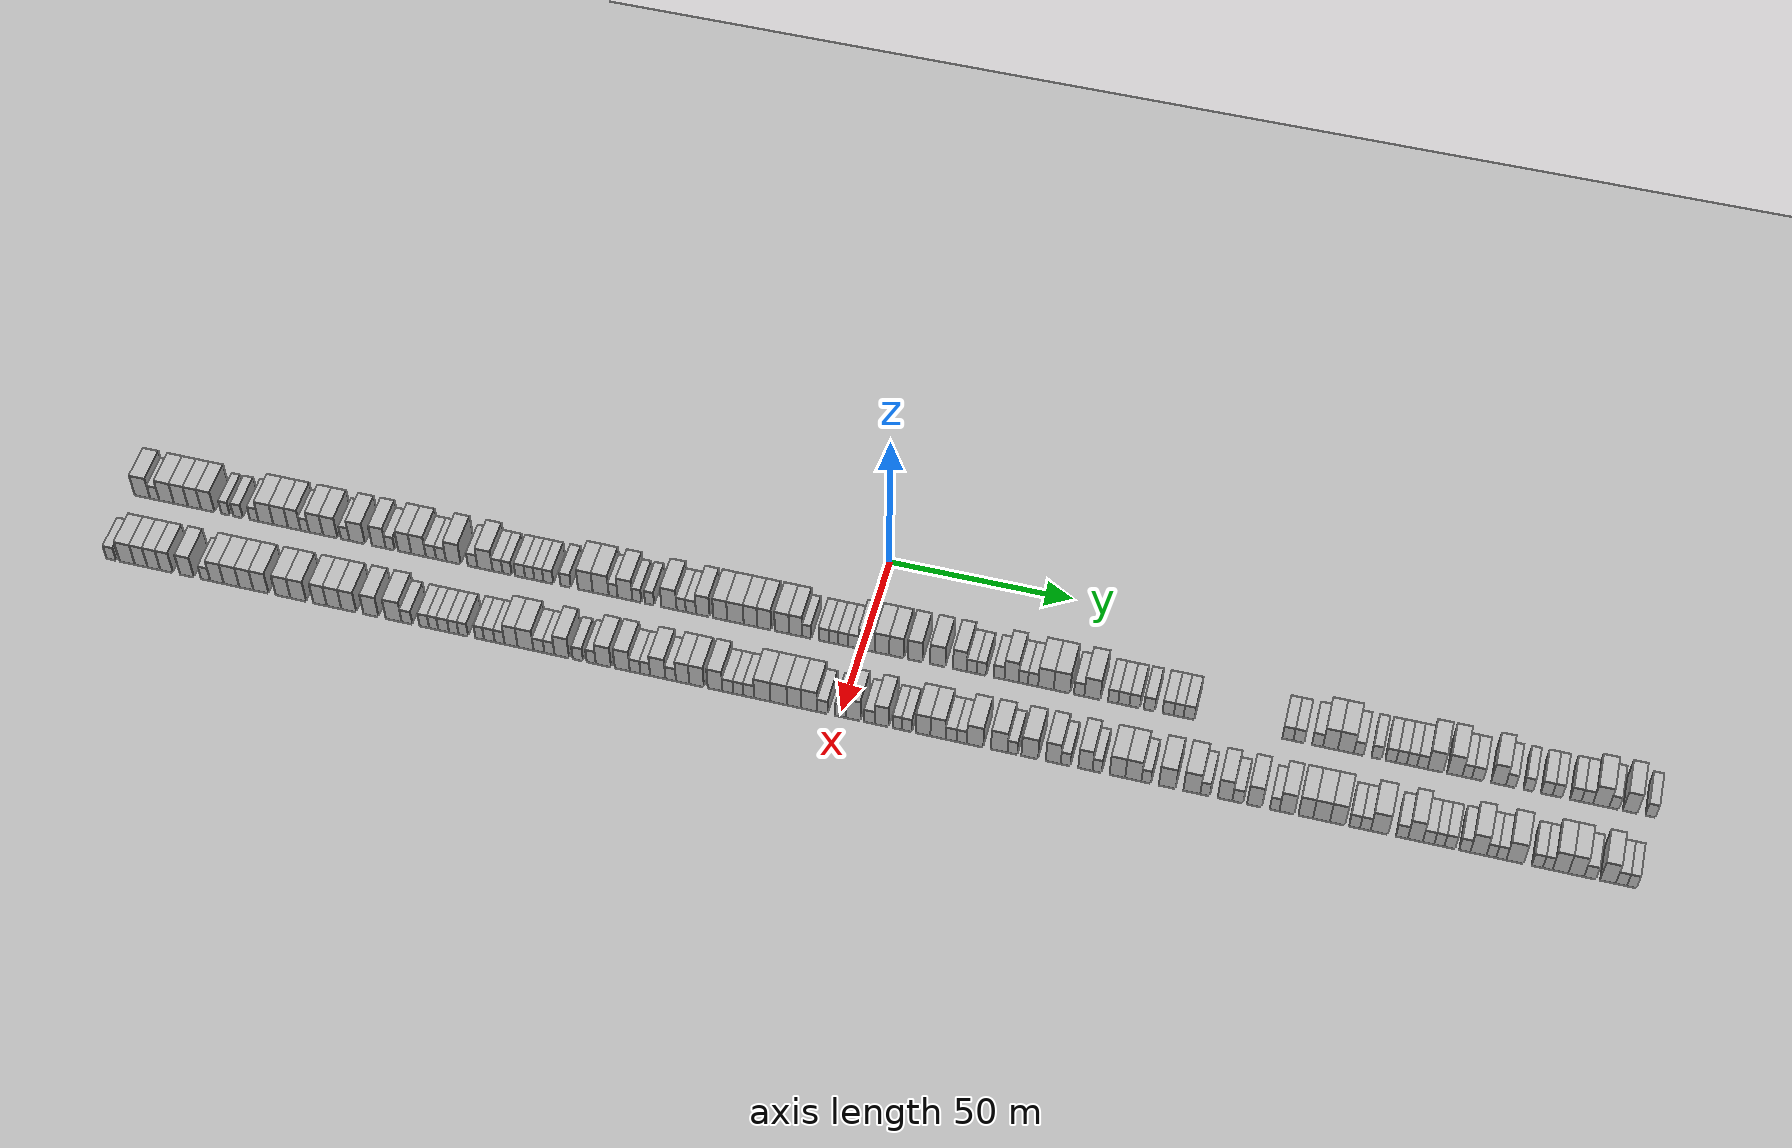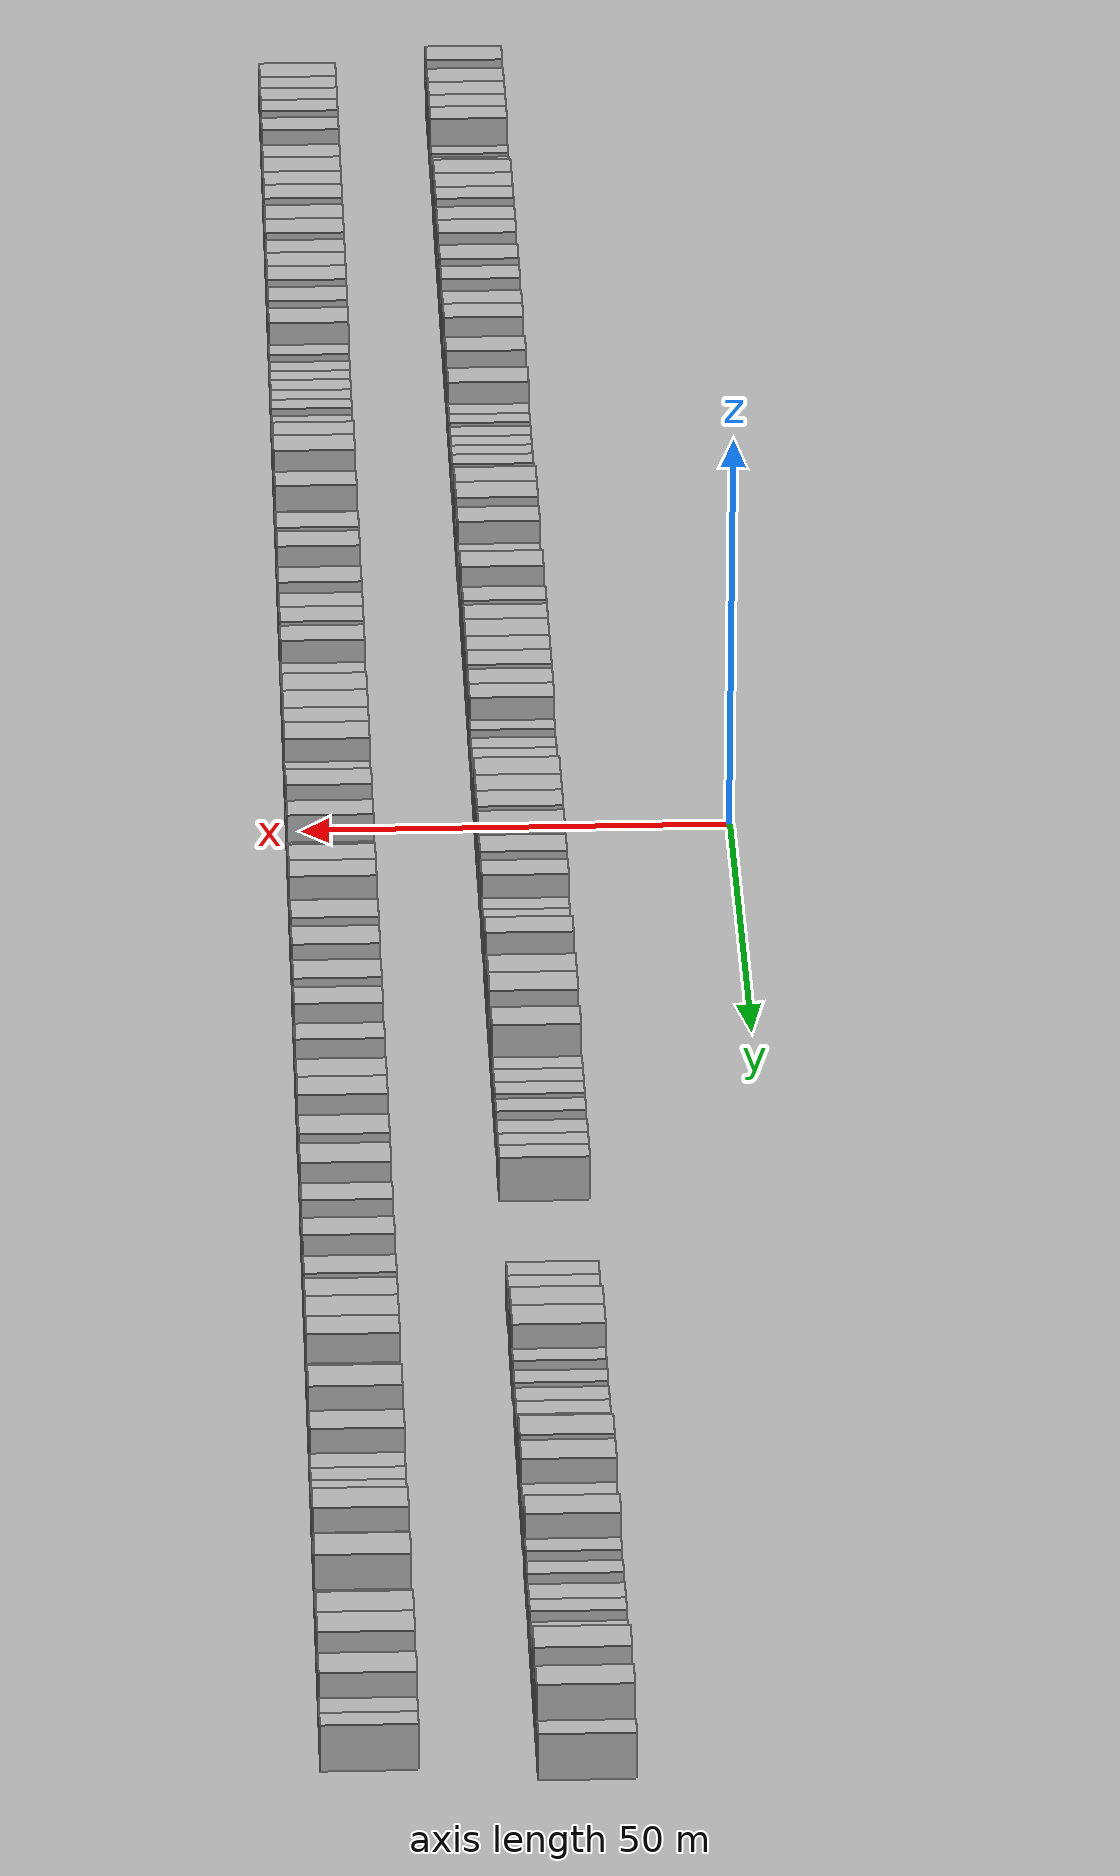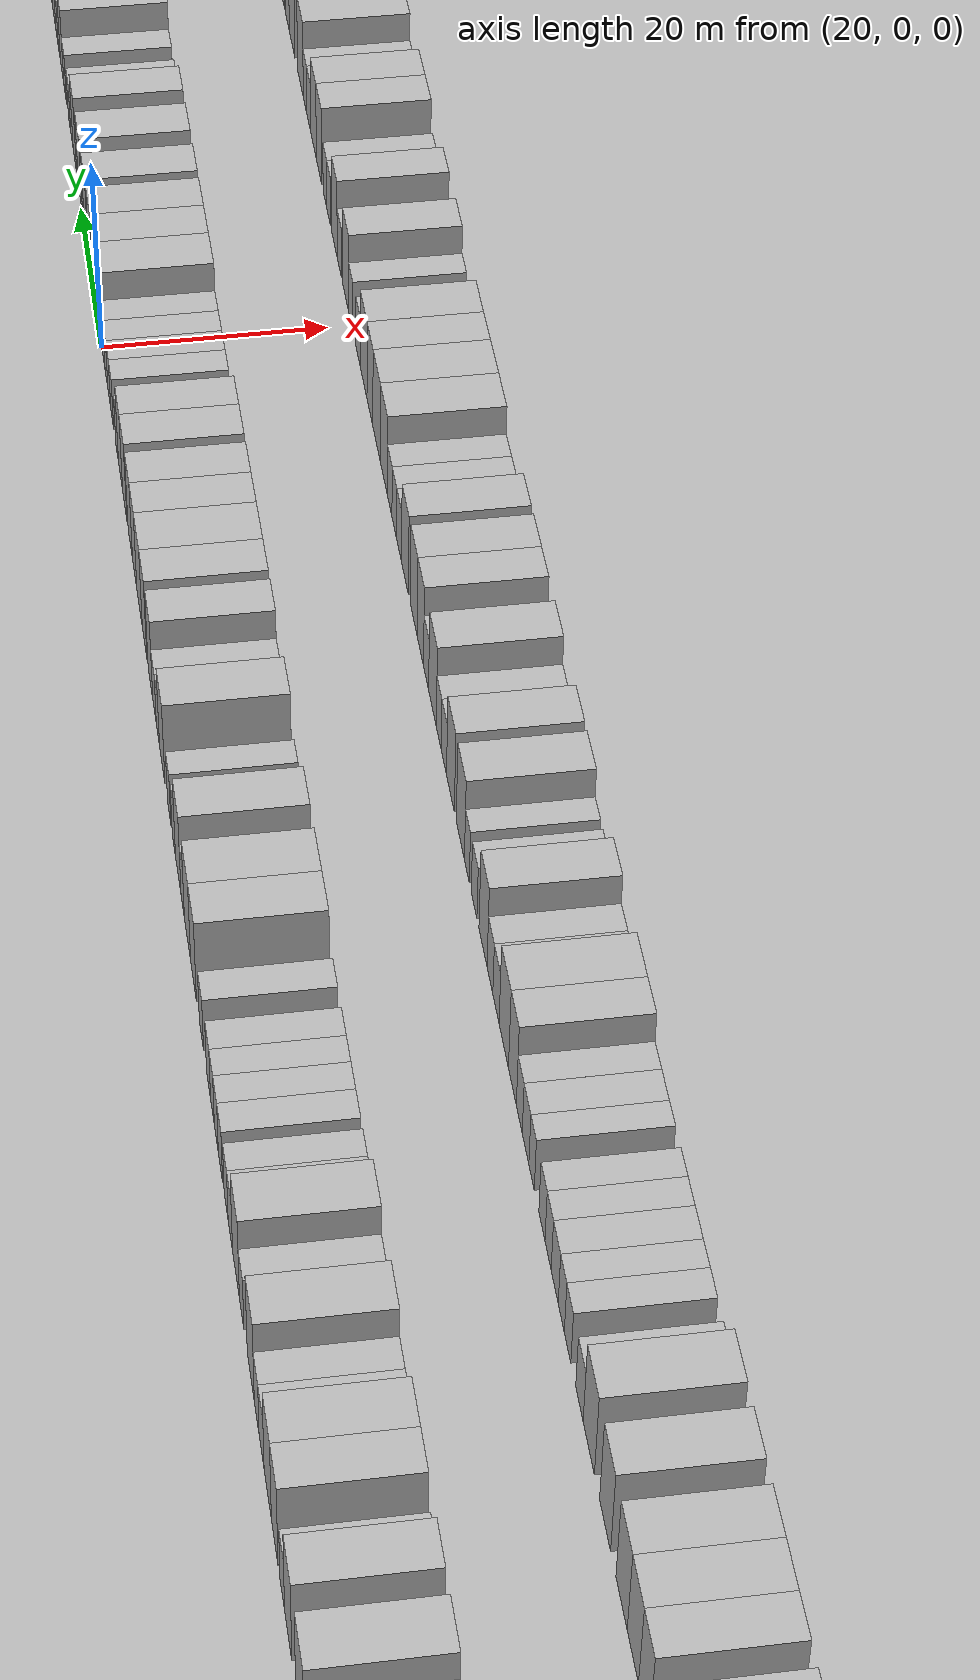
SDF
<?xml version="1.0" encoding="utf-8"?>

<sdf version="1.6">

   <world name="default">

      <gui fullscreen="0">

         <camera name="user_camera">

            <pose>-15 0 4.57585 0 0 0</pose>

            <view_controller>orbit</view_controller>

         </camera>

      </gui>

      <scene>

         <sky>

           <clouds>

             <speed>12</speed>

           </clouds>

         </sky>

         <ambient>0.4 0.4 0.4 1</ambient>

         <background>0.7 0.7 0.7 1</background>

         <shadows>1</shadows>

      </scene>

      <gravity>0 0 -9.8066</gravity>

      <magnetic_field>6e-06 2.3e-05 -4.2e-05</magnetic_field>

      <physics default="0" name="default_physics" type="ode">

         <ode>

            <solver>

               <type>quick</type>

               <iters>10</iters>

               <sor>1.0</sor>

               <use_dynamic_moi_rescaling>0</use_dynamic_moi_rescaling>

            </solver>

            <constraints>

               <cfm>0</cfm>

               <erp>0.2</erp>

               <contact_max_correcting_vel>100</contact_max_correcting_vel>

               <contact_surface_layer>0.001</contact_surface_layer>

            </constraints>

         </ode>

         <max_step_size>0.004</max_step_size>

         <real_time_factor>1</real_time_factor>

         <real_time_update_rate>250</real_time_update_rate>

      </physics>

      <light name="sun" type="directional">

         <cast_shadows>1</cast_shadows>

         <pose>0 0 10 0 0 0</pose>

         <diffuse>0.8 0.8 0.8 1</diffuse>

         <specular>0.2 0.2 0.2 1</specular>

         <attenuation>

            <range>1000</range>

            <constant>0.9</constant>

            <linear>0.01</linear>

            <quadratic>0.001</quadratic>

         </attenuation>

         <direction>-0.5 0.1 -0.9</direction>

      </light>

      <include>

         <name>ground_plane_1</name>

         <uri>model://HANNAS_ground_plane</uri>

         <pose>0 0 0  0 0 0</pose>

      </include>

      <include>

         <name>ground_plane_2</name>

         <uri>model://HANNAS_ground_plane</uri>

         <pose>100 0 0  0 0 0</pose>

      </include>

      <model name="building_1">

         <static>1</static>

         <pose frame="">25.0000 -201.7638 0 0.000000 0.000000 0.000000</pose>

         <link name="link">

            <pose frame="">0 0 4.50 0 0 0</pose>

            <collision name="collision">

               <geometry>

                  <box>

                     <size>10.0000 4.4724 9.0000</size>

                  </box>

               </geometry>

               <max_contacts>10</max_contacts>

               <surface>

                  <contact>

                     <ode/>

                  </contact>

                  <bounce/>

                  <friction>

                     <torsional>

                        <ode/>

                     </torsional>

                     <ode/>

                  </friction>

               </surface>

            </collision>

            <visual name="visual">

               <cast_shadows>0</cast_shadows>

               <geometry>

                  <box>

                     <size>10.0000 4.4724 9.0000</size>

                  </box>

               </geometry>

               <material>

                  <script>

                     <uri>model://HANNAS_wall/materials/scripts</uri>

                     <uri>model://HANNAS_wall/materials/textures</uri>

                     <name>vrc/HANNAS_wall</name>

                  </script>

               </material>

            </visual>

            <self_collide>0</self_collide>

            <enable_wind>0</enable_wind>

            <kinematic>0</kinematic>

         </link>

      </model>

      <model name="building_2">

         <static>1</static>

         <pose frame="">25.0000 -198.2044 0 0.000000 0.000000 0.000000</pose>

         <link name="link">

            <pose frame="">0 0 3.00 0 0 0</pose>

            <collision name="collision">

               <geometry>

                  <box>

                     <size>10.0000 2.6465 6.0000</size>

                  </box>

               </geometry>

               <max_contacts>10</max_contacts>

               <surface>

                  <contact>

                     <ode/>

                  </contact>

                  <bounce/>

                  <friction>

                     <torsional>

                        <ode/>

                     </torsional>

                     <ode/>

                  </friction>

               </surface>

            </collision>

            <visual name="visual">

               <cast_shadows>0</cast_shadows>

               <geometry>

                  <box>

                     <size>10.0000 2.6465 6.0000</size>

                  </box>

               </geometry>

               <material>

                  <script>

                     <uri>model://HANNAS_wall/materials/scripts</uri>

                     <uri>model://HANNAS_wall/materials/textures</uri>

                     <name>vrc/HANNAS_wall</name>

                  </script>

               </material>

            </visual>

            <self_collide>0</self_collide>

            <enable_wind>0</enable_wind>

            <kinematic>0</kinematic>

         </link>

      </model>

      <model name="building_3">

         <static>1</static>

         <pose frame="">25.0000 -194.7488 0 0.000000 0.000000 0.000000</pose>

         <link name="link">

            <pose frame="">0 0 4.50 0 0 0</pose>

            <collision name="collision">

               <geometry>

                  <box>

                     <size>10.0000 4.2647 9.0000</size>

                  </box>

               </geometry>

               <max_contacts>10</max_contacts>

               <surface>

                  <contact>

                     <ode/>

                  </contact>

                  <bounce/>

                  <friction>

                     <torsional>

                        <ode/>

                     </torsional>

                     <ode/>

                  </friction>

               </surface>

            </collision>

            <visual name="visual">

               <cast_shadows>0</cast_shadows>

               <geometry>

                  <box>

                     <size>10.0000 4.2647 9.0000</size>

                  </box>

               </geometry>

               <material>

                  <script>

                     <uri>model://HANNAS_wall/materials/scripts</uri>

                     <uri>model://HANNAS_wall/materials/textures</uri>

                     <name>vrc/HANNAS_wall</name>

                  </script>

               </material>

            </visual>

            <self_collide>0</self_collide>

            <enable_wind>0</enable_wind>

            <kinematic>0</kinematic>

         </link>

      </model>

      <model name="building_4">

         <static>1</static>

         <pose frame="">25.0000 -190.5852 0 0.000000 0.000000 0.000000</pose>

         <link name="link">

            <pose frame="">0 0 4.50 0 0 0</pose>

            <collision name="collision">

               <geometry>

                  <box>

                     <size>10.0000 4.0623 9.0000</size>

                  </box>

               </geometry>

               <max_contacts>10</max_contacts>

               <surface>

                  <contact>

                     <ode/>

                  </contact>

                  <bounce/>

                  <friction>

                     <torsional>

                        <ode/>

                     </torsional>

                     <ode/>

                  </friction>

               </surface>

            </collision>

            <visual name="visual">

               <cast_shadows>0</cast_shadows>

               <geometry>

                  <box>

                     <size>10.0000 4.0623 9.0000</size>

                  </box>

               </geometry>

               <material>

                  <script>

                     <uri>model://HANNAS_wall/materials/scripts</uri>

                     <uri>model://HANNAS_wall/materials/textures</uri>

                     <name>vrc/HANNAS_wall</name>

                  </script>

               </material>

            </visual>

            <self_collide>0</self_collide>

            <enable_wind>0</enable_wind>

            <kinematic>0</kinematic>

         </link>

      </model>

      <model name="building_5">

         <static>1</static>

         <pose frame="">25.0000 -186.6543 0 0.000000 0.000000 0.000000</pose>

         <link name="link">

            <pose frame="">0 0 4.50 0 0 0</pose>

            <collision name="collision">

               <geometry>

                  <box>

                     <size>10.0000 3.7996 9.0000</size>

                  </box>

               </geometry>

               <max_contacts>10</max_contacts>

               <surface>

                  <contact>

                     <ode/>

                  </contact>

                  <bounce/>

                  <friction>

                     <torsional>

                        <ode/>

                     </torsional>

                     <ode/>

                  </friction>

               </surface>

            </collision>

            <visual name="visual">

               <cast_shadows>0</cast_shadows>

               <geometry>

                  <box>

                     <size>10.0000 3.7996 9.0000</size>

                  </box>

               </geometry>

               <material>

                  <script>

                     <uri>model://HANNAS_wall/materials/scripts</uri>

                     <uri>model://HANNAS_wall/materials/textures</uri>

                     <name>vrc/HANNAS_wall</name>

                  </script>

               </material>

            </visual>

            <self_collide>0</self_collide>

            <enable_wind>0</enable_wind>

            <kinematic>0</kinematic>

         </link>

      </model>

      <model name="building_6">

         <static>1</static>

         <pose frame="">25.0000 -182.8145 0 0.000000 0.000000 0.000000</pose>

         <link name="link">

            <pose frame="">0 0 4.50 0 0 0</pose>

            <collision name="collision">

               <geometry>

                  <box>

                     <size>10.0000 3.8800 9.0000</size>

                  </box>

               </geometry>

               <max_contacts>10</max_contacts>

               <surface>

                  <contact>

                     <ode/>

                  </contact>

                  <bounce/>

                  <friction>

                     <torsional>

                        <ode/>

                     </torsional>

                     <ode/>

                  </friction>

               </surface>

            </collision>

            <visual name="visual">

               <cast_shadows>0</cast_shadows>

               <geometry>

                  <box>

                     <size>10.0000 3.8800 9.0000</size>

                  </box>

               </geometry>

               <material>

                  <script>

                     <uri>model://HANNAS_wall/materials/scripts</uri>

                     <uri>model://HANNAS_wall/materials/textures</uri>

                     <name>vrc/HANNAS_wall</name>

                  </script>

               </material>

            </visual>

            <self_collide>0</self_collide>

            <enable_wind>0</enable_wind>

            <kinematic>0</kinematic>

         </link>

      </model>

      <model name="building_7">

         <static>1</static>

         <pose frame="">25.0000 -177.6527 0 0.000000 0.000000 0.000000</pose>

         <link name="link">

            <pose frame="">0 0 3.00 0 0 0</pose>

            <collision name="collision">

               <geometry>

                  <box>

                     <size>10.0000 2.4434 6.0000</size>

                  </box>

               </geometry>

               <max_contacts>10</max_contacts>

               <surface>

                  <contact>

                     <ode/>

                  </contact>

                  <bounce/>

                  <friction>

                     <torsional>

                        <ode/>

                     </torsional>

                     <ode/>

                  </friction>

               </surface>

            </collision>

            <visual name="visual">

               <cast_shadows>0</cast_shadows>

               <geometry>

                  <box>

                     <size>10.0000 2.4434 6.0000</size>

                  </box>

               </geometry>

               <material>

                  <script>

                     <uri>model://HANNAS_wall/materials/scripts</uri>

                     <uri>model://HANNAS_wall/materials/textures</uri>

                     <name>vrc/HANNAS_wall</name>

                  </script>

               </material>

            </visual>

            <self_collide>0</self_collide>

            <enable_wind>0</enable_wind>

            <kinematic>0</kinematic>

         </link>

      </model>

      <model name="building_8">

         <static>1</static>

         <pose frame="">25.0000 -174.0663 0 0.000000 0.000000 0.000000</pose>

         <link name="link">

            <pose frame="">0 0 3.00 0 0 0</pose>

            <collision name="collision">

               <geometry>

                  <box>

                     <size>10.0000 2.7294 6.0000</size>

                  </box>

               </geometry>

               <max_contacts>10</max_contacts>

               <surface>

                  <contact>

                     <ode/>

                  </contact>

                  <bounce/>

                  <friction>

                     <torsional>

                        <ode/>

                     </torsional>

                     <ode/>

                  </friction>

               </surface>

            </collision>

            <visual name="visual">

               <cast_shadows>0</cast_shadows>

               <geometry>

                  <box>

                     <size>10.0000 2.7294 6.0000</size>

                  </box>

               </geometry>

               <material>

                  <script>

                     <uri>model://HANNAS_wall/materials/scripts</uri>

                     <uri>model://HANNAS_wall/materials/textures</uri>

                     <name>vrc/HANNAS_wall</name>

                  </script>

               </material>

            </visual>

            <self_collide>0</self_collide>

            <enable_wind>0</enable_wind>

            <kinematic>0</kinematic>

         </link>

      </model>

      <model name="building_9">

         <static>1</static>

         <pose frame="">25.0000 -169.4440 0 0.000000 0.000000 0.000000</pose>

         <link name="link">

            <pose frame="">0 0 3.00 0 0 0</pose>

            <collision name="collision">

               <geometry>

                  <box>

                     <size>10.0000 2.5153 6.0000</size>

                  </box>

               </geometry>

               <max_contacts>10</max_contacts>

               <surface>

                  <contact>

                     <ode/>

                  </contact>

                  <bounce/>

                  <friction>

                     <torsional>

                        <ode/>

                     </torsional>

                     <ode/>

                  </friction>

               </surface>

            </collision>

            <visual name="visual">

               <cast_shadows>0</cast_shadows>

               <geometry>

                  <box>

                     <size>10.0000 2.5153 6.0000</size>

                  </box>

               </geometry>

               <material>

                  <script>

                     <uri>model://HANNAS_wall/materials/scripts</uri>

                     <uri>model://HANNAS_wall/materials/textures</uri>

                     <name>vrc/HANNAS_wall</name>

                  </script>

               </material>

            </visual>

            <self_collide>0</self_collide>

            <enable_wind>0</enable_wind>

            <kinematic>0</kinematic>

         </link>

      </model>

      <model name="building_10">

         <static>1</static>

         <pose frame="">25.0000 -166.0645 0 0.000000 0.000000 0.000000</pose>

         <link name="link">

            <pose frame="">0 0 4.50 0 0 0</pose>

            <collision name="collision">

               <geometry>

                  <box>

                     <size>10.0000 4.2437 9.0000</size>

                  </box>

               </geometry>

               <max_contacts>10</max_contacts>

               <surface>

                  <contact>

                     <ode/>

                  </contact>

                  <bounce/>

                  <friction>

                     <torsional>

                        <ode/>

                     </torsional>

                     <ode/>

                  </friction>

               </surface>

            </collision>

            <visual name="visual">

               <cast_shadows>0</cast_shadows>

               <geometry>

                  <box>

                     <size>10.0000 4.2437 9.0000</size>

                  </box>

               </geometry>

               <material>

                  <script>

                     <uri>model://HANNAS_wall/materials/scripts</uri>

                     <uri>model://HANNAS_wall/materials/textures</uri>

                     <name>vrc/HANNAS_wall</name>

                  </script>

               </material>

            </visual>

            <self_collide>0</self_collide>

            <enable_wind>0</enable_wind>

            <kinematic>0</kinematic>

         </link>

      </model>

      <model name="building_11">

         <static>1</static>

         <pose frame="">25.0000 -161.8498 0 0.000000 0.000000 0.000000</pose>

         <link name="link">

            <pose frame="">0 0 4.50 0 0 0</pose>

            <collision name="collision">

               <geometry>

                  <box>

                     <size>10.0000 4.1857 9.0000</size>

                  </box>

               </geometry>

               <max_contacts>10</max_contacts>

               <surface>

                  <contact>

                     <ode/>

                  </contact>

                  <bounce/>

                  <friction>

                     <torsional>

                        <ode/>

                     </torsional>

                     <ode/>

                  </friction>

               </surface>

            </collision>

            <visual name="visual">

               <cast_shadows>0</cast_shadows>

               <geometry>

                  <box>

                     <size>10.0000 4.1857 9.0000</size>

                  </box>

               </geometry>

               <material>

                  <script>

                     <uri>model://HANNAS_wall/materials/scripts</uri>

                     <uri>model://HANNAS_wall/materials/textures</uri>

                     <name>vrc/HANNAS_wall</name>

                  </script>

               </material>

            </visual>

            <self_collide>0</self_collide>

            <enable_wind>0</enable_wind>

            <kinematic>0</kinematic>

         </link>

      </model>

      <model name="building_12">

         <static>1</static>

         <pose frame="">25.0000 -157.9383 0 0.000000 0.000000 0.000000</pose>

         <link name="link">

            <pose frame="">0 0 4.50 0 0 0</pose>

            <collision name="collision">

               <geometry>

                  <box>

                     <size>10.0000 3.6374 9.0000</size>

                  </box>

               </geometry>

               <max_contacts>10</max_contacts>

               <surface>

                  <contact>

                     <ode/>

                  </contact>

                  <bounce/>

                  <friction>

                     <torsional>

                        <ode/>

                     </torsional>

                     <ode/>

                  </friction>

               </surface>

            </collision>

            <visual name="visual">

               <cast_shadows>0</cast_shadows>

               <geometry>

                  <box>

                     <size>10.0000 3.6374 9.0000</size>

                  </box>

               </geometry>

               <material>

                  <script>

                     <uri>model://HANNAS_wall/materials/scripts</uri>

                     <uri>model://HANNAS_wall/materials/textures</uri>

                     <name>vrc/HANNAS_wall</name>

                  </script>

               </material>

            </visual>

            <self_collide>0</self_collide>

            <enable_wind>0</enable_wind>

            <kinematic>0</kinematic>

         </link>

      </model>

      <model name="building_13">

         <static>1</static>

         <pose frame="">25.0000 -154.9052 0 0.000000 0.000000 0.000000</pose>

         <link name="link">

            <pose frame="">0 0 3.00 0 0 0</pose>

            <collision name="collision">

               <geometry>

                  <box>

                     <size>10.0000 2.4287 6.0000</size>

                  </box>

               </geometry>

               <max_contacts>10</max_contacts>

               <surface>

                  <contact>

                     <ode/>

                  </contact>

                  <bounce/>

                  <friction>

                     <torsional>

                        <ode/>

                     </torsional>

                     <ode/>

                  </friction>

               </surface>

            </collision>

            <visual name="visual">

               <cast_shadows>0</cast_shadows>

               <geometry>

                  <box>

                     <size>10.0000 2.4287 6.0000</size>

                  </box>

               </geometry>

               <material>

                  <script>

                     <uri>model://HANNAS_wall/materials/scripts</uri>

                     <uri>model://HANNAS_wall/materials/textures</uri>

                     <name>vrc/HANNAS_wall</name>

                  </script>

               </material>

            </visual>

            <self_collide>0</self_collide>

            <enable_wind>0</enable_wind>

            <kinematic>0</kinematic>

         </link>

      </model>

      <model name="building_14">

         <static>1</static>

         <pose frame="">25.0000 -151.7200 0 0.000000 0.000000 0.000000</pose>

         <link name="link">

            <pose frame="">0 0 4.50 0 0 0</pose>

            <collision name="collision">

               <geometry>

                  <box>

                     <size>10.0000 3.9417 9.0000</size>

                  </box>

               </geometry>

               <max_contacts>10</max_contacts>

               <surface>

                  <contact>

                     <ode/>

                  </contact>

                  <bounce/>

                  <friction>

                     <torsional>

                        <ode/>

                     </torsional>

                     <ode/>

                  </friction>

               </surface>

            </collision>

            <visual name="visual">

               <cast_shadows>0</cast_shadows>

               <geometry>

                  <box>

                     <size>10.0000 3.9417 9.0000</size>

                  </box>

               </geometry>

               <material>

                  <script>

                     <uri>model://HANNAS_wall/materials/scripts</uri>

                     <uri>model://HANNAS_wall/materials/textures</uri>

                     <name>vrc/HANNAS_wall</name>

                  </script>

               </material>

            </visual>

            <self_collide>0</self_collide>

            <enable_wind>0</enable_wind>

            <kinematic>0</kinematic>

         </link>

      </model>

      <model name="building_15">

         <static>1</static>

         <pose frame="">25.0000 -147.6774 0 0.000000 0.000000 0.000000</pose>

         <link name="link">

            <pose frame="">0 0 4.50 0 0 0</pose>

            <collision name="collision">

               <geometry>

                  <box>

                     <size>10.0000 4.1435 9.0000</size>

                  </box>

               </geometry>

               <max_contacts>10</max_contacts>

               <surface>

                  <contact>

                     <ode/>

                  </contact>

                  <bounce/>

                  <friction>

                     <torsional>

                        <ode/>

                     </torsional>

                     <ode/>

                  </friction>

               </surface>

            </collision>

            <visual name="visual">

               <cast_shadows>0</cast_shadows>

               <geometry>

                  <box>

                     <size>10.0000 4.1435 9.0000</size>

                  </box>

               </geometry>

               <material>

                  <script>

                     <uri>model://HANNAS_wall/materials/scripts</uri>

                     <uri>model://HANNAS_wall/materials/textures</uri>

                     <name>vrc/HANNAS_wall</name>

                  </script>

               </material>

            </visual>

            <self_collide>0</self_collide>

            <enable_wind>0</enable_wind>

            <kinematic>0</kinematic>

         </link>

      </model>

      <model name="building_16">

         <static>1</static>

         <pose frame="">25.0000 -143.3900 0 0.000000 0.000000 0.000000</pose>

         <link name="link">

            <pose frame="">0 0 3.00 0 0 0</pose>

            <collision name="collision">

               <geometry>

                  <box>

                     <size>10.0000 2.4312 6.0000</size>

                  </box>

               </geometry>

               <max_contacts>10</max_contacts>

               <surface>

                  <contact>

                     <ode/>

                  </contact>

                  <bounce/>

                  <friction>

                     <torsional>

                        <ode/>

                     </torsional>

                     <ode/>

                  </friction>

               </surface>

            </collision>

            <visual name="visual">

               <cast_shadows>0</cast_shadows>

               <geometry>

                  <box>

                     <size>10.0000 2.4312 6.0000</size>

                  </box>

               </geometry>

               <material>

                  <script>

                     <uri>model://HANNAS_wall/materials/scripts</uri>

                     <uri>model://HANNAS_wall/materials/textures</uri>

                     <name>vrc/HANNAS_wall</name>

                  </script>

               </material>

            </visual>

            <self_collide>0</self_collide>

            <enable_wind>0</enable_wind>

            <kinematic>0</kinematic>

         </link>

      </model>

      <model name="building_17">

         <static>1</static>

         <pose frame="">25.0000 -139.9825 0 0.000000 0.000000 0.000000</pose>

         <link name="link">

            <pose frame="">0 0 4.50 0 0 0</pose>

            <collision name="collision">

               <geometry>

                  <box>

                     <size>10.0000 4.3837 9.0000</size>

                  </box>

               </geometry>

               <max_contacts>10</max_contacts>

               <surface>

                  <contact>

                     <ode/>

                  </contact>

                  <bounce/>

                  <friction>

                     <torsional>

                        <ode/>

                     </torsional>

                     <ode/>

                  </friction>

               </surface>

            </collision>

            <visual name="visual">

               <cast_shadows>0</cast_shadows>

               <geometry>

                  <box>

                     <size>10.0000 4.3837 9.0000</size>

                  </box>

               </geometry>

               <material>

                  <script>

                     <uri>model://HANNAS_wall/materials/scripts</uri>

                     <uri>model://HANNAS_wall/materials/textures</uri>

                     <name>vrc/HANNAS_wall</name>

                  </script>

               </material>

            </visual>

            <self_collide>0</self_collide>

            <enable_wind>0</enable_wind>

            <kinematic>0</kinematic>

         </link>

      </model>

      <model name="building_18">

         <static>1</static>

         <pose frame="">25.0000 -133.8397 0 0.000000 0.000000 0.000000</pose>

         <link name="link">

            <pose frame="">0 0 4.50 0 0 0</pose>

            <collision name="collision">

               <geometry>

                  <box>

                     <size>10.0000 3.9020 9.0000</size>

                  </box>

               </geometry>

               <max_contacts>10</max_contacts>

               <surface>

                  <contact>

                     <ode/>

                  </contact>

                  <bounce/>

                  <friction>

                     <torsional>

                        <ode/>

                     </torsional>

                     <ode/>

                  </friction>

               </surface>

            </collision>

            <visual name="visual">

               <cast_shadows>0</cast_shadows>

               <geometry>

                  <box>

                     <size>10.0000 3.9020 9.0000</size>

                  </box>

               </geometry>

               <material>

                  <script>

                     <uri>model://HANNAS_wall/materials/scripts</uri>

                     <uri>model://HANNAS_wall/materials/textures</uri>

                     <name>vrc/HANNAS_wall</name>

                  </script>

               </material>

            </visual>

            <self_collide>0</self_collide>

            <enable_wind>0</enable_wind>

            <kinematic>0</kinematic>

         </link>

      </model>

      <model name="building_19">

         <static>1</static>

         <pose frame="">25.0000 -130.6132 0 0.000000 0.000000 0.000000</pose>

         <link name="link">

            <pose frame="">0 0 3.00 0 0 0</pose>

            <collision name="collision">

               <geometry>

                  <box>

                     <size>10.0000 2.5512 6.0000</size>

                  </box>

               </geometry>

               <max_contacts>10</max_contacts>

               <surface>

                  <contact>

                     <ode/>

                  </contact>

                  <bounce/>

                  <friction>

                     <torsional>

                        <ode/>

                     </torsional>

                     <ode/>

                  </friction>

               </surface>

            </collision>

            <visual name="visual">

               <cast_shadows>0</cast_shadows>

               <geometry>

                  <box>

                     <size>10.0000 2.5512 6.0000</size>

                  </box>

               </geometry>

               <material>

                  <script>

                     <uri>model://HANNAS_wall/materials/scripts</uri>

                     <uri>model://HANNAS_wall/materials/textures</uri>

                     <name>vrc/HANNAS_wall</name>

                  </script>

               </material>

            </visual>

            <self_collide>0</self_collide>

            <enable_wind>0</enable_wind>

            <kinematic>0</kinematic>

         </link>

      </model>

      <model name="building_20">

         <static>1</static>

         <pose frame="">25.0000 -126.4945 0 0.000000 0.000000 0.000000</pose>

         <link name="link">

            <pose frame="">0 0 4.50 0 0 0</pose>

            <collision name="collision">

               <geometry>

                  <box>

                     <size>10.0000 3.6862 9.0000</size>

                  </box>

               </geometry>

               <max_contacts>10</max_contacts>

               <surface>

                  <contact>

                     <ode/>

                  </contact>

                  <bounce/>

                  <friction>

                     <torsional>

                        <ode/>

                     </torsional>

                     <ode/>

                  </friction>

               </surface>

            </collision>

            <visual name="visual">

               <cast_shadows>0</cast_shadows>

               <geometry>

                  <box>

                     <size>10.0000 3.6862 9.0000</size>

                  </box>

               </geometry>

               <material>

                  <script>

                     <uri>model://HANNAS_wall/materials/scripts</uri>

                     <uri>model://HANNAS_wall/materials/textures</uri>

                     <name>vrc/HANNAS_wall</name>

                  </script>

               </material>

            </visual>

            <self_collide>0</self_collide>

            <enable_wind>0</enable_wind>

            <kinematic>0</kinematic>

         </link>

      </model>

      <model name="building_21">

         <static>1</static>

         <pose frame="">25.0000 -122.5954 0 0.000000 0.000000 0.000000</pose>

         <link name="link">

            <pose frame="">0 0 4.50 0 0 0</pose>

            <collision name="collision">

               <geometry>

                  <box>

                     <size>10.0000 4.1119 9.0000</size>

                  </box>

               </geometry>

               <max_contacts>10</max_contacts>

               <surface>

                  <contact>

                     <ode/>

                  </contact>

                  <bounce/>

                  <friction>

                     <torsional>

                        <ode/>

                     </torsional>

                     <ode/>

                  </friction>

               </surface>

            </collision>

            <visual name="visual">

               <cast_shadows>0</cast_shadows>

               <geometry>

                  <box>

                     <size>10.0000 4.1119 9.0000</size>

                  </box>

               </geometry>

               <material>

                  <script>

                     <uri>model://HANNAS_wall/materials/scripts</uri>

                     <uri>model://HANNAS_wall/materials/textures</uri>

                     <name>vrc/HANNAS_wall</name>

                  </script>

               </material>

            </visual>

            <self_collide>0</self_collide>

            <enable_wind>0</enable_wind>

            <kinematic>0</kinematic>

         </link>

      </model>

      <model name="building_22">

         <static>1</static>

         <pose frame="">25.0000 -119.0821 0 0.000000 0.000000 0.000000</pose>

         <link name="link">

            <pose frame="">0 0 3.00 0 0 0</pose>

            <collision name="collision">

               <geometry>

                  <box>

                     <size>10.0000 2.9146 6.0000</size>

                  </box>

               </geometry>

               <max_contacts>10</max_contacts>

               <surface>

                  <contact>

                     <ode/>

                  </contact>

                  <bounce/>

                  <friction>

                     <torsional>

                        <ode/>

                     </torsional>

                     <ode/>

                  </friction>

               </surface>

            </collision>

            <visual name="visual">

               <cast_shadows>0</cast_shadows>

               <geometry>

                  <box>

                     <size>10.0000 2.9146 6.0000</size>

                  </box>

               </geometry>

               <material>

                  <script>

                     <uri>model://HANNAS_wall/materials/scripts</uri>

                     <uri>model://HANNAS_wall/materials/textures</uri>

                     <name>vrc/HANNAS_wall</name>

                  </script>

               </material>

            </visual>

            <self_collide>0</self_collide>

            <enable_wind>0</enable_wind>

            <kinematic>0</kinematic>

         </link>

      </model>

      <model name="building_23">

         <static>1</static>

         <pose frame="">25.0000 -116.2512 0 0.000000 0.000000 0.000000</pose>

         <link name="link">

            <pose frame="">0 0 3.00 0 0 0</pose>

            <collision name="collision">

               <geometry>

                  <box>

                     <size>10.0000 2.7474 6.0000</size>

                  </box>

               </geometry>

               <max_contacts>10</max_contacts>

               <surface>

                  <contact>

                     <ode/>

                  </contact>

                  <bounce/>

                  <friction>

                     <torsional>

                        <ode/>

                     </torsional>

                     <ode/>

                  </friction>

               </surface>

            </collision>

            <visual name="visual">

               <cast_shadows>0</cast_shadows>

               <geometry>

                  <box>

                     <size>10.0000 2.7474 6.0000</size>

                  </box>

               </geometry>

               <material>

                  <script>

                     <uri>model://HANNAS_wall/materials/scripts</uri>

                     <uri>model://HANNAS_wall/materials/textures</uri>

                     <name>vrc/HANNAS_wall</name>

                  </script>

               </material>

            </visual>

            <self_collide>0</self_collide>

            <enable_wind>0</enable_wind>

            <kinematic>0</kinematic>

         </link>

      </model>

      <model name="building_24">

         <static>1</static>

         <pose frame="">25.0000 -112.7890 0 0.000000 0.000000 0.000000</pose>

         <link name="link">

            <pose frame="">0 0 4.50 0 0 0</pose>

            <collision name="collision">

               <geometry>

                  <box>

                     <size>10.0000 4.1770 9.0000</size>

                  </box>

               </geometry>

               <max_contacts>10</max_contacts>

               <surface>

                  <contact>

                     <ode/>

                  </contact>

                  <bounce/>

                  <friction>

                     <torsional>

                        <ode/>

                     </torsional>

                     <ode/>

                  </friction>

               </surface>

            </collision>

            <visual name="visual">

               <cast_shadows>0</cast_shadows>

               <geometry>

                  <box>

                     <size>10.0000 4.1770 9.0000</size>

                  </box>

               </geometry>

               <material>

                  <script>

                     <uri>model://HANNAS_wall/materials/scripts</uri>

                     <uri>model://HANNAS_wall/materials/textures</uri>

                     <name>vrc/HANNAS_wall</name>

                  </script>

               </material>

            </visual>

            <self_collide>0</self_collide>

            <enable_wind>0</enable_wind>

            <kinematic>0</kinematic>

         </link>

      </model>

      <model name="building_25">

         <static>1</static>

         <pose frame="">25.0000 -107.3323 0 0.000000 0.000000 0.000000</pose>

         <link name="link">

            <pose frame="">0 0 3.00 0 0 0</pose>

            <collision name="collision">

               <geometry>

                  <box>

                     <size>10.0000 2.7364 6.0000</size>

                  </box>

               </geometry>

               <max_contacts>10</max_contacts>

               <surface>

                  <contact>

                     <ode/>

                  </contact>

                  <bounce/>

                  <friction>

                     <torsional>

                        <ode/>

                     </torsional>

                     <ode/>

                  </friction>

               </surface>

            </collision>

            <visual name="visual">

               <cast_shadows>0</cast_shadows>

               <geometry>

                  <box>

                     <size>10.0000 2.7364 6.0000</size>

                  </box>

               </geometry>

               <material>

                  <script>

                     <uri>model://HANNAS_wall/materials/scripts</uri>

                     <uri>model://HANNAS_wall/materials/textures</uri>

                     <name>vrc/HANNAS_wall</name>

                  </script>

               </material>

            </visual>

            <self_collide>0</self_collide>

            <enable_wind>0</enable_wind>

            <kinematic>0</kinematic>

         </link>

      </model>

      <model name="building_26">

         <static>1</static>

         <pose frame="">25.0000 -103.8327 0 0.000000 0.000000 0.000000</pose>

         <link name="link">

            <pose frame="">0 0 4.50 0 0 0</pose>

            <collision name="collision">

               <geometry>

                  <box>

                     <size>10.0000 4.2629 9.0000</size>

                  </box>

               </geometry>

               <max_contacts>10</max_contacts>

               <surface>

                  <contact>

                     <ode/>

                  </contact>

                  <bounce/>

                  <friction>

                     <torsional>

                        <ode/>

                     </torsional>

                     <ode/>

                  </friction>

               </surface>

            </collision>

            <visual name="visual">

               <cast_shadows>0</cast_shadows>

               <geometry>

                  <box>

                     <size>10.0000 4.2629 9.0000</size>

                  </box>

               </geometry>

               <material>

                  <script>

                     <uri>model://HANNAS_wall/materials/scripts</uri>

                     <uri>model://HANNAS_wall/materials/textures</uri>

                     <name>vrc/HANNAS_wall</name>

                  </script>

               </material>

            </visual>

            <self_collide>0</self_collide>

            <enable_wind>0</enable_wind>

            <kinematic>0</kinematic>

         </link>

      </model>

      <model name="building_27">

         <static>1</static>

         <pose frame="">25.0000 -100.3072 0 0.000000 0.000000 0.000000</pose>

         <link name="link">

            <pose frame="">0 0 3.00 0 0 0</pose>

            <collision name="collision">

               <geometry>

                  <box>

                     <size>10.0000 2.7880 6.0000</size>

                  </box>

               </geometry>

               <max_contacts>10</max_contacts>

               <surface>

                  <contact>

                     <ode/>

                  </contact>

                  <bounce/>

                  <friction>

                     <torsional>

                        <ode/>

                     </torsional>

                     <ode/>

                  </friction>

               </surface>

            </collision>

            <visual name="visual">

               <cast_shadows>0</cast_shadows>

               <geometry>

                  <box>

                     <size>10.0000 2.7880 6.0000</size>

                  </box>

               </geometry>

               <material>

                  <script>

                     <uri>model://HANNAS_wall/materials/scripts</uri>

                     <uri>model://HANNAS_wall/materials/textures</uri>

                     <name>vrc/HANNAS_wall</name>

                  </script>

               </material>

            </visual>

            <self_collide>0</self_collide>

            <enable_wind>0</enable_wind>

            <kinematic>0</kinematic>

         </link>

      </model>

      <model name="building_28">

         <static>1</static>

         <pose frame="">25.0000 -97.6408 0 0.000000 0.000000 0.000000</pose>

         <link name="link">

            <pose frame="">0 0 3.00 0 0 0</pose>

            <collision name="collision">

               <geometry>

                  <box>

                     <size>10.0000 2.5449 6.0000</size>

                  </box>

               </geometry>

               <max_contacts>10</max_contacts>

               <surface>

                  <contact>

                     <ode/>

                  </contact>

                  <bounce/>

                  <friction>

                     <torsional>

                        <ode/>

                     </torsional>

                     <ode/>

                  </friction>

               </surface>

            </collision>

            <visual name="visual">

               <cast_shadows>0</cast_shadows>

               <geometry>

                  <box>

                     <size>10.0000 2.5449 6.0000</size>

                  </box>

               </geometry>

               <material>

                  <script>

                     <uri>model://HANNAS_wall/materials/scripts</uri>

                     <uri>model://HANNAS_wall/materials/textures</uri>

                     <name>vrc/HANNAS_wall</name>

                  </script>

               </material>

            </visual>

            <self_collide>0</self_collide>

            <enable_wind>0</enable_wind>

            <kinematic>0</kinematic>

         </link>

      </model>

      <model name="building_29">

         <static>1</static>

         <pose frame="">25.0000 -93.9982 0 0.000000 0.000000 0.000000</pose>

         <link name="link">

            <pose frame="">0 0 3.00 0 0 0</pose>

            <collision name="collision">

               <geometry>

                  <box>

                     <size>10.0000 2.7402 6.0000</size>

                  </box>

               </geometry>

               <max_contacts>10</max_contacts>

               <surface>

                  <contact>

                     <ode/>

                  </contact>

                  <bounce/>

                  <friction>

                     <torsional>

                        <ode/>

                     </torsional>

                     <ode/>

                  </friction>

               </surface>

            </collision>

            <visual name="visual">

               <cast_shadows>0</cast_shadows>

               <geometry>

                  <box>

                     <size>10.0000 2.7402 6.0000</size>

                  </box>

               </geometry>

               <material>

                  <script>

                     <uri>model://HANNAS_wall/materials/scripts</uri>

                     <uri>model://HANNAS_wall/materials/textures</uri>

                     <name>vrc/HANNAS_wall</name>

                  </script>

               </material>

            </visual>

            <self_collide>0</self_collide>

            <enable_wind>0</enable_wind>

            <kinematic>0</kinematic>

         </link>

      </model>

      <model name="building_30">

         <static>1</static>

         <pose frame="">25.0000 -91.3295 0 0.000000 0.000000 0.000000</pose>

         <link name="link">

            <pose frame="">0 0 3.00 0 0 0</pose>

            <collision name="collision">

               <geometry>

                  <box>

                     <size>10.0000 2.5974 6.0000</size>

                  </box>

               </geometry>

               <max_contacts>10</max_contacts>

               <surface>

                  <contact>

                     <ode/>

                  </contact>

                  <bounce/>

                  <friction>

                     <torsional>

                        <ode/>

                     </torsional>

                     <ode/>

                  </friction>

               </surface>

            </collision>

            <visual name="visual">

               <cast_shadows>0</cast_shadows>

               <geometry>

                  <box>

                     <size>10.0000 2.5974 6.0000</size>

                  </box>

               </geometry>

               <material>

                  <script>

                     <uri>model://HANNAS_wall/materials/scripts</uri>

                     <uri>model://HANNAS_wall/materials/textures</uri>

                     <name>vrc/HANNAS_wall</name>

                  </script>

               </material>

            </visual>

            <self_collide>0</self_collide>

            <enable_wind>0</enable_wind>

            <kinematic>0</kinematic>

         </link>

      </model>

      <model name="building_31">

         <static>1</static>

         <pose frame="">25.0000 -88.7630 0 0.000000 0.000000 0.000000</pose>

         <link name="link">

            <pose frame="">0 0 3.00 0 0 0</pose>

            <collision name="collision">

               <geometry>

                  <box>

                     <size>10.0000 2.5355 6.0000</size>

                  </box>

               </geometry>

               <max_contacts>10</max_contacts>

               <surface>

                  <contact>

                     <ode/>

                  </contact>

                  <bounce/>

                  <friction>

                     <torsional>

                        <ode/>

                     </torsional>

                     <ode/>

                  </friction>

               </surface>

            </collision>

            <visual name="visual">

               <cast_shadows>0</cast_shadows>

               <geometry>

                  <box>

                     <size>10.0000 2.5355 6.0000</size>

                  </box>

               </geometry>

               <material>

                  <script>

                     <uri>model://HANNAS_wall/materials/scripts</uri>

                     <uri>model://HANNAS_wall/materials/textures</uri>

                     <name>vrc/HANNAS_wall</name>

                  </script>

               </material>

            </visual>

            <self_collide>0</self_collide>

            <enable_wind>0</enable_wind>

            <kinematic>0</kinematic>

         </link>

      </model>

      <model name="building_32">

         <static>1</static>

         <pose frame="">25.0000 -86.1214 0 0.000000 0.000000 0.000000</pose>

         <link name="link">

            <pose frame="">0 0 3.00 0 0 0</pose>

            <collision name="collision">

               <geometry>

                  <box>

                     <size>10.0000 2.7477 6.0000</size>

                  </box>

               </geometry>

               <max_contacts>10</max_contacts>

               <surface>

                  <contact>

                     <ode/>

                  </contact>

                  <bounce/>

                  <friction>

                     <torsional>

                        <ode/>

                     </torsional>

                     <ode/>

                  </friction>

               </surface>

            </collision>

            <visual name="visual">

               <cast_shadows>0</cast_shadows>

               <geometry>

                  <box>

                     <size>10.0000 2.7477 6.0000</size>

                  </box>

               </geometry>

               <material>

                  <script>

                     <uri>model://HANNAS_wall/materials/scripts</uri>

                     <uri>model://HANNAS_wall/materials/textures</uri>

                     <name>vrc/HANNAS_wall</name>

                  </script>

               </material>

            </visual>

            <self_collide>0</self_collide>

            <enable_wind>0</enable_wind>

            <kinematic>0</kinematic>

         </link>

      </model>

      <model name="building_33">

         <static>1</static>

         <pose frame="">25.0000 -81.3096 0 0.000000 0.000000 0.000000</pose>

         <link name="link">

            <pose frame="">0 0 3.00 0 0 0</pose>

            <collision name="collision">

               <geometry>

                  <box>

                     <size>10.0000 2.8758 6.0000</size>

                  </box>

               </geometry>

               <max_contacts>10</max_contacts>

               <surface>

                  <contact>

                     <ode/>

                  </contact>

                  <bounce/>

                  <friction>

                     <torsional>

                        <ode/>

                     </torsional>

                     <ode/>

                  </friction>

               </surface>

            </collision>

            <visual name="visual">

               <cast_shadows>0</cast_shadows>

               <geometry>

                  <box>

                     <size>10.0000 2.8758 6.0000</size>

                  </box>

               </geometry>

               <material>

                  <script>

                     <uri>model://HANNAS_wall/materials/scripts</uri>

                     <uri>model://HANNAS_wall/materials/textures</uri>

                     <name>vrc/HANNAS_wall</name>

                  </script>

               </material>

            </visual>

            <self_collide>0</self_collide>

            <enable_wind>0</enable_wind>

            <kinematic>0</kinematic>

         </link>

      </model>

      <model name="building_34">

         <static>1</static>

         <pose frame="">25.0000 -75.8325 0 0.000000 0.000000 0.000000</pose>

         <link name="link">

            <pose frame="">0 0 4.50 0 0 0</pose>

            <collision name="collision">

               <geometry>

                  <box>

                     <size>10.0000 4.0785 9.0000</size>

                  </box>

               </geometry>

               <max_contacts>10</max_contacts>

               <surface>

                  <contact>

                     <ode/>

                  </contact>

                  <bounce/>

                  <friction>

                     <torsional>

                        <ode/>

                     </torsional>

                     <ode/>

                  </friction>

               </surface>

            </collision>

            <visual name="visual">

               <cast_shadows>0</cast_shadows>

               <geometry>

                  <box>

                     <size>10.0000 4.0785 9.0000</size>

                  </box>

               </geometry>

               <material>

                  <script>

                     <uri>model://HANNAS_wall/materials/scripts</uri>

                     <uri>model://HANNAS_wall/materials/textures</uri>

                     <name>vrc/HANNAS_wall</name>

                  </script>

               </material>

            </visual>

            <self_collide>0</self_collide>

            <enable_wind>0</enable_wind>

            <kinematic>0</kinematic>

         </link>

      </model>

      <model name="building_35">

         <static>1</static>

         <pose frame="">25.0000 -71.5565 0 0.000000 0.000000 0.000000</pose>

         <link name="link">

            <pose frame="">0 0 4.50 0 0 0</pose>

            <collision name="collision">

               <geometry>

                  <box>

                     <size>10.0000 4.4735 9.0000</size>

                  </box>

               </geometry>

               <max_contacts>10</max_contacts>

               <surface>

                  <contact>

                     <ode/>

                  </contact>

                  <bounce/>

                  <friction>

                     <torsional>

                        <ode/>

                     </torsional>

                     <ode/>

                  </friction>

               </surface>

            </collision>

            <visual name="visual">

               <cast_shadows>0</cast_shadows>

               <geometry>

                  <box>

                     <size>10.0000 4.4735 9.0000</size>

                  </box>

               </geometry>

               <material>

                  <script>

                     <uri>model://HANNAS_wall/materials/scripts</uri>

                     <uri>model://HANNAS_wall/materials/textures</uri>

                     <name>vrc/HANNAS_wall</name>

                  </script>

               </material>

            </visual>

            <self_collide>0</self_collide>

            <enable_wind>0</enable_wind>

            <kinematic>0</kinematic>

         </link>

      </model>

      <model name="building_36">

         <static>1</static>

         <pose frame="">25.0000 -68.0901 0 0.000000 0.000000 0.000000</pose>

         <link name="link">

            <pose frame="">0 0 3.00 0 0 0</pose>

            <collision name="collision">

               <geometry>

                  <box>

                     <size>10.0000 2.4593 6.0000</size>

                  </box>

               </geometry>

               <max_contacts>10</max_contacts>

               <surface>

                  <contact>

                     <ode/>

                  </contact>

                  <bounce/>

                  <friction>

                     <torsional>

                        <ode/>

                     </torsional>

                     <ode/>

                  </friction>

               </surface>

            </collision>

            <visual name="visual">

               <cast_shadows>0</cast_shadows>

               <geometry>

                  <box>

                     <size>10.0000 2.4593 6.0000</size>

                  </box>

               </geometry>

               <material>

                  <script>

                     <uri>model://HANNAS_wall/materials/scripts</uri>

                     <uri>model://HANNAS_wall/materials/textures</uri>

                     <name>vrc/HANNAS_wall</name>

                  </script>

               </material>

            </visual>

            <self_collide>0</self_collide>

            <enable_wind>0</enable_wind>

            <kinematic>0</kinematic>

         </link>

      </model>

      <model name="building_37">

         <static>1</static>

         <pose frame="">25.0000 -64.8145 0 0.000000 0.000000 0.000000</pose>

         <link name="link">

            <pose frame="">0 0 4.50 0 0 0</pose>

            <collision name="collision">

               <geometry>

                  <box>

                     <size>10.0000 4.0919 9.0000</size>

                  </box>

               </geometry>

               <max_contacts>10</max_contacts>

               <surface>

                  <contact>

                     <ode/>

                  </contact>

                  <bounce/>

                  <friction>

                     <torsional>

                        <ode/>

                     </torsional>

                     <ode/>

                  </friction>

               </surface>

            </collision>

            <visual name="visual">

               <cast_shadows>0</cast_shadows>

               <geometry>

                  <box>

                     <size>10.0000 4.0919 9.0000</size>

                  </box>

               </geometry>

               <material>

                  <script>

                     <uri>model://HANNAS_wall/materials/scripts</uri>

                     <uri>model://HANNAS_wall/materials/textures</uri>

                     <name>vrc/HANNAS_wall</name>

                  </script>

               </material>

            </visual>

            <self_collide>0</self_collide>

            <enable_wind>0</enable_wind>

            <kinematic>0</kinematic>

         </link>

      </model>

      <model name="building_38">

         <static>1</static>

         <pose frame="">25.0000 -61.5441 0 0.000000 0.000000 0.000000</pose>

         <link name="link">

            <pose frame="">0 0 3.00 0 0 0</pose>

            <collision name="collision">

               <geometry>

                  <box>

                     <size>10.0000 2.4487 6.0000</size>

                  </box>

               </geometry>

               <max_contacts>10</max_contacts>

               <surface>

                  <contact>

                     <ode/>

                  </contact>

                  <bounce/>

                  <friction>

                     <torsional>

                        <ode/>

                     </torsional>

                     <ode/>

                  </friction>

               </surface>

            </collision>

            <visual name="visual">

               <cast_shadows>0</cast_shadows>

               <geometry>

                  <box>

                     <size>10.0000 2.4487 6.0000</size>

                  </box>

               </geometry>

               <material>

                  <script>

                     <uri>model://HANNAS_wall/materials/scripts</uri>

                     <uri>model://HANNAS_wall/materials/textures</uri>

                     <name>vrc/HANNAS_wall</name>

                  </script>

               </material>

            </visual>

            <self_collide>0</self_collide>

            <enable_wind>0</enable_wind>

            <kinematic>0</kinematic>

         </link>

      </model>

      <model name="building_39">

         <static>1</static>

         <pose frame="">25.0000 -58.0500 0 0.000000 0.000000 0.000000</pose>

         <link name="link">

            <pose frame="">0 0 3.00 0 0 0</pose>

            <collision name="collision">

               <geometry>

                  <box>

                     <size>10.0000 2.5395 6.0000</size>

                  </box>

               </geometry>

               <max_contacts>10</max_contacts>

               <surface>

                  <contact>

                     <ode/>

                  </contact>

                  <bounce/>

                  <friction>

                     <torsional>

                        <ode/>

                     </torsional>

                     <ode/>

                  </friction>

               </surface>

            </collision>

            <visual name="visual">

               <cast_shadows>0</cast_shadows>

               <geometry>

                  <box>

                     <size>10.0000 2.5395 6.0000</size>

                  </box>

               </geometry>

               <material>

                  <script>

                     <uri>model://HANNAS_wall/materials/scripts</uri>

                     <uri>model://HANNAS_wall/materials/textures</uri>

                     <name>vrc/HANNAS_wall</name>

                  </script>

               </material>

            </visual>

            <self_collide>0</self_collide>

            <enable_wind>0</enable_wind>

            <kinematic>0</kinematic>

         </link>

      </model>

      <model name="building_40">

         <static>1</static>

         <pose frame="">25.0000 -52.6730 0 0.000000 0.000000 0.000000</pose>

         <link name="link">

            <pose frame="">0 0 4.50 0 0 0</pose>

            <collision name="collision">

               <geometry>

                  <box>

                     <size>10.0000 4.2145 9.0000</size>

                  </box>

               </geometry>

               <max_contacts>10</max_contacts>

               <surface>

                  <contact>

                     <ode/>

                  </contact>

                  <bounce/>

                  <friction>

                     <torsional>

                        <ode/>

                     </torsional>

                     <ode/>

                  </friction>

               </surface>

            </collision>

            <visual name="visual">

               <cast_shadows>0</cast_shadows>

               <geometry>

                  <box>

                     <size>10.0000 4.2145 9.0000</size>

                  </box>

               </geometry>

               <material>

                  <script>

                     <uri>model://HANNAS_wall/materials/scripts</uri>

                     <uri>model://HANNAS_wall/materials/textures</uri>

                     <name>vrc/HANNAS_wall</name>

                  </script>

               </material>

            </visual>

            <self_collide>0</self_collide>

            <enable_wind>0</enable_wind>

            <kinematic>0</kinematic>

         </link>

      </model>

      <model name="building_41">

         <static>1</static>

         <pose frame="">25.0000 -49.3041 0 0.000000 0.000000 0.000000</pose>

         <link name="link">

            <pose frame="">0 0 3.00 0 0 0</pose>

            <collision name="collision">

               <geometry>

                  <box>

                     <size>10.0000 2.5233 6.0000</size>

                  </box>

               </geometry>

               <max_contacts>10</max_contacts>

               <surface>

                  <contact>

                     <ode/>

                  </contact>

                  <bounce/>

                  <friction>

                     <torsional>

                        <ode/>

                     </torsional>

                     <ode/>

                  </friction>

               </surface>

            </collision>

            <visual name="visual">

               <cast_shadows>0</cast_shadows>

               <geometry>

                  <box>

                     <size>10.0000 2.5233 6.0000</size>

                  </box>

               </geometry>

               <material>

                  <script>

                     <uri>model://HANNAS_wall/materials/scripts</uri>

                     <uri>model://HANNAS_wall/materials/textures</uri>

                     <name>vrc/HANNAS_wall</name>

                  </script>

               </material>

            </visual>

            <self_collide>0</self_collide>

            <enable_wind>0</enable_wind>

            <kinematic>0</kinematic>

         </link>

      </model>

      <model name="building_42">

         <static>1</static>

         <pose frame="">25.0000 -46.6436 0 0.000000 0.000000 0.000000</pose>

         <link name="link">

            <pose frame="">0 0 3.00 0 0 0</pose>

            <collision name="collision">

               <geometry>

                  <box>

                     <size>10.0000 2.7977 6.0000</size>

                  </box>

               </geometry>

               <max_contacts>10</max_contacts>

               <surface>

                  <contact>

                     <ode/>

                  </contact>

                  <bounce/>

                  <friction>

                     <torsional>

                        <ode/>

                     </torsional>

                     <ode/>

                  </friction>

               </surface>

            </collision>

            <visual name="visual">

               <cast_shadows>0</cast_shadows>

               <geometry>

                  <box>

                     <size>10.0000 2.7977 6.0000</size>

                  </box>

               </geometry>

               <material>

                  <script>

                     <uri>model://HANNAS_wall/materials/scripts</uri>

                     <uri>model://HANNAS_wall/materials/textures</uri>

                     <name>vrc/HANNAS_wall</name>

                  </script>

               </material>

            </visual>

            <self_collide>0</self_collide>

            <enable_wind>0</enable_wind>

            <kinematic>0</kinematic>

         </link>

      </model>

      <model name="building_43">

         <static>1</static>

         <pose frame="">25.0000 -43.3671 0 0.000000 0.000000 0.000000</pose>

         <link name="link">

            <pose frame="">0 0 4.50 0 0 0</pose>

            <collision name="collision">

               <geometry>

                  <box>

                     <size>10.0000 3.7552 9.0000</size>

                  </box>

               </geometry>

               <max_contacts>10</max_contacts>

               <surface>

                  <contact>

                     <ode/>

                  </contact>

                  <bounce/>

                  <friction>

                     <torsional>

                        <ode/>

                     </torsional>

                     <ode/>

                  </friction>

               </surface>

            </collision>

            <visual name="visual">

               <cast_shadows>0</cast_shadows>

               <geometry>

                  <box>

                     <size>10.0000 3.7552 9.0000</size>

                  </box>

               </geometry>

               <material>

                  <script>

                     <uri>model://HANNAS_wall/materials/scripts</uri>

                     <uri>model://HANNAS_wall/materials/textures</uri>

                     <name>vrc/HANNAS_wall</name>

                  </script>

               </material>

            </visual>

            <self_collide>0</self_collide>

            <enable_wind>0</enable_wind>

            <kinematic>0</kinematic>

         </link>

      </model>

      <model name="building_44">

         <static>1</static>

         <pose frame="">25.0000 -38.5813 0 0.000000 0.000000 0.000000</pose>

         <link name="link">

            <pose frame="">0 0 4.50 0 0 0</pose>

            <collision name="collision">

               <geometry>

                  <box>

                     <size>10.0000 3.8164 9.0000</size>

                  </box>

               </geometry>

               <max_contacts>10</max_contacts>

               <surface>

                  <contact>

                     <ode/>

                  </contact>

                  <bounce/>

                  <friction>

                     <torsional>

                        <ode/>

                     </torsional>

                     <ode/>

                  </friction>

               </surface>

            </collision>

            <visual name="visual">

               <cast_shadows>0</cast_shadows>

               <geometry>

                  <box>

                     <size>10.0000 3.8164 9.0000</size>

                  </box>

               </geometry>

               <material>

                  <script>

                     <uri>model://HANNAS_wall/materials/scripts</uri>

                     <uri>model://HANNAS_wall/materials/textures</uri>

                     <name>vrc/HANNAS_wall</name>

                  </script>

               </material>

            </visual>

            <self_collide>0</self_collide>

            <enable_wind>0</enable_wind>

            <kinematic>0</kinematic>

         </link>

      </model>

      <model name="building_45">

         <static>1</static>

         <pose frame="">25.0000 -34.4241 0 0.000000 0.000000 0.000000</pose>

         <link name="link">

            <pose frame="">0 0 4.50 0 0 0</pose>

            <collision name="collision">

               <geometry>

                  <box>

                     <size>10.0000 4.4979 9.0000</size>

                  </box>

               </geometry>

               <max_contacts>10</max_contacts>

               <surface>

                  <contact>

                     <ode/>

                  </contact>

                  <bounce/>

                  <friction>

                     <torsional>

                        <ode/>

                     </torsional>

                     <ode/>

                  </friction>

               </surface>

            </collision>

            <visual name="visual">

               <cast_shadows>0</cast_shadows>

               <geometry>

                  <box>

                     <size>10.0000 4.4979 9.0000</size>

                  </box>

               </geometry>

               <material>

                  <script>

                     <uri>model://HANNAS_wall/materials/scripts</uri>

                     <uri>model://HANNAS_wall/materials/textures</uri>

                     <name>vrc/HANNAS_wall</name>

                  </script>

               </material>

            </visual>

            <self_collide>0</self_collide>

            <enable_wind>0</enable_wind>

            <kinematic>0</kinematic>

         </link>

      </model>

      <model name="building_46">

         <static>1</static>

         <pose frame="">25.0000 -30.3159 0 0.000000 0.000000 0.000000</pose>

         <link name="link">

            <pose frame="">0 0 4.50 0 0 0</pose>

            <collision name="collision">

               <geometry>

                  <box>

                     <size>10.0000 3.7186 9.0000</size>

                  </box>

               </geometry>

               <max_contacts>10</max_contacts>

               <surface>

                  <contact>

                     <ode/>

                  </contact>

                  <bounce/>

                  <friction>

                     <torsional>

                        <ode/>

                     </torsional>

                     <ode/>

                  </friction>

               </surface>

            </collision>

            <visual name="visual">

               <cast_shadows>0</cast_shadows>

               <geometry>

                  <box>

                     <size>10.0000 3.7186 9.0000</size>

                  </box>

               </geometry>

               <material>

                  <script>

                     <uri>model://HANNAS_wall/materials/scripts</uri>

                     <uri>model://HANNAS_wall/materials/textures</uri>

                     <name>vrc/HANNAS_wall</name>

                  </script>

               </material>

            </visual>

            <self_collide>0</self_collide>

            <enable_wind>0</enable_wind>

            <kinematic>0</kinematic>

         </link>

      </model>

      <model name="building_47">

         <static>1</static>

         <pose frame="">25.0000 -26.5537 0 0.000000 0.000000 0.000000</pose>

         <link name="link">

            <pose frame="">0 0 4.50 0 0 0</pose>

            <collision name="collision">

               <geometry>

                  <box>

                     <size>10.0000 3.8057 9.0000</size>

                  </box>

               </geometry>

               <max_contacts>10</max_contacts>

               <surface>

                  <contact>

                     <ode/>

                  </contact>

                  <bounce/>

                  <friction>

                     <torsional>

                        <ode/>

                     </torsional>

                     <ode/>

                  </friction>

               </surface>

            </collision>

            <visual name="visual">

               <cast_shadows>0</cast_shadows>

               <geometry>

                  <box>

                     <size>10.0000 3.8057 9.0000</size>

                  </box>

               </geometry>

               <material>

                  <script>

                     <uri>model://HANNAS_wall/materials/scripts</uri>

                     <uri>model://HANNAS_wall/materials/textures</uri>

                     <name>vrc/HANNAS_wall</name>

                  </script>

               </material>

            </visual>

            <self_collide>0</self_collide>

            <enable_wind>0</enable_wind>

            <kinematic>0</kinematic>

         </link>

      </model>

      <model name="building_48">

         <static>1</static>

         <pose frame="">25.0000 -21.7236 0 0.000000 0.000000 0.000000</pose>

         <link name="link">

            <pose frame="">0 0 4.50 0 0 0</pose>

            <collision name="collision">

               <geometry>

                  <box>

                     <size>10.0000 3.8544 9.0000</size>

                  </box>

               </geometry>

               <max_contacts>10</max_contacts>

               <surface>

                  <contact>

                     <ode/>

                  </contact>

                  <bounce/>

                  <friction>

                     <torsional>

                        <ode/>

                     </torsional>

                     <ode/>

                  </friction>

               </surface>

            </collision>

            <visual name="visual">

               <cast_shadows>0</cast_shadows>

               <geometry>

                  <box>

                     <size>10.0000 3.8544 9.0000</size>

                  </box>

               </geometry>

               <material>

                  <script>

                     <uri>model://HANNAS_wall/materials/scripts</uri>

                     <uri>model://HANNAS_wall/materials/textures</uri>

                     <name>vrc/HANNAS_wall</name>

                  </script>

               </material>

            </visual>

            <self_collide>0</self_collide>

            <enable_wind>0</enable_wind>

            <kinematic>0</kinematic>

         </link>

      </model>

      <model name="building_49">

         <static>1</static>

         <pose frame="">25.0000 -17.9670 0 0.000000 0.000000 0.000000</pose>

         <link name="link">

            <pose frame="">0 0 4.50 0 0 0</pose>

            <collision name="collision">

               <geometry>

                  <box>

                     <size>10.0000 3.6589 9.0000</size>

                  </box>

               </geometry>

               <max_contacts>10</max_contacts>

               <surface>

                  <contact>

                     <ode/>

                  </contact>

                  <bounce/>

                  <friction>

                     <torsional>

                        <ode/>

                     </torsional>

                     <ode/>

                  </friction>

               </surface>

            </collision>

            <visual name="visual">

               <cast_shadows>0</cast_shadows>

               <geometry>

                  <box>

                     <size>10.0000 3.6589 9.0000</size>

                  </box>

               </geometry>

               <material>

                  <script>

                     <uri>model://HANNAS_wall/materials/scripts</uri>

                     <uri>model://HANNAS_wall/materials/textures</uri>

                     <name>vrc/HANNAS_wall</name>

                  </script>

               </material>

            </visual>

            <self_collide>0</self_collide>

            <enable_wind>0</enable_wind>

            <kinematic>0</kinematic>

         </link>

      </model>

      <model name="building_50">

         <static>1</static>

         <pose frame="">25.0000 -14.9237 0 0.000000 0.000000 0.000000</pose>

         <link name="link">

            <pose frame="">0 0 3.00 0 0 0</pose>

            <collision name="collision">

               <geometry>

                  <box>

                     <size>10.0000 2.4276 6.0000</size>

                  </box>

               </geometry>

               <max_contacts>10</max_contacts>

               <surface>

                  <contact>

                     <ode/>

                  </contact>

                  <bounce/>

                  <friction>

                     <torsional>

                        <ode/>

                     </torsional>

                     <ode/>

                  </friction>

               </surface>

            </collision>

            <visual name="visual">

               <cast_shadows>0</cast_shadows>

               <geometry>

                  <box>

                     <size>10.0000 2.4276 6.0000</size>

                  </box>

               </geometry>

               <material>

                  <script>

                     <uri>model://HANNAS_wall/materials/scripts</uri>

                     <uri>model://HANNAS_wall/materials/textures</uri>

                     <name>vrc/HANNAS_wall</name>

                  </script>

               </material>

            </visual>

            <self_collide>0</self_collide>

            <enable_wind>0</enable_wind>

            <kinematic>0</kinematic>

         </link>

      </model>

      <model name="building_51">

         <static>1</static>

         <pose frame="">25.0000 -10.3526 0 0.000000 0.000000 0.000000</pose>

         <link name="link">

            <pose frame="">0 0 3.00 0 0 0</pose>

            <collision name="collision">

               <geometry>

                  <box>

                     <size>10.0000 2.7147 6.0000</size>

                  </box>

               </geometry>

               <max_contacts>10</max_contacts>

               <surface>

                  <contact>

                     <ode/>

                  </contact>

                  <bounce/>

                  <friction>

                     <torsional>

                        <ode/>

                     </torsional>

                     <ode/>

                  </friction>

               </surface>

            </collision>

            <visual name="visual">

               <cast_shadows>0</cast_shadows>

               <geometry>

                  <box>

                     <size>10.0000 2.7147 6.0000</size>

                  </box>

               </geometry>

               <material>

                  <script>

                     <uri>model://HANNAS_wall/materials/scripts</uri>

                     <uri>model://HANNAS_wall/materials/textures</uri>

                     <name>vrc/HANNAS_wall</name>

                  </script>

               </material>

            </visual>

            <self_collide>0</self_collide>

            <enable_wind>0</enable_wind>

            <kinematic>0</kinematic>

         </link>

      </model>

      <model name="building_52">

         <static>1</static>

         <pose frame="">25.0000 -7.6985 0 0.000000 0.000000 0.000000</pose>

         <link name="link">

            <pose frame="">0 0 3.00 0 0 0</pose>

            <collision name="collision">

               <geometry>

                  <box>

                     <size>10.0000 2.5935 6.0000</size>

                  </box>

               </geometry>

               <max_contacts>10</max_contacts>

               <surface>

                  <contact>

                     <ode/>

                  </contact>

                  <bounce/>

                  <friction>

                     <torsional>

                        <ode/>

                     </torsional>

                     <ode/>

                  </friction>

               </surface>

            </collision>

            <visual name="visual">

               <cast_shadows>0</cast_shadows>

               <geometry>

                  <box>

                     <size>10.0000 2.5935 6.0000</size>

                  </box>

               </geometry>

               <material>

                  <script>

                     <uri>model://HANNAS_wall/materials/scripts</uri>

                     <uri>model://HANNAS_wall/materials/textures</uri>

                     <name>vrc/HANNAS_wall</name>

                  </script>

               </material>

            </visual>

            <self_collide>0</self_collide>

            <enable_wind>0</enable_wind>

            <kinematic>0</kinematic>

         </link>

      </model>

      <model name="building_53">

         <static>1</static>

         <pose frame="">25.0000 -5.0313 0 0.000000 0.000000 0.000000</pose>

         <link name="link">

            <pose frame="">0 0 3.00 0 0 0</pose>

            <collision name="collision">

               <geometry>

                  <box>

                     <size>10.0000 2.7411 6.0000</size>

                  </box>

               </geometry>

               <max_contacts>10</max_contacts>

               <surface>

                  <contact>

                     <ode/>

                  </contact>

                  <bounce/>

                  <friction>

                     <torsional>

                        <ode/>

                     </torsional>

                     <ode/>

                  </friction>

               </surface>

            </collision>

            <visual name="visual">

               <cast_shadows>0</cast_shadows>

               <geometry>

                  <box>

                     <size>10.0000 2.7411 6.0000</size>

                  </box>

               </geometry>

               <material>

                  <script>

                     <uri>model://HANNAS_wall/materials/scripts</uri>

                     <uri>model://HANNAS_wall/materials/textures</uri>

                     <name>vrc/HANNAS_wall</name>

                  </script>

               </material>

            </visual>

            <self_collide>0</self_collide>

            <enable_wind>0</enable_wind>

            <kinematic>0</kinematic>

         </link>

      </model>

      <model name="building_54">

         <static>1</static>

         <pose frame="">25.0000 -2.2845 0 0.000000 0.000000 0.000000</pose>

         <link name="link">

            <pose frame="">0 0 3.00 0 0 0</pose>

            <collision name="collision">

               <geometry>

                  <box>

                     <size>10.0000 2.7524 6.0000</size>

                  </box>

               </geometry>

               <max_contacts>10</max_contacts>

               <surface>

                  <contact>

                     <ode/>

                  </contact>

                  <bounce/>

                  <friction>

                     <torsional>

                        <ode/>

                     </torsional>

                     <ode/>

                  </friction>

               </surface>

            </collision>

            <visual name="visual">

               <cast_shadows>0</cast_shadows>

               <geometry>

                  <box>

                     <size>10.0000 2.7524 6.0000</size>

                  </box>

               </geometry>

               <material>

                  <script>

                     <uri>model://HANNAS_wall/materials/scripts</uri>

                     <uri>model://HANNAS_wall/materials/textures</uri>

                     <name>vrc/HANNAS_wall</name>

                  </script>

               </material>

            </visual>

            <self_collide>0</self_collide>

            <enable_wind>0</enable_wind>

            <kinematic>0</kinematic>

         </link>

      </model>

      <model name="building_55">

         <static>1</static>

         <pose frame="">25.0000 1.2587 0 0.000000 0.000000 0.000000</pose>

         <link name="link">

            <pose frame="">0 0 4.50 0 0 0</pose>

            <collision name="collision">

               <geometry>

                  <box>

                     <size>10.0000 4.3340 9.0000</size>

                  </box>

               </geometry>

               <max_contacts>10</max_contacts>

               <surface>

                  <contact>

                     <ode/>

                  </contact>

                  <bounce/>

                  <friction>

                     <torsional>

                        <ode/>

                     </torsional>

                     <ode/>

                  </friction>

               </surface>

            </collision>

            <visual name="visual">

               <cast_shadows>0</cast_shadows>

               <geometry>

                  <box>

                     <size>10.0000 4.3340 9.0000</size>

                  </box>

               </geometry>

               <material>

                  <script>

                     <uri>model://HANNAS_wall/materials/scripts</uri>

                     <uri>model://HANNAS_wall/materials/textures</uri>

                     <name>vrc/HANNAS_wall</name>

                  </script>

               </material>

            </visual>

            <self_collide>0</self_collide>

            <enable_wind>0</enable_wind>

            <kinematic>0</kinematic>

         </link>

      </model>

      <model name="building_56">

         <static>1</static>

         <pose frame="">25.0000 5.4053 0 0.000000 0.000000 0.000000</pose>

         <link name="link">

            <pose frame="">0 0 4.50 0 0 0</pose>

            <collision name="collision">

               <geometry>

                  <box>

                     <size>10.0000 3.9592 9.0000</size>

                  </box>

               </geometry>

               <max_contacts>10</max_contacts>

               <surface>

                  <contact>

                     <ode/>

                  </contact>

                  <bounce/>

                  <friction>

                     <torsional>

                        <ode/>

                     </torsional>

                     <ode/>

                  </friction>

               </surface>

            </collision>

            <visual name="visual">

               <cast_shadows>0</cast_shadows>

               <geometry>

                  <box>

                     <size>10.0000 3.9592 9.0000</size>

                  </box>

               </geometry>

               <material>

                  <script>

                     <uri>model://HANNAS_wall/materials/scripts</uri>

                     <uri>model://HANNAS_wall/materials/textures</uri>

                     <name>vrc/HANNAS_wall</name>

                  </script>

               </material>

            </visual>

            <self_collide>0</self_collide>

            <enable_wind>0</enable_wind>

            <kinematic>0</kinematic>

         </link>

      </model>

      <model name="building_57">

         <static>1</static>

         <pose frame="">25.0000 9.3750 0 0.000000 0.000000 0.000000</pose>

         <link name="link">

            <pose frame="">0 0 4.50 0 0 0</pose>

            <collision name="collision">

               <geometry>

                  <box>

                     <size>10.0000 3.9802 9.0000</size>

                  </box>

               </geometry>

               <max_contacts>10</max_contacts>

               <surface>

                  <contact>

                     <ode/>

                  </contact>

                  <bounce/>

                  <friction>

                     <torsional>

                        <ode/>

                     </torsional>

                     <ode/>

                  </friction>

               </surface>

            </collision>

            <visual name="visual">

               <cast_shadows>0</cast_shadows>

               <geometry>

                  <box>

                     <size>10.0000 3.9802 9.0000</size>

                  </box>

               </geometry>

               <material>

                  <script>

                     <uri>model://HANNAS_wall/materials/scripts</uri>

                     <uri>model://HANNAS_wall/materials/textures</uri>

                     <name>vrc/HANNAS_wall</name>

                  </script>

               </material>

            </visual>

            <self_collide>0</self_collide>

            <enable_wind>0</enable_wind>

            <kinematic>0</kinematic>

         </link>

      </model>

      <model name="building_58">

         <static>1</static>

         <pose frame="">25.0000 14.3547 0 0.000000 0.000000 0.000000</pose>

         <link name="link">

            <pose frame="">0 0 4.50 0 0 0</pose>

            <collision name="collision">

               <geometry>

                  <box>

                     <size>10.0000 3.9792 9.0000</size>

                  </box>

               </geometry>

               <max_contacts>10</max_contacts>

               <surface>

                  <contact>

                     <ode/>

                  </contact>

                  <bounce/>

                  <friction>

                     <torsional>

                        <ode/>

                     </torsional>

                     <ode/>

                  </friction>

               </surface>

            </collision>

            <visual name="visual">

               <cast_shadows>0</cast_shadows>

               <geometry>

                  <box>

                     <size>10.0000 3.9792 9.0000</size>

                  </box>

               </geometry>

               <material>

                  <script>

                     <uri>model://HANNAS_wall/materials/scripts</uri>

                     <uri>model://HANNAS_wall/materials/textures</uri>

                     <name>vrc/HANNAS_wall</name>

                  </script>

               </material>

            </visual>

            <self_collide>0</self_collide>

            <enable_wind>0</enable_wind>

            <kinematic>0</kinematic>

         </link>

      </model>

      <model name="building_59">

         <static>1</static>

         <pose frame="">25.0000 20.4236 0 0.000000 0.000000 0.000000</pose>

         <link name="link">

            <pose frame="">0 0 4.50 0 0 0</pose>

            <collision name="collision">

               <geometry>

                  <box>

                     <size>10.0000 4.1587 9.0000</size>

                  </box>

               </geometry>

               <max_contacts>10</max_contacts>

               <surface>

                  <contact>

                     <ode/>

                  </contact>

                  <bounce/>

                  <friction>

                     <torsional>

                        <ode/>

                     </torsional>

                     <ode/>

                  </friction>

               </surface>

            </collision>

            <visual name="visual">

               <cast_shadows>0</cast_shadows>

               <geometry>

                  <box>

                     <size>10.0000 4.1587 9.0000</size>

                  </box>

               </geometry>

               <material>

                  <script>

                     <uri>model://HANNAS_wall/materials/scripts</uri>

                     <uri>model://HANNAS_wall/materials/textures</uri>

                     <name>vrc/HANNAS_wall</name>

                  </script>

               </material>

            </visual>

            <self_collide>0</self_collide>

            <enable_wind>0</enable_wind>

            <kinematic>0</kinematic>

         </link>

      </model>

      <model name="building_60">

         <static>1</static>

         <pose frame="">25.0000 26.3561 0 0.000000 0.000000 0.000000</pose>

         <link name="link">

            <pose frame="">0 0 4.50 0 0 0</pose>

            <collision name="collision">

               <geometry>

                  <box>

                     <size>10.0000 3.7063 9.0000</size>

                  </box>

               </geometry>

               <max_contacts>10</max_contacts>

               <surface>

                  <contact>

                     <ode/>

                  </contact>

                  <bounce/>

                  <friction>

                     <torsional>

                        <ode/>

                     </torsional>

                     <ode/>

                  </friction>

               </surface>

            </collision>

            <visual name="visual">

               <cast_shadows>0</cast_shadows>

               <geometry>

                  <box>

                     <size>10.0000 3.7063 9.0000</size>

                  </box>

               </geometry>

               <material>

                  <script>

                     <uri>model://HANNAS_wall/materials/scripts</uri>

                     <uri>model://HANNAS_wall/materials/textures</uri>

                     <name>vrc/HANNAS_wall</name>

                  </script>

               </material>

            </visual>

            <self_collide>0</self_collide>

            <enable_wind>0</enable_wind>

            <kinematic>0</kinematic>

         </link>

      </model>

      <model name="building_61">

         <static>1</static>

         <pose frame="">25.0000 29.5430 0 0.000000 0.000000 0.000000</pose>

         <link name="link">

            <pose frame="">0 0 3.00 0 0 0</pose>

            <collision name="collision">

               <geometry>

                  <box>

                     <size>10.0000 2.6675 6.0000</size>

                  </box>

               </geometry>

               <max_contacts>10</max_contacts>

               <surface>

                  <contact>

                     <ode/>

                  </contact>

                  <bounce/>

                  <friction>

                     <torsional>

                        <ode/>

                     </torsional>

                     <ode/>

                  </friction>

               </surface>

            </collision>

            <visual name="visual">

               <cast_shadows>0</cast_shadows>

               <geometry>

                  <box>

                     <size>10.0000 2.6675 6.0000</size>

                  </box>

               </geometry>

               <material>

                  <script>

                     <uri>model://HANNAS_wall/materials/scripts</uri>

                     <uri>model://HANNAS_wall/materials/textures</uri>

                     <name>vrc/HANNAS_wall</name>

                  </script>

               </material>

            </visual>

            <self_collide>0</self_collide>

            <enable_wind>0</enable_wind>

            <kinematic>0</kinematic>

         </link>

      </model>

      <model name="building_62">

         <static>1</static>

         <pose frame="">25.0000 32.1469 0 0.000000 0.000000 0.000000</pose>

         <link name="link">

            <pose frame="">0 0 3.00 0 0 0</pose>

            <collision name="collision">

               <geometry>

                  <box>

                     <size>10.0000 2.5403 6.0000</size>

                  </box>

               </geometry>

               <max_contacts>10</max_contacts>

               <surface>

                  <contact>

                     <ode/>

                  </contact>

                  <bounce/>

                  <friction>

                     <torsional>

                        <ode/>

                     </torsional>

                     <ode/>

                  </friction>

               </surface>

            </collision>

            <visual name="visual">

               <cast_shadows>0</cast_shadows>

               <geometry>

                  <box>

                     <size>10.0000 2.5403 6.0000</size>

                  </box>

               </geometry>

               <material>

                  <script>

                     <uri>model://HANNAS_wall/materials/scripts</uri>

                     <uri>model://HANNAS_wall/materials/textures</uri>

                     <name>vrc/HANNAS_wall</name>

                  </script>

               </material>

            </visual>

            <self_collide>0</self_collide>

            <enable_wind>0</enable_wind>

            <kinematic>0</kinematic>

         </link>

      </model>

      <model name="building_63">

         <static>1</static>

         <pose frame="">25.0000 36.8411 0 0.000000 0.000000 0.000000</pose>

         <link name="link">

            <pose frame="">0 0 3.00 0 0 0</pose>

            <collision name="collision">

               <geometry>

                  <box>

                     <size>10.0000 2.8481 6.0000</size>

                  </box>

               </geometry>

               <max_contacts>10</max_contacts>

               <surface>

                  <contact>

                     <ode/>

                  </contact>

                  <bounce/>

                  <friction>

                     <torsional>

                        <ode/>

                     </torsional>

                     <ode/>

                  </friction>

               </surface>

            </collision>

            <visual name="visual">

               <cast_shadows>0</cast_shadows>

               <geometry>

                  <box>

                     <size>10.0000 2.8481 6.0000</size>

                  </box>

               </geometry>

               <material>

                  <script>

                     <uri>model://HANNAS_wall/materials/scripts</uri>

                     <uri>model://HANNAS_wall/materials/textures</uri>

                     <name>vrc/HANNAS_wall</name>

                  </script>

               </material>

            </visual>

            <self_collide>0</self_collide>

            <enable_wind>0</enable_wind>

            <kinematic>0</kinematic>

         </link>

      </model>

      <model name="building_64">

         <static>1</static>

         <pose frame="">25.0000 40.1556 0 0.000000 0.000000 0.000000</pose>

         <link name="link">

            <pose frame="">0 0 4.50 0 0 0</pose>

            <collision name="collision">

               <geometry>

                  <box>

                     <size>10.0000 3.7809 9.0000</size>

                  </box>

               </geometry>

               <max_contacts>10</max_contacts>

               <surface>

                  <contact>

                     <ode/>

                  </contact>

                  <bounce/>

                  <friction>

                     <torsional>

                        <ode/>

                     </torsional>

                     <ode/>

                  </friction>

               </surface>

            </collision>

            <visual name="visual">

               <cast_shadows>0</cast_shadows>

               <geometry>

                  <box>

                     <size>10.0000 3.7809 9.0000</size>

                  </box>

               </geometry>

               <material>

                  <script>

                     <uri>model://HANNAS_wall/materials/scripts</uri>

                     <uri>model://HANNAS_wall/materials/textures</uri>

                     <name>vrc/HANNAS_wall</name>

                  </script>

               </material>

            </visual>

            <self_collide>0</self_collide>

            <enable_wind>0</enable_wind>

            <kinematic>0</kinematic>

         </link>

      </model>

      <model name="building_65">

         <static>1</static>

         <pose frame="">25.0000 43.2814 0 0.000000 0.000000 0.000000</pose>

         <link name="link">

            <pose frame="">0 0 3.00 0 0 0</pose>

            <collision name="collision">

               <geometry>

                  <box>

                     <size>10.0000 2.4706 6.0000</size>

                  </box>

               </geometry>

               <max_contacts>10</max_contacts>

               <surface>

                  <contact>

                     <ode/>

                  </contact>

                  <bounce/>

                  <friction>

                     <torsional>

                        <ode/>

                     </torsional>

                     <ode/>

                  </friction>

               </surface>

            </collision>

            <visual name="visual">

               <cast_shadows>0</cast_shadows>

               <geometry>

                  <box>

                     <size>10.0000 2.4706 6.0000</size>

                  </box>

               </geometry>

               <material>

                  <script>

                     <uri>model://HANNAS_wall/materials/scripts</uri>

                     <uri>model://HANNAS_wall/materials/textures</uri>

                     <name>vrc/HANNAS_wall</name>

                  </script>

               </material>

            </visual>

            <self_collide>0</self_collide>

            <enable_wind>0</enable_wind>

            <kinematic>0</kinematic>

         </link>

      </model>

      <model name="building_66">

         <static>1</static>

         <pose frame="">25.0000 45.8824 0 0.000000 0.000000 0.000000</pose>

         <link name="link">

            <pose frame="">0 0 3.00 0 0 0</pose>

            <collision name="collision">

               <geometry>

                  <box>

                     <size>10.0000 2.7314 6.0000</size>

                  </box>

               </geometry>

               <max_contacts>10</max_contacts>

               <surface>

                  <contact>

                     <ode/>

                  </contact>

                  <bounce/>

                  <friction>

                     <torsional>

                        <ode/>

                     </torsional>

                     <ode/>

                  </friction>

               </surface>

            </collision>

            <visual name="visual">

               <cast_shadows>0</cast_shadows>

               <geometry>

                  <box>

                     <size>10.0000 2.7314 6.0000</size>

                  </box>

               </geometry>

               <material>

                  <script>

                     <uri>model://HANNAS_wall/materials/scripts</uri>

                     <uri>model://HANNAS_wall/materials/textures</uri>

                     <name>vrc/HANNAS_wall</name>

                  </script>

               </material>

            </visual>

            <self_collide>0</self_collide>

            <enable_wind>0</enable_wind>

            <kinematic>0</kinematic>

         </link>

      </model>

      <model name="building_67">

         <static>1</static>

         <pose frame="">25.0000 49.3234 0 0.000000 0.000000 0.000000</pose>

         <link name="link">

            <pose frame="">0 0 4.50 0 0 0</pose>

            <collision name="collision">

               <geometry>

                  <box>

                     <size>10.0000 4.1507 9.0000</size>

                  </box>

               </geometry>

               <max_contacts>10</max_contacts>

               <surface>

                  <contact>

                     <ode/>

                  </contact>

                  <bounce/>

                  <friction>

                     <torsional>

                        <ode/>

                     </torsional>

                     <ode/>

                  </friction>

               </surface>

            </collision>

            <visual name="visual">

               <cast_shadows>0</cast_shadows>

               <geometry>

                  <box>

                     <size>10.0000 4.1507 9.0000</size>

                  </box>

               </geometry>

               <material>

                  <script>

                     <uri>model://HANNAS_wall/materials/scripts</uri>

                     <uri>model://HANNAS_wall/materials/textures</uri>

                     <name>vrc/HANNAS_wall</name>

                  </script>

               </material>

            </visual>

            <self_collide>0</self_collide>

            <enable_wind>0</enable_wind>

            <kinematic>0</kinematic>

         </link>

      </model>

      <model name="building_68">

         <static>1</static>

         <pose frame="">25.0000 53.5779 0 0.000000 0.000000 0.000000</pose>

         <link name="link">

            <pose frame="">0 0 4.50 0 0 0</pose>

            <collision name="collision">

               <geometry>

                  <box>

                     <size>10.0000 4.3583 9.0000</size>

                  </box>

               </geometry>

               <max_contacts>10</max_contacts>

               <surface>

                  <contact>

                     <ode/>

                  </contact>

                  <bounce/>

                  <friction>

                     <torsional>

                        <ode/>

                     </torsional>

                     <ode/>

                  </friction>

               </surface>

            </collision>

            <visual name="visual">

               <cast_shadows>0</cast_shadows>

               <geometry>

                  <box>

                     <size>10.0000 4.3583 9.0000</size>

                  </box>

               </geometry>

               <material>

                  <script>

                     <uri>model://HANNAS_wall/materials/scripts</uri>

                     <uri>model://HANNAS_wall/materials/textures</uri>

                     <name>vrc/HANNAS_wall</name>

                  </script>

               </material>

            </visual>

            <self_collide>0</self_collide>

            <enable_wind>0</enable_wind>

            <kinematic>0</kinematic>

         </link>

      </model>

      <model name="building_69">

         <static>1</static>

         <pose frame="">25.0000 58.1342 0 0.000000 0.000000 0.000000</pose>

         <link name="link">

            <pose frame="">0 0 3.00 0 0 0</pose>

            <collision name="collision">

               <geometry>

                  <box>

                     <size>10.0000 2.7543 6.0000</size>

                  </box>

               </geometry>

               <max_contacts>10</max_contacts>

               <surface>

                  <contact>

                     <ode/>

                  </contact>

                  <bounce/>

                  <friction>

                     <torsional>

                        <ode/>

                     </torsional>

                     <ode/>

                  </friction>

               </surface>

            </collision>

            <visual name="visual">

               <cast_shadows>0</cast_shadows>

               <geometry>

                  <box>

                     <size>10.0000 2.7543 6.0000</size>

                  </box>

               </geometry>

               <material>

                  <script>

                     <uri>model://HANNAS_wall/materials/scripts</uri>

                     <uri>model://HANNAS_wall/materials/textures</uri>

                     <name>vrc/HANNAS_wall</name>

                  </script>

               </material>

            </visual>

            <self_collide>0</self_collide>

            <enable_wind>0</enable_wind>

            <kinematic>0</kinematic>

         </link>

      </model>

      <model name="building_70">

         <static>1</static>

         <pose frame="">25.0000 61.6448 0 0.000000 0.000000 0.000000</pose>

         <link name="link">

            <pose frame="">0 0 4.50 0 0 0</pose>

            <collision name="collision">

               <geometry>

                  <box>

                     <size>10.0000 4.2669 9.0000</size>

                  </box>

               </geometry>

               <max_contacts>10</max_contacts>

               <surface>

                  <contact>

                     <ode/>

                  </contact>

                  <bounce/>

                  <friction>

                     <torsional>

                        <ode/>

                     </torsional>

                     <ode/>

                  </friction>

               </surface>

            </collision>

            <visual name="visual">

               <cast_shadows>0</cast_shadows>

               <geometry>

                  <box>

                     <size>10.0000 4.2669 9.0000</size>

                  </box>

               </geometry>

               <material>

                  <script>

                     <uri>model://HANNAS_wall/materials/scripts</uri>

                     <uri>model://HANNAS_wall/materials/textures</uri>

                     <name>vrc/HANNAS_wall</name>

                  </script>

               </material>

            </visual>

            <self_collide>0</self_collide>

            <enable_wind>0</enable_wind>

            <kinematic>0</kinematic>

         </link>

      </model>

      <model name="building_71">

         <static>1</static>

         <pose frame="">25.0000 67.1257 0 0.000000 0.000000 0.000000</pose>

         <link name="link">

            <pose frame="">0 0 3.00 0 0 0</pose>

            <collision name="collision">

               <geometry>

                  <box>

                     <size>10.0000 2.6948 6.0000</size>

                  </box>

               </geometry>

               <max_contacts>10</max_contacts>

               <surface>

                  <contact>

                     <ode/>

                  </contact>

                  <bounce/>

                  <friction>

                     <torsional>

                        <ode/>

                     </torsional>

                     <ode/>

                  </friction>

               </surface>

            </collision>

            <visual name="visual">

               <cast_shadows>0</cast_shadows>

               <geometry>

                  <box>

                     <size>10.0000 2.6948 6.0000</size>

                  </box>

               </geometry>

               <material>

                  <script>

                     <uri>model://HANNAS_wall/materials/scripts</uri>

                     <uri>model://HANNAS_wall/materials/textures</uri>

                     <name>vrc/HANNAS_wall</name>

                  </script>

               </material>

            </visual>

            <self_collide>0</self_collide>

            <enable_wind>0</enable_wind>

            <kinematic>0</kinematic>

         </link>

      </model>

      <model name="building_72">

         <static>1</static>

         <pose frame="">25.0000 69.9310 0 0.000000 0.000000 0.000000</pose>

         <link name="link">

            <pose frame="">0 0 3.00 0 0 0</pose>

            <collision name="collision">

               <geometry>

                  <box>

                     <size>10.0000 2.9158 6.0000</size>

                  </box>

               </geometry>

               <max_contacts>10</max_contacts>

               <surface>

                  <contact>

                     <ode/>

                  </contact>

                  <bounce/>

                  <friction>

                     <torsional>

                        <ode/>

                     </torsional>

                     <ode/>

                  </friction>

               </surface>

            </collision>

            <visual name="visual">

               <cast_shadows>0</cast_shadows>

               <geometry>

                  <box>

                     <size>10.0000 2.9158 6.0000</size>

                  </box>

               </geometry>

               <material>

                  <script>

                     <uri>model://HANNAS_wall/materials/scripts</uri>

                     <uri>model://HANNAS_wall/materials/textures</uri>

                     <name>vrc/HANNAS_wall</name>

                  </script>

               </material>

            </visual>

            <self_collide>0</self_collide>

            <enable_wind>0</enable_wind>

            <kinematic>0</kinematic>

         </link>

      </model>

      <model name="building_73">

         <static>1</static>

         <pose frame="">25.0000 72.7919 0 0.000000 0.000000 0.000000</pose>

         <link name="link">

            <pose frame="">0 0 3.00 0 0 0</pose>

            <collision name="collision">

               <geometry>

                  <box>

                     <size>10.0000 2.8061 6.0000</size>

                  </box>

               </geometry>

               <max_contacts>10</max_contacts>

               <surface>

                  <contact>

                     <ode/>

                  </contact>

                  <bounce/>

                  <friction>

                     <torsional>

                        <ode/>

                     </torsional>

                     <ode/>

                  </friction>

               </surface>

            </collision>

            <visual name="visual">

               <cast_shadows>0</cast_shadows>

               <geometry>

                  <box>

                     <size>10.0000 2.8061 6.0000</size>

                  </box>

               </geometry>

               <material>

                  <script>

                     <uri>model://HANNAS_wall/materials/scripts</uri>

                     <uri>model://HANNAS_wall/materials/textures</uri>

                     <name>vrc/HANNAS_wall</name>

                  </script>

               </material>

            </visual>

            <self_collide>0</self_collide>

            <enable_wind>0</enable_wind>

            <kinematic>0</kinematic>

         </link>

      </model>

      <model name="building_74">

         <static>1</static>

         <pose frame="">25.0000 76.6522 0 0.000000 0.000000 0.000000</pose>

         <link name="link">

            <pose frame="">0 0 3.00 0 0 0</pose>

            <collision name="collision">

               <geometry>

                  <box>

                     <size>10.0000 2.9145 6.0000</size>

                  </box>

               </geometry>

               <max_contacts>10</max_contacts>

               <surface>

                  <contact>

                     <ode/>

                  </contact>

                  <bounce/>

                  <friction>

                     <torsional>

                        <ode/>

                     </torsional>

                     <ode/>

                  </friction>

               </surface>

            </collision>

            <visual name="visual">

               <cast_shadows>0</cast_shadows>

               <geometry>

                  <box>

                     <size>10.0000 2.9145 6.0000</size>

                  </box>

               </geometry>

               <material>

                  <script>

                     <uri>model://HANNAS_wall/materials/scripts</uri>

                     <uri>model://HANNAS_wall/materials/textures</uri>

                     <name>vrc/HANNAS_wall</name>

                  </script>

               </material>

            </visual>

            <self_collide>0</self_collide>

            <enable_wind>0</enable_wind>

            <kinematic>0</kinematic>

         </link>

      </model>

      <model name="building_75">

         <static>1</static>

         <pose frame="">25.0000 81.5938 0 0.000000 0.000000 0.000000</pose>

         <link name="link">

            <pose frame="">0 0 3.00 0 0 0</pose>

            <collision name="collision">

               <geometry>

                  <box>

                     <size>10.0000 2.9687 6.0000</size>

                  </box>

               </geometry>

               <max_contacts>10</max_contacts>

               <surface>

                  <contact>

                     <ode/>

                  </contact>

                  <bounce/>

                  <friction>

                     <torsional>

                        <ode/>

                     </torsional>

                     <ode/>

                  </friction>

               </surface>

            </collision>

            <visual name="visual">

               <cast_shadows>0</cast_shadows>

               <geometry>

                  <box>

                     <size>10.0000 2.9687 6.0000</size>

                  </box>

               </geometry>

               <material>

                  <script>

                     <uri>model://HANNAS_wall/materials/scripts</uri>

                     <uri>model://HANNAS_wall/materials/textures</uri>

                     <name>vrc/HANNAS_wall</name>

                  </script>

               </material>

            </visual>

            <self_collide>0</self_collide>

            <enable_wind>0</enable_wind>

            <kinematic>0</kinematic>

         </link>

      </model>

      <model name="building_76">

         <static>1</static>

         <pose frame="">25.0000 84.3534 0 0.000000 0.000000 0.000000</pose>

         <link name="link">

            <pose frame="">0 0 3.00 0 0 0</pose>

            <collision name="collision">

               <geometry>

                  <box>

                     <size>10.0000 2.5506 6.0000</size>

                  </box>

               </geometry>

               <max_contacts>10</max_contacts>

               <surface>

                  <contact>

                     <ode/>

                  </contact>

                  <bounce/>

                  <friction>

                     <torsional>

                        <ode/>

                     </torsional>

                     <ode/>

                  </friction>

               </surface>

            </collision>

            <visual name="visual">

               <cast_shadows>0</cast_shadows>

               <geometry>

                  <box>

                     <size>10.0000 2.5506 6.0000</size>

                  </box>

               </geometry>

               <material>

                  <script>

                     <uri>model://HANNAS_wall/materials/scripts</uri>

                     <uri>model://HANNAS_wall/materials/textures</uri>

                     <name>vrc/HANNAS_wall</name>

                  </script>

               </material>

            </visual>

            <self_collide>0</self_collide>

            <enable_wind>0</enable_wind>

            <kinematic>0</kinematic>

         </link>

      </model>

      <model name="building_77">

         <static>1</static>

         <pose frame="">25.0000 87.0735 0 0.000000 0.000000 0.000000</pose>

         <link name="link">

            <pose frame="">0 0 3.00 0 0 0</pose>

            <collision name="collision">

               <geometry>

                  <box>

                     <size>10.0000 2.8895 6.0000</size>

                  </box>

               </geometry>

               <max_contacts>10</max_contacts>

               <surface>

                  <contact>

                     <ode/>

                  </contact>

                  <bounce/>

                  <friction>

                     <torsional>

                        <ode/>

                     </torsional>

                     <ode/>

                  </friction>

               </surface>

            </collision>

            <visual name="visual">

               <cast_shadows>0</cast_shadows>

               <geometry>

                  <box>

                     <size>10.0000 2.8895 6.0000</size>

                  </box>

               </geometry>

               <material>

                  <script>

                     <uri>model://HANNAS_wall/materials/scripts</uri>

                     <uri>model://HANNAS_wall/materials/textures</uri>

                     <name>vrc/HANNAS_wall</name>

                  </script>

               </material>

            </visual>

            <self_collide>0</self_collide>

            <enable_wind>0</enable_wind>

            <kinematic>0</kinematic>

         </link>

      </model>

      <model name="building_78">

         <static>1</static>

         <pose frame="">25.0000 112.8600 0 0.000000 0.000000 0.000000</pose>

         <link name="link">

            <pose frame="">0 0 3.00 0 0 0</pose>

            <collision name="collision">

               <geometry>

                  <box>

                     <size>10.0000 2.8945 6.0000</size>

                  </box>

               </geometry>

               <max_contacts>10</max_contacts>

               <surface>

                  <contact>

                     <ode/>

                  </contact>

                  <bounce/>

                  <friction>

                     <torsional>

                        <ode/>

                     </torsional>

                     <ode/>

                  </friction>

               </surface>

            </collision>

            <visual name="visual">

               <cast_shadows>0</cast_shadows>

               <geometry>

                  <box>

                     <size>10.0000 2.8945 6.0000</size>

                  </box>

               </geometry>

               <material>

                  <script>

                     <uri>model://HANNAS_wall/materials/scripts</uri>

                     <uri>model://HANNAS_wall/materials/textures</uri>

                     <name>vrc/HANNAS_wall</name>

                  </script>

               </material>

            </visual>

            <self_collide>0</self_collide>

            <enable_wind>0</enable_wind>

            <kinematic>0</kinematic>

         </link>

      </model>

      <model name="building_79">

         <static>1</static>

         <pose frame="">25.0000 115.7185 0 0.000000 0.000000 0.000000</pose>

         <link name="link">

            <pose frame="">0 0 3.00 0 0 0</pose>

            <collision name="collision">

               <geometry>

                  <box>

                     <size>10.0000 2.8224 6.0000</size>

                  </box>

               </geometry>

               <max_contacts>10</max_contacts>

               <surface>

                  <contact>

                     <ode/>

                  </contact>

                  <bounce/>

                  <friction>

                     <torsional>

                        <ode/>

                     </torsional>

                     <ode/>

                  </friction>

               </surface>

            </collision>

            <visual name="visual">

               <cast_shadows>0</cast_shadows>

               <geometry>

                  <box>

                     <size>10.0000 2.8224 6.0000</size>

                  </box>

               </geometry>

               <material>

                  <script>

                     <uri>model://HANNAS_wall/materials/scripts</uri>

                     <uri>model://HANNAS_wall/materials/textures</uri>

                     <name>vrc/HANNAS_wall</name>

                  </script>

               </material>

            </visual>

            <self_collide>0</self_collide>

            <enable_wind>0</enable_wind>

            <kinematic>0</kinematic>

         </link>

      </model>

      <model name="building_80">

         <static>1</static>

         <pose frame="">25.0000 120.5325 0 0.000000 0.000000 0.000000</pose>

         <link name="link">

            <pose frame="">0 0 3.00 0 0 0</pose>

            <collision name="collision">

               <geometry>

                  <box>

                     <size>10.0000 2.8056 6.0000</size>

                  </box>

               </geometry>

               <max_contacts>10</max_contacts>

               <surface>

                  <contact>

                     <ode/>

                  </contact>

                  <bounce/>

                  <friction>

                     <torsional>

                        <ode/>

                     </torsional>

                     <ode/>

                  </friction>

               </surface>

            </collision>

            <visual name="visual">

               <cast_shadows>0</cast_shadows>

               <geometry>

                  <box>

                     <size>10.0000 2.8056 6.0000</size>

                  </box>

               </geometry>

               <material>

                  <script>

                     <uri>model://HANNAS_wall/materials/scripts</uri>

                     <uri>model://HANNAS_wall/materials/textures</uri>

                     <name>vrc/HANNAS_wall</name>

                  </script>

               </material>

            </visual>

            <self_collide>0</self_collide>

            <enable_wind>0</enable_wind>

            <kinematic>0</kinematic>

         </link>

      </model>

      <model name="building_81">

         <static>1</static>

         <pose frame="">25.0000 123.8566 0 0.000000 0.000000 0.000000</pose>

         <link name="link">

            <pose frame="">0 0 4.50 0 0 0</pose>

            <collision name="collision">

               <geometry>

                  <box>

                     <size>10.0000 3.8425 9.0000</size>

                  </box>

               </geometry>

               <max_contacts>10</max_contacts>

               <surface>

                  <contact>

                     <ode/>

                  </contact>

                  <bounce/>

                  <friction>

                     <torsional>

                        <ode/>

                     </torsional>

                     <ode/>

                  </friction>

               </surface>

            </collision>

            <visual name="visual">

               <cast_shadows>0</cast_shadows>

               <geometry>

                  <box>

                     <size>10.0000 3.8425 9.0000</size>

                  </box>

               </geometry>

               <material>

                  <script>

                     <uri>model://HANNAS_wall/materials/scripts</uri>

                     <uri>model://HANNAS_wall/materials/textures</uri>

                     <name>vrc/HANNAS_wall</name>

                  </script>

               </material>

            </visual>

            <self_collide>0</self_collide>

            <enable_wind>0</enable_wind>

            <kinematic>0</kinematic>

         </link>

      </model>

      <model name="building_82">

         <static>1</static>

         <pose frame="">25.0000 127.8513 0 0.000000 0.000000 0.000000</pose>

         <link name="link">

            <pose frame="">0 0 4.50 0 0 0</pose>

            <collision name="collision">

               <geometry>

                  <box>

                     <size>10.0000 4.1468 9.0000</size>

                  </box>

               </geometry>

               <max_contacts>10</max_contacts>

               <surface>

                  <contact>

                     <ode/>

                  </contact>

                  <bounce/>

                  <friction>

                     <torsional>

                        <ode/>

                     </torsional>

                     <ode/>

                  </friction>

               </surface>

            </collision>

            <visual name="visual">

               <cast_shadows>0</cast_shadows>

               <geometry>

                  <box>

                     <size>10.0000 4.1468 9.0000</size>

                  </box>

               </geometry>

               <material>

                  <script>

                     <uri>model://HANNAS_wall/materials/scripts</uri>

                     <uri>model://HANNAS_wall/materials/textures</uri>

                     <name>vrc/HANNAS_wall</name>

                  </script>

               </material>

            </visual>

            <self_collide>0</self_collide>

            <enable_wind>0</enable_wind>

            <kinematic>0</kinematic>

         </link>

      </model>

      <model name="building_83">

         <static>1</static>

         <pose frame="">25.0000 131.1827 0 0.000000 0.000000 0.000000</pose>

         <link name="link">

            <pose frame="">0 0 3.00 0 0 0</pose>

            <collision name="collision">

               <geometry>

                  <box>

                     <size>10.0000 2.5160 6.0000</size>

                  </box>

               </geometry>

               <max_contacts>10</max_contacts>

               <surface>

                  <contact>

                     <ode/>

                  </contact>

                  <bounce/>

                  <friction>

                     <torsional>

                        <ode/>

                     </torsional>

                     <ode/>

                  </friction>

               </surface>

            </collision>

            <visual name="visual">

               <cast_shadows>0</cast_shadows>

               <geometry>

                  <box>

                     <size>10.0000 2.5160 6.0000</size>

                  </box>

               </geometry>

               <material>

                  <script>

                     <uri>model://HANNAS_wall/materials/scripts</uri>

                     <uri>model://HANNAS_wall/materials/textures</uri>

                     <name>vrc/HANNAS_wall</name>

                  </script>

               </material>

            </visual>

            <self_collide>0</self_collide>

            <enable_wind>0</enable_wind>

            <kinematic>0</kinematic>

         </link>

      </model>

      <model name="building_84">

         <static>1</static>

         <pose frame="">25.0000 135.7359 0 0.000000 0.000000 0.000000</pose>

         <link name="link">

            <pose frame="">0 0 3.00 0 0 0</pose>

            <collision name="collision">

               <geometry>

                  <box>

                     <size>10.0000 2.5904 6.0000</size>

                  </box>

               </geometry>

               <max_contacts>10</max_contacts>

               <surface>

                  <contact>

                     <ode/>

                  </contact>

                  <bounce/>

                  <friction>

                     <torsional>

                        <ode/>

                     </torsional>

                     <ode/>

                  </friction>

               </surface>

            </collision>

            <visual name="visual">

               <cast_shadows>0</cast_shadows>

               <geometry>

                  <box>

                     <size>10.0000 2.5904 6.0000</size>

                  </box>

               </geometry>

               <material>

                  <script>

                     <uri>model://HANNAS_wall/materials/scripts</uri>

                     <uri>model://HANNAS_wall/materials/textures</uri>

                     <name>vrc/HANNAS_wall</name>

                  </script>

               </material>

            </visual>

            <self_collide>0</self_collide>

            <enable_wind>0</enable_wind>

            <kinematic>0</kinematic>

         </link>

      </model>

      <model name="building_85">

         <static>1</static>

         <pose frame="">25.0000 139.4164 0 0.000000 0.000000 0.000000</pose>

         <link name="link">

            <pose frame="">0 0 3.00 0 0 0</pose>

            <collision name="collision">

               <geometry>

                  <box>

                     <size>10.0000 2.7707 6.0000</size>

                  </box>

               </geometry>

               <max_contacts>10</max_contacts>

               <surface>

                  <contact>

                     <ode/>

                  </contact>

                  <bounce/>

                  <friction>

                     <torsional>

                        <ode/>

                     </torsional>

                     <ode/>

                  </friction>

               </surface>

            </collision>

            <visual name="visual">

               <cast_shadows>0</cast_shadows>

               <geometry>

                  <box>

                     <size>10.0000 2.7707 6.0000</size>

                  </box>

               </geometry>

               <material>

                  <script>

                     <uri>model://HANNAS_wall/materials/scripts</uri>

                     <uri>model://HANNAS_wall/materials/textures</uri>

                     <name>vrc/HANNAS_wall</name>

                  </script>

               </material>

            </visual>

            <self_collide>0</self_collide>

            <enable_wind>0</enable_wind>

            <kinematic>0</kinematic>

         </link>

      </model>

      <model name="building_86">

         <static>1</static>

         <pose frame="">25.0000 142.1635 0 0.000000 0.000000 0.000000</pose>

         <link name="link">

            <pose frame="">0 0 3.00 0 0 0</pose>

            <collision name="collision">

               <geometry>

                  <box>

                     <size>10.0000 2.7235 6.0000</size>

                  </box>

               </geometry>

               <max_contacts>10</max_contacts>

               <surface>

                  <contact>

                     <ode/>

                  </contact>

                  <bounce/>

                  <friction>

                     <torsional>

                        <ode/>

                     </torsional>

                     <ode/>

                  </friction>

               </surface>

            </collision>

            <visual name="visual">

               <cast_shadows>0</cast_shadows>

               <geometry>

                  <box>

                     <size>10.0000 2.7235 6.0000</size>

                  </box>

               </geometry>

               <material>

                  <script>

                     <uri>model://HANNAS_wall/materials/scripts</uri>

                     <uri>model://HANNAS_wall/materials/textures</uri>

                     <name>vrc/HANNAS_wall</name>

                  </script>

               </material>

            </visual>

            <self_collide>0</self_collide>

            <enable_wind>0</enable_wind>

            <kinematic>0</kinematic>

         </link>

      </model>

      <model name="building_87">

         <static>1</static>

         <pose frame="">25.0000 144.8318 0 0.000000 0.000000 0.000000</pose>

         <link name="link">

            <pose frame="">0 0 3.00 0 0 0</pose>

            <collision name="collision">

               <geometry>

                  <box>

                     <size>10.0000 2.6130 6.0000</size>

                  </box>

               </geometry>

               <max_contacts>10</max_contacts>

               <surface>

                  <contact>

                     <ode/>

                  </contact>

                  <bounce/>

                  <friction>

                     <torsional>

                        <ode/>

                     </torsional>

                     <ode/>

                  </friction>

               </surface>

            </collision>

            <visual name="visual">

               <cast_shadows>0</cast_shadows>

               <geometry>

                  <box>

                     <size>10.0000 2.6130 6.0000</size>

                  </box>

               </geometry>

               <material>

                  <script>

                     <uri>model://HANNAS_wall/materials/scripts</uri>

                     <uri>model://HANNAS_wall/materials/textures</uri>

                     <name>vrc/HANNAS_wall</name>

                  </script>

               </material>

            </visual>

            <self_collide>0</self_collide>

            <enable_wind>0</enable_wind>

            <kinematic>0</kinematic>

         </link>

      </model>

      <model name="building_88">

         <static>1</static>

         <pose frame="">25.0000 147.4848 0 0.000000 0.000000 0.000000</pose>

         <link name="link">

            <pose frame="">0 0 3.00 0 0 0</pose>

            <collision name="collision">

               <geometry>

                  <box>

                     <size>10.0000 2.6929 6.0000</size>

                  </box>

               </geometry>

               <max_contacts>10</max_contacts>

               <surface>

                  <contact>

                     <ode/>

                  </contact>

                  <bounce/>

                  <friction>

                     <torsional>

                        <ode/>

                     </torsional>

                     <ode/>

                  </friction>

               </surface>

            </collision>

            <visual name="visual">

               <cast_shadows>0</cast_shadows>

               <geometry>

                  <box>

                     <size>10.0000 2.6929 6.0000</size>

                  </box>

               </geometry>

               <material>

                  <script>

                     <uri>model://HANNAS_wall/materials/scripts</uri>

                     <uri>model://HANNAS_wall/materials/textures</uri>

                     <name>vrc/HANNAS_wall</name>

                  </script>

               </material>

            </visual>

            <self_collide>0</self_collide>

            <enable_wind>0</enable_wind>

            <kinematic>0</kinematic>

         </link>

      </model>

      <model name="building_89">

         <static>1</static>

         <pose frame="">25.0000 150.8435 0 0.000000 0.000000 0.000000</pose>

         <link name="link">

            <pose frame="">0 0 4.50 0 0 0</pose>

            <collision name="collision">

               <geometry>

                  <box>

                     <size>10.0000 4.0246 9.0000</size>

                  </box>

               </geometry>

               <max_contacts>10</max_contacts>

               <surface>

                  <contact>

                     <ode/>

                  </contact>

                  <bounce/>

                  <friction>

                     <torsional>

                        <ode/>

                     </torsional>

                     <ode/>

                  </friction>

               </surface>

            </collision>

            <visual name="visual">

               <cast_shadows>0</cast_shadows>

               <geometry>

                  <box>

                     <size>10.0000 4.0246 9.0000</size>

                  </box>

               </geometry>

               <material>

                  <script>

                     <uri>model://HANNAS_wall/materials/scripts</uri>

                     <uri>model://HANNAS_wall/materials/textures</uri>

                     <name>vrc/HANNAS_wall</name>

                  </script>

               </material>

            </visual>

            <self_collide>0</self_collide>

            <enable_wind>0</enable_wind>

            <kinematic>0</kinematic>

         </link>

      </model>

      <model name="building_90">

         <static>1</static>

         <pose frame="">25.0000 155.8043 0 0.000000 0.000000 0.000000</pose>

         <link name="link">

            <pose frame="">0 0 4.50 0 0 0</pose>

            <collision name="collision">

               <geometry>

                  <box>

                     <size>10.0000 3.8968 9.0000</size>

                  </box>

               </geometry>

               <max_contacts>10</max_contacts>

               <surface>

                  <contact>

                     <ode/>

                  </contact>

                  <bounce/>

                  <friction>

                     <torsional>

                        <ode/>

                     </torsional>

                     <ode/>

                  </friction>

               </surface>

            </collision>

            <visual name="visual">

               <cast_shadows>0</cast_shadows>

               <geometry>

                  <box>

                     <size>10.0000 3.8968 9.0000</size>

                  </box>

               </geometry>

               <material>

                  <script>

                     <uri>model://HANNAS_wall/materials/scripts</uri>

                     <uri>model://HANNAS_wall/materials/textures</uri>

                     <name>vrc/HANNAS_wall</name>

                  </script>

               </material>

            </visual>

            <self_collide>0</self_collide>

            <enable_wind>0</enable_wind>

            <kinematic>0</kinematic>

         </link>

      </model>

      <model name="building_91">

         <static>1</static>

         <pose frame="">25.0000 158.9642 0 0.000000 0.000000 0.000000</pose>

         <link name="link">

            <pose frame="">0 0 3.00 0 0 0</pose>

            <collision name="collision">

               <geometry>

                  <box>

                     <size>10.0000 2.4231 6.0000</size>

                  </box>

               </geometry>

               <max_contacts>10</max_contacts>

               <surface>

                  <contact>

                     <ode/>

                  </contact>

                  <bounce/>

                  <friction>

                     <torsional>

                        <ode/>

                     </torsional>

                     <ode/>

                  </friction>

               </surface>

            </collision>

            <visual name="visual">

               <cast_shadows>0</cast_shadows>

               <geometry>

                  <box>

                     <size>10.0000 2.4231 6.0000</size>

                  </box>

               </geometry>

               <material>

                  <script>

                     <uri>model://HANNAS_wall/materials/scripts</uri>

                     <uri>model://HANNAS_wall/materials/textures</uri>

                     <name>vrc/HANNAS_wall</name>

                  </script>

               </material>

            </visual>

            <self_collide>0</self_collide>

            <enable_wind>0</enable_wind>

            <kinematic>0</kinematic>

         </link>

      </model>

      <model name="building_92">

         <static>1</static>

         <pose frame="">25.0000 161.6344 0 0.000000 0.000000 0.000000</pose>

         <link name="link">

            <pose frame="">0 0 3.00 0 0 0</pose>

            <collision name="collision">

               <geometry>

                  <box>

                     <size>10.0000 2.9174 6.0000</size>

                  </box>

               </geometry>

               <max_contacts>10</max_contacts>

               <surface>

                  <contact>

                     <ode/>

                  </contact>

                  <bounce/>

                  <friction>

                     <torsional>

                        <ode/>

                     </torsional>

                     <ode/>

                  </friction>

               </surface>

            </collision>

            <visual name="visual">

               <cast_shadows>0</cast_shadows>

               <geometry>

                  <box>

                     <size>10.0000 2.9174 6.0000</size>

                  </box>

               </geometry>

               <material>

                  <script>

                     <uri>model://HANNAS_wall/materials/scripts</uri>

                     <uri>model://HANNAS_wall/materials/textures</uri>

                     <name>vrc/HANNAS_wall</name>

                  </script>

               </material>

            </visual>

            <self_collide>0</self_collide>

            <enable_wind>0</enable_wind>

            <kinematic>0</kinematic>

         </link>

      </model>

      <model name="building_93">

         <static>1</static>

         <pose frame="">25.0000 166.9565 0 0.000000 0.000000 0.000000</pose>

         <link name="link">

            <pose frame="">0 0 4.50 0 0 0</pose>

            <collision name="collision">

               <geometry>

                  <box>

                     <size>10.0000 3.7269 9.0000</size>

                  </box>

               </geometry>

               <max_contacts>10</max_contacts>

               <surface>

                  <contact>

                     <ode/>

                  </contact>

                  <bounce/>

                  <friction>

                     <torsional>

                        <ode/>

                     </torsional>

                     <ode/>

                  </friction>

               </surface>

            </collision>

            <visual name="visual">

               <cast_shadows>0</cast_shadows>

               <geometry>

                  <box>

                     <size>10.0000 3.7269 9.0000</size>

                  </box>

               </geometry>

               <material>

                  <script>

                     <uri>model://HANNAS_wall/materials/scripts</uri>

                     <uri>model://HANNAS_wall/materials/textures</uri>

                     <name>vrc/HANNAS_wall</name>

                  </script>

               </material>

            </visual>

            <self_collide>0</self_collide>

            <enable_wind>0</enable_wind>

            <kinematic>0</kinematic>

         </link>

      </model>

      <model name="building_94">

         <static>1</static>

         <pose frame="">25.0000 170.0667 0 0.000000 0.000000 0.000000</pose>

         <link name="link">

            <pose frame="">0 0 3.00 0 0 0</pose>

            <collision name="collision">

               <geometry>

                  <box>

                     <size>10.0000 2.4934 6.0000</size>

                  </box>

               </geometry>

               <max_contacts>10</max_contacts>

               <surface>

                  <contact>

                     <ode/>

                  </contact>

                  <bounce/>

                  <friction>

                     <torsional>

                        <ode/>

                     </torsional>

                     <ode/>

                  </friction>

               </surface>

            </collision>

            <visual name="visual">

               <cast_shadows>0</cast_shadows>

               <geometry>

                  <box>

                     <size>10.0000 2.4934 6.0000</size>

                  </box>

               </geometry>

               <material>

                  <script>

                     <uri>model://HANNAS_wall/materials/scripts</uri>

                     <uri>model://HANNAS_wall/materials/textures</uri>

                     <name>vrc/HANNAS_wall</name>

                  </script>

               </material>

            </visual>

            <self_collide>0</self_collide>

            <enable_wind>0</enable_wind>

            <kinematic>0</kinematic>

         </link>

      </model>

      <model name="building_95">

         <static>1</static>

         <pose frame="">25.0000 174.5325 0 0.000000 0.000000 0.000000</pose>

         <link name="link">

            <pose frame="">0 0 3.00 0 0 0</pose>

            <collision name="collision">

               <geometry>

                  <box>

                     <size>10.0000 2.4383 6.0000</size>

                  </box>

               </geometry>

               <max_contacts>10</max_contacts>

               <surface>

                  <contact>

                     <ode/>

                  </contact>

                  <bounce/>

                  <friction>

                     <torsional>

                        <ode/>

                     </torsional>

                     <ode/>

                  </friction>

               </surface>

            </collision>

            <visual name="visual">

               <cast_shadows>0</cast_shadows>

               <geometry>

                  <box>

                     <size>10.0000 2.4383 6.0000</size>

                  </box>

               </geometry>

               <material>

                  <script>

                     <uri>model://HANNAS_wall/materials/scripts</uri>

                     <uri>model://HANNAS_wall/materials/textures</uri>

                     <name>vrc/HANNAS_wall</name>

                  </script>

               </material>

            </visual>

            <self_collide>0</self_collide>

            <enable_wind>0</enable_wind>

            <kinematic>0</kinematic>

         </link>

      </model>

      <model name="building_96">

         <static>1</static>

         <pose frame="">25.0000 179.2226 0 0.000000 0.000000 0.000000</pose>

         <link name="link">

            <pose frame="">0 0 3.00 0 0 0</pose>

            <collision name="collision">

               <geometry>

                  <box>

                     <size>10.0000 2.9419 6.0000</size>

                  </box>

               </geometry>

               <max_contacts>10</max_contacts>

               <surface>

                  <contact>

                     <ode/>

                  </contact>

                  <bounce/>

                  <friction>

                     <torsional>

                        <ode/>

                     </torsional>

                     <ode/>

                  </friction>

               </surface>

            </collision>

            <visual name="visual">

               <cast_shadows>0</cast_shadows>

               <geometry>

                  <box>

                     <size>10.0000 2.9419 6.0000</size>

                  </box>

               </geometry>

               <material>

                  <script>

                     <uri>model://HANNAS_wall/materials/scripts</uri>

                     <uri>model://HANNAS_wall/materials/textures</uri>

                     <name>vrc/HANNAS_wall</name>

                  </script>

               </material>

            </visual>

            <self_collide>0</self_collide>

            <enable_wind>0</enable_wind>

            <kinematic>0</kinematic>

         </link>

      </model>

      <model name="building_97">

         <static>1</static>

         <pose frame="">25.0000 181.9106 0 0.000000 0.000000 0.000000</pose>

         <link name="link">

            <pose frame="">0 0 3.00 0 0 0</pose>

            <collision name="collision">

               <geometry>

                  <box>

                     <size>10.0000 2.4340 6.0000</size>

                  </box>

               </geometry>

               <max_contacts>10</max_contacts>

               <surface>

                  <contact>

                     <ode/>

                  </contact>

                  <bounce/>

                  <friction>

                     <torsional>

                        <ode/>

                     </torsional>

                     <ode/>

                  </friction>

               </surface>

            </collision>

            <visual name="visual">

               <cast_shadows>0</cast_shadows>

               <geometry>

                  <box>

                     <size>10.0000 2.4340 6.0000</size>

                  </box>

               </geometry>

               <material>

                  <script>

                     <uri>model://HANNAS_wall/materials/scripts</uri>

                     <uri>model://HANNAS_wall/materials/textures</uri>

                     <name>vrc/HANNAS_wall</name>

                  </script>

               </material>

            </visual>

            <self_collide>0</self_collide>

            <enable_wind>0</enable_wind>

            <kinematic>0</kinematic>

         </link>

      </model>

      <model name="building_98">

         <static>1</static>

         <pose frame="">25.0000 186.5344 0 0.000000 0.000000 0.000000</pose>

         <link name="link">

            <pose frame="">0 0 3.00 0 0 0</pose>

            <collision name="collision">

               <geometry>

                  <box>

                     <size>10.0000 2.8135 6.0000</size>

                  </box>

               </geometry>

               <max_contacts>10</max_contacts>

               <surface>

                  <contact>

                     <ode/>

                  </contact>

                  <bounce/>

                  <friction>

                     <torsional>

                        <ode/>

                     </torsional>

                     <ode/>

                  </friction>

               </surface>

            </collision>

            <visual name="visual">

               <cast_shadows>0</cast_shadows>

               <geometry>

                  <box>

                     <size>10.0000 2.8135 6.0000</size>

                  </box>

               </geometry>

               <material>

                  <script>

                     <uri>model://HANNAS_wall/materials/scripts</uri>

                     <uri>model://HANNAS_wall/materials/textures</uri>

                     <name>vrc/HANNAS_wall</name>

                  </script>

               </material>

            </visual>

            <self_collide>0</self_collide>

            <enable_wind>0</enable_wind>

            <kinematic>0</kinematic>

         </link>

      </model>

      <model name="building_99">

         <static>1</static>

         <pose frame="">25.0000 189.3942 0 0.000000 0.000000 0.000000</pose>

         <link name="link">

            <pose frame="">0 0 3.00 0 0 0</pose>

            <collision name="collision">

               <geometry>

                  <box>

                     <size>10.0000 2.9061 6.0000</size>

                  </box>

               </geometry>

               <max_contacts>10</max_contacts>

               <surface>

                  <contact>

                     <ode/>

                  </contact>

                  <bounce/>

                  <friction>

                     <torsional>

                        <ode/>

                     </torsional>

                     <ode/>

                  </friction>

               </surface>

            </collision>

            <visual name="visual">

               <cast_shadows>0</cast_shadows>

               <geometry>

                  <box>

                     <size>10.0000 2.9061 6.0000</size>

                  </box>

               </geometry>

               <material>

                  <script>

                     <uri>model://HANNAS_wall/materials/scripts</uri>

                     <uri>model://HANNAS_wall/materials/textures</uri>

                     <name>vrc/HANNAS_wall</name>

                  </script>

               </material>

            </visual>

            <self_collide>0</self_collide>

            <enable_wind>0</enable_wind>

            <kinematic>0</kinematic>

         </link>

      </model>

      <model name="building_100">

         <static>1</static>

         <pose frame="">25.0000 192.9049 0 0.000000 0.000000 0.000000</pose>

         <link name="link">

            <pose frame="">0 0 4.50 0 0 0</pose>

            <collision name="collision">

               <geometry>

                  <box>

                     <size>10.0000 4.1154 9.0000</size>

                  </box>

               </geometry>

               <max_contacts>10</max_contacts>

               <surface>

                  <contact>

                     <ode/>

                  </contact>

                  <bounce/>

                  <friction>

                     <torsional>

                        <ode/>

                     </torsional>

                     <ode/>

                  </friction>

               </surface>

            </collision>

            <visual name="visual">

               <cast_shadows>0</cast_shadows>

               <geometry>

                  <box>

                     <size>10.0000 4.1154 9.0000</size>

                  </box>

               </geometry>

               <material>

                  <script>

                     <uri>model://HANNAS_wall/materials/scripts</uri>

                     <uri>model://HANNAS_wall/materials/textures</uri>

                     <name>vrc/HANNAS_wall</name>

                  </script>

               </material>

            </visual>

            <self_collide>0</self_collide>

            <enable_wind>0</enable_wind>

            <kinematic>0</kinematic>

         </link>

      </model>

      <model name="building_101">

         <static>1</static>

         <pose frame="">25.0000 196.1802 0 0.000000 0.000000 0.000000</pose>

         <link name="link">

            <pose frame="">0 0 3.00 0 0 0</pose>

            <collision name="collision">

               <geometry>

                  <box>

                     <size>10.0000 2.4353 6.0000</size>

                  </box>

               </geometry>

               <max_contacts>10</max_contacts>

               <surface>

                  <contact>

                     <ode/>

                  </contact>

                  <bounce/>

                  <friction>

                     <torsional>

                        <ode/>

                     </torsional>

                     <ode/>

                  </friction>

               </surface>

            </collision>

            <visual name="visual">

               <cast_shadows>0</cast_shadows>

               <geometry>

                  <box>

                     <size>10.0000 2.4353 6.0000</size>

                  </box>

               </geometry>

               <material>

                  <script>

                     <uri>model://HANNAS_wall/materials/scripts</uri>

                     <uri>model://HANNAS_wall/materials/textures</uri>

                     <name>vrc/HANNAS_wall</name>

                  </script>

               </material>

            </visual>

            <self_collide>0</self_collide>

            <enable_wind>0</enable_wind>

            <kinematic>0</kinematic>

         </link>

      </model>

      <model name="building_102">

         <static>1</static>

         <pose frame="">25.0000 200.2350 0 0.000000 0.000000 0.000000</pose>

         <link name="link">

            <pose frame="">0 0 4.50 0 0 0</pose>

            <collision name="collision">

               <geometry>

                  <box>

                     <size>10.0000 3.6743 9.0000</size>

                  </box>

               </geometry>

               <max_contacts>10</max_contacts>

               <surface>

                  <contact>

                     <ode/>

                  </contact>

                  <bounce/>

                  <friction>

                     <torsional>

                        <ode/>

                     </torsional>

                     <ode/>

                  </friction>

               </surface>

            </collision>

            <visual name="visual">

               <cast_shadows>0</cast_shadows>

               <geometry>

                  <box>

                     <size>10.0000 3.6743 9.0000</size>

                  </box>

               </geometry>

               <material>

                  <script>

                     <uri>model://HANNAS_wall/materials/scripts</uri>

                     <uri>model://HANNAS_wall/materials/textures</uri>

                     <name>vrc/HANNAS_wall</name>

                  </script>

               </material>

            </visual>

            <self_collide>0</self_collide>

            <enable_wind>0</enable_wind>

            <kinematic>0</kinematic>

         </link>

      </model>

      <model name="building_103">

         <static>1</static>

         <pose frame="">25.0000 205.3592 0 0.000000 0.000000 0.000000</pose>

         <link name="link">

            <pose frame="">0 0 3.00 0 0 0</pose>

            <collision name="collision">

               <geometry>

                  <box>

                     <size>10.0000 2.5741 6.0000</size>

                  </box>

               </geometry>

               <max_contacts>10</max_contacts>

               <surface>

                  <contact>

                     <ode/>

                  </contact>

                  <bounce/>

                  <friction>

                     <torsional>

                        <ode/>

                     </torsional>

                     <ode/>

                  </friction>

               </surface>

            </collision>

            <visual name="visual">

               <cast_shadows>0</cast_shadows>

               <geometry>

                  <box>

                     <size>10.0000 2.5741 6.0000</size>

                  </box>

               </geometry>

               <material>

                  <script>

                     <uri>model://HANNAS_wall/materials/scripts</uri>

                     <uri>model://HANNAS_wall/materials/textures</uri>

                     <name>vrc/HANNAS_wall</name>

                  </script>

               </material>

            </visual>

            <self_collide>0</self_collide>

            <enable_wind>0</enable_wind>

            <kinematic>0</kinematic>

         </link>

      </model>

      <model name="building_104">

         <static>1</static>

         <pose frame="">47.0000 -201.6060 0 0.000000 0.000000 0.000000</pose>

         <link name="link">

            <pose frame="">0 0 3.00 0 0 0</pose>

            <collision name="collision">

               <geometry>

                  <box>

                     <size>10.0000 2.7880 6.0000</size>

                  </box>

               </geometry>

               <max_contacts>10</max_contacts>

               <surface>

                  <contact>

                     <ode/>

                  </contact>

                  <bounce/>

                  <friction>

                     <torsional>

                        <ode/>

                     </torsional>

                     <ode/>

                  </friction>

               </surface>

            </collision>

            <visual name="visual">

               <cast_shadows>0</cast_shadows>

               <geometry>

                  <box>

                     <size>10.0000 2.7880 6.0000</size>

                  </box>

               </geometry>

               <material>

                  <script>

                     <uri>model://HANNAS_wall/materials/scripts</uri>

                     <uri>model://HANNAS_wall/materials/textures</uri>

                     <name>vrc/HANNAS_wall</name>

                  </script>

               </material>

            </visual>

            <self_collide>0</self_collide>

            <enable_wind>0</enable_wind>

            <kinematic>0</kinematic>

         </link>

      </model>

      <model name="building_105">

         <static>1</static>

         <pose frame="">47.0000 -197.0332 0 0.000000 0.000000 0.000000</pose>

         <link name="link">

            <pose frame="">0 0 4.50 0 0 0</pose>

            <collision name="collision">

               <geometry>

                  <box>

                     <size>10.0000 4.3576 9.0000</size>

                  </box>

               </geometry>

               <max_contacts>10</max_contacts>

               <surface>

                  <contact>

                     <ode/>

                  </contact>

                  <bounce/>

                  <friction>

                     <torsional>

                        <ode/>

                     </torsional>

                     <ode/>

                  </friction>

               </surface>

            </collision>

            <visual name="visual">

               <cast_shadows>0</cast_shadows>

               <geometry>

                  <box>

                     <size>10.0000 4.3576 9.0000</size>

                  </box>

               </geometry>

               <material>

                  <script>

                     <uri>model://HANNAS_wall/materials/scripts</uri>

                     <uri>model://HANNAS_wall/materials/textures</uri>

                     <name>vrc/HANNAS_wall</name>

                  </script>

               </material>

            </visual>

            <self_collide>0</self_collide>

            <enable_wind>0</enable_wind>

            <kinematic>0</kinematic>

         </link>

      </model>

      <model name="building_106">

         <static>1</static>

         <pose frame="">47.0000 -193.0505 0 0.000000 0.000000 0.000000</pose>

         <link name="link">

            <pose frame="">0 0 4.50 0 0 0</pose>

            <collision name="collision">

               <geometry>

                  <box>

                     <size>10.0000 3.6078 9.0000</size>

                  </box>

               </geometry>

               <max_contacts>10</max_contacts>

               <surface>

                  <contact>

                     <ode/>

                  </contact>

                  <bounce/>

                  <friction>

                     <torsional>

                        <ode/>

                     </torsional>

                     <ode/>

                  </friction>

               </surface>

            </collision>

            <visual name="visual">

               <cast_shadows>0</cast_shadows>

               <geometry>

                  <box>

                     <size>10.0000 3.6078 9.0000</size>

                  </box>

               </geometry>

               <material>

                  <script>

                     <uri>model://HANNAS_wall/materials/scripts</uri>

                     <uri>model://HANNAS_wall/materials/textures</uri>

                     <name>vrc/HANNAS_wall</name>

                  </script>

               </material>

            </visual>

            <self_collide>0</self_collide>

            <enable_wind>0</enable_wind>

            <kinematic>0</kinematic>

         </link>

      </model>

      <model name="building_107">

         <static>1</static>

         <pose frame="">47.0000 -189.4188 0 0.000000 0.000000 0.000000</pose>

         <link name="link">

            <pose frame="">0 0 4.50 0 0 0</pose>

            <collision name="collision">

               <geometry>

                  <box>

                     <size>10.0000 3.6557 9.0000</size>

                  </box>

               </geometry>

               <max_contacts>10</max_contacts>

               <surface>

                  <contact>

                     <ode/>

                  </contact>

                  <bounce/>

                  <friction>

                     <torsional>

                        <ode/>

                     </torsional>

                     <ode/>

                  </friction>

               </surface>

            </collision>

            <visual name="visual">

               <cast_shadows>0</cast_shadows>

               <geometry>

                  <box>

                     <size>10.0000 3.6557 9.0000</size>

                  </box>

               </geometry>

               <material>

                  <script>

                     <uri>model://HANNAS_wall/materials/scripts</uri>

                     <uri>model://HANNAS_wall/materials/textures</uri>

                     <name>vrc/HANNAS_wall</name>

                  </script>

               </material>

            </visual>

            <self_collide>0</self_collide>

            <enable_wind>0</enable_wind>

            <kinematic>0</kinematic>

         </link>

      </model>

      <model name="building_108">

         <static>1</static>

         <pose frame="">47.0000 -185.7896 0 0.000000 0.000000 0.000000</pose>

         <link name="link">

            <pose frame="">0 0 4.50 0 0 0</pose>

            <collision name="collision">

               <geometry>

                  <box>

                     <size>10.0000 3.6027 9.0000</size>

                  </box>

               </geometry>

               <max_contacts>10</max_contacts>

               <surface>

                  <contact>

                     <ode/>

                  </contact>

                  <bounce/>

                  <friction>

                     <torsional>

                        <ode/>

                     </torsional>

                     <ode/>

                  </friction>

               </surface>

            </collision>

            <visual name="visual">

               <cast_shadows>0</cast_shadows>

               <geometry>

                  <box>

                     <size>10.0000 3.6027 9.0000</size>

                  </box>

               </geometry>

               <material>

                  <script>

                     <uri>model://HANNAS_wall/materials/scripts</uri>

                     <uri>model://HANNAS_wall/materials/textures</uri>

                     <name>vrc/HANNAS_wall</name>

                  </script>

               </material>

            </visual>

            <self_collide>0</self_collide>

            <enable_wind>0</enable_wind>

            <kinematic>0</kinematic>

         </link>

      </model>

      <model name="building_109">

         <static>1</static>

         <pose frame="">47.0000 -180.0034 0 0.000000 0.000000 0.000000</pose>

         <link name="link">

            <pose frame="">0 0 4.50 0 0 0</pose>

            <collision name="collision">

               <geometry>

                  <box>

                     <size>10.0000 3.9696 9.0000</size>

                  </box>

               </geometry>

               <max_contacts>10</max_contacts>

               <surface>

                  <contact>

                     <ode/>

                  </contact>

                  <bounce/>

                  <friction>

                     <torsional>

                        <ode/>

                     </torsional>

                     <ode/>

                  </friction>

               </surface>

            </collision>

            <visual name="visual">

               <cast_shadows>0</cast_shadows>

               <geometry>

                  <box>

                     <size>10.0000 3.9696 9.0000</size>

                  </box>

               </geometry>

               <material>

                  <script>

                     <uri>model://HANNAS_wall/materials/scripts</uri>

                     <uri>model://HANNAS_wall/materials/textures</uri>

                     <name>vrc/HANNAS_wall</name>

                  </script>

               </material>

            </visual>

            <self_collide>0</self_collide>

            <enable_wind>0</enable_wind>

            <kinematic>0</kinematic>

         </link>

      </model>

      <model name="building_110">

         <static>1</static>

         <pose frame="">47.0000 -174.7080 0 0.000000 0.000000 0.000000</pose>

         <link name="link">

            <pose frame="">0 0 3.00 0 0 0</pose>

            <collision name="collision">

               <geometry>

                  <box>

                     <size>10.0000 2.6212 6.0000</size>

                  </box>

               </geometry>

               <max_contacts>10</max_contacts>

               <surface>

                  <contact>

                     <ode/>

                  </contact>

                  <bounce/>

                  <friction>

                     <torsional>

                        <ode/>

                     </torsional>

                     <ode/>

                  </friction>

               </surface>

            </collision>

            <visual name="visual">

               <cast_shadows>0</cast_shadows>

               <geometry>

                  <box>

                     <size>10.0000 2.6212 6.0000</size>

                  </box>

               </geometry>

               <material>

                  <script>

                     <uri>model://HANNAS_wall/materials/scripts</uri>

                     <uri>model://HANNAS_wall/materials/textures</uri>

                     <name>vrc/HANNAS_wall</name>

                  </script>

               </material>

            </visual>

            <self_collide>0</self_collide>

            <enable_wind>0</enable_wind>

            <kinematic>0</kinematic>

         </link>

      </model>

      <model name="building_111">

         <static>1</static>

         <pose frame="">47.0000 -171.4798 0 0.000000 0.000000 0.000000</pose>

         <link name="link">

            <pose frame="">0 0 4.50 0 0 0</pose>

            <collision name="collision">

               <geometry>

                  <box>

                     <size>10.0000 3.8352 9.0000</size>

                  </box>

               </geometry>

               <max_contacts>10</max_contacts>

               <surface>

                  <contact>

                     <ode/>

                  </contact>

                  <bounce/>

                  <friction>

                     <torsional>

                        <ode/>

                     </torsional>

                     <ode/>

                  </friction>

               </surface>

            </collision>

            <visual name="visual">

               <cast_shadows>0</cast_shadows>

               <geometry>

                  <box>

                     <size>10.0000 3.8352 9.0000</size>

                  </box>

               </geometry>

               <material>

                  <script>

                     <uri>model://HANNAS_wall/materials/scripts</uri>

                     <uri>model://HANNAS_wall/materials/textures</uri>

                     <name>vrc/HANNAS_wall</name>

                  </script>

               </material>

            </visual>

            <self_collide>0</self_collide>

            <enable_wind>0</enable_wind>

            <kinematic>0</kinematic>

         </link>

      </model>

      <model name="building_112">

         <static>1</static>

         <pose frame="">47.0000 -167.3536 0 0.000000 0.000000 0.000000</pose>

         <link name="link">

            <pose frame="">0 0 4.50 0 0 0</pose>

            <collision name="collision">

               <geometry>

                  <box>

                     <size>10.0000 4.4173 9.0000</size>

                  </box>

               </geometry>

               <max_contacts>10</max_contacts>

               <surface>

                  <contact>

                     <ode/>

                  </contact>

                  <bounce/>

                  <friction>

                     <torsional>

                        <ode/>

                     </torsional>

                     <ode/>

                  </friction>

               </surface>

            </collision>

            <visual name="visual">

               <cast_shadows>0</cast_shadows>

               <geometry>

                  <box>

                     <size>10.0000 4.4173 9.0000</size>

                  </box>

               </geometry>

               <material>

                  <script>

                     <uri>model://HANNAS_wall/materials/scripts</uri>

                     <uri>model://HANNAS_wall/materials/textures</uri>

                     <name>vrc/HANNAS_wall</name>

                  </script>

               </material>

            </visual>

            <self_collide>0</self_collide>

            <enable_wind>0</enable_wind>

            <kinematic>0</kinematic>

         </link>

      </model>

      <model name="building_113">

         <static>1</static>

         <pose frame="">47.0000 -163.1488 0 0.000000 0.000000 0.000000</pose>

         <link name="link">

            <pose frame="">0 0 4.50 0 0 0</pose>

            <collision name="collision">

               <geometry>

                  <box>

                     <size>10.0000 3.9922 9.0000</size>

                  </box>

               </geometry>

               <max_contacts>10</max_contacts>

               <surface>

                  <contact>

                     <ode/>

                  </contact>

                  <bounce/>

                  <friction>

                     <torsional>

                        <ode/>

                     </torsional>

                     <ode/>

                  </friction>

               </surface>

            </collision>

            <visual name="visual">

               <cast_shadows>0</cast_shadows>

               <geometry>

                  <box>

                     <size>10.0000 3.9922 9.0000</size>

                  </box>

               </geometry>

               <material>

                  <script>

                     <uri>model://HANNAS_wall/materials/scripts</uri>

                     <uri>model://HANNAS_wall/materials/textures</uri>

                     <name>vrc/HANNAS_wall</name>

                  </script>

               </material>

            </visual>

            <self_collide>0</self_collide>

            <enable_wind>0</enable_wind>

            <kinematic>0</kinematic>

         </link>

      </model>

      <model name="building_114">

         <static>1</static>

         <pose frame="">47.0000 -159.0207 0 0.000000 0.000000 0.000000</pose>

         <link name="link">

            <pose frame="">0 0 4.50 0 0 0</pose>

            <collision name="collision">

               <geometry>

                  <box>

                     <size>10.0000 4.2641 9.0000</size>

                  </box>

               </geometry>

               <max_contacts>10</max_contacts>

               <surface>

                  <contact>

                     <ode/>

                  </contact>

                  <bounce/>

                  <friction>

                     <torsional>

                        <ode/>

                     </torsional>

                     <ode/>

                  </friction>

               </surface>

            </collision>

            <visual name="visual">

               <cast_shadows>0</cast_shadows>

               <geometry>

                  <box>

                     <size>10.0000 4.2641 9.0000</size>

                  </box>

               </geometry>

               <material>

                  <script>

                     <uri>model://HANNAS_wall/materials/scripts</uri>

                     <uri>model://HANNAS_wall/materials/textures</uri>

                     <name>vrc/HANNAS_wall</name>

                  </script>

               </material>

            </visual>

            <self_collide>0</self_collide>

            <enable_wind>0</enable_wind>

            <kinematic>0</kinematic>

         </link>

      </model>

      <model name="building_115">

         <static>1</static>

         <pose frame="">47.0000 -152.7908 0 0.000000 0.000000 0.000000</pose>

         <link name="link">

            <pose frame="">0 0 4.50 0 0 0</pose>

            <collision name="collision">

               <geometry>

                  <box>

                     <size>10.0000 4.1956 9.0000</size>

                  </box>

               </geometry>

               <max_contacts>10</max_contacts>

               <surface>

                  <contact>

                     <ode/>

                  </contact>

                  <bounce/>

                  <friction>

                     <torsional>

                        <ode/>

                     </torsional>

                     <ode/>

                  </friction>

               </surface>

            </collision>

            <visual name="visual">

               <cast_shadows>0</cast_shadows>

               <geometry>

                  <box>

                     <size>10.0000 4.1956 9.0000</size>

                  </box>

               </geometry>

               <material>

                  <script>

                     <uri>model://HANNAS_wall/materials/scripts</uri>

                     <uri>model://HANNAS_wall/materials/textures</uri>

                     <name>vrc/HANNAS_wall</name>

                  </script>

               </material>

            </visual>

            <self_collide>0</self_collide>

            <enable_wind>0</enable_wind>

            <kinematic>0</kinematic>

         </link>

      </model>

      <model name="building_116">

         <static>1</static>

         <pose frame="">47.0000 -148.4805 0 0.000000 0.000000 0.000000</pose>

         <link name="link">

            <pose frame="">0 0 4.50 0 0 0</pose>

            <collision name="collision">

               <geometry>

                  <box>

                     <size>10.0000 4.4251 9.0000</size>

                  </box>

               </geometry>

               <max_contacts>10</max_contacts>

               <surface>

                  <contact>

                     <ode/>

                  </contact>

                  <bounce/>

                  <friction>

                     <torsional>

                        <ode/>

                     </torsional>

                     <ode/>

                  </friction>

               </surface>

            </collision>

            <visual name="visual">

               <cast_shadows>0</cast_shadows>

               <geometry>

                  <box>

                     <size>10.0000 4.4251 9.0000</size>

                  </box>

               </geometry>

               <material>

                  <script>

                     <uri>model://HANNAS_wall/materials/scripts</uri>

                     <uri>model://HANNAS_wall/materials/textures</uri>

                     <name>vrc/HANNAS_wall</name>

                  </script>

               </material>

            </visual>

            <self_collide>0</self_collide>

            <enable_wind>0</enable_wind>

            <kinematic>0</kinematic>

         </link>

      </model>

      <model name="building_117">

         <static>1</static>

         <pose frame="">47.0000 -142.3823 0 0.000000 0.000000 0.000000</pose>

         <link name="link">

            <pose frame="">0 0 4.50 0 0 0</pose>

            <collision name="collision">

               <geometry>

                  <box>

                     <size>10.0000 3.7714 9.0000</size>

                  </box>

               </geometry>

               <max_contacts>10</max_contacts>

               <surface>

                  <contact>

                     <ode/>

                  </contact>

                  <bounce/>

                  <friction>

                     <torsional>

                        <ode/>

                     </torsional>

                     <ode/>

                  </friction>

               </surface>

            </collision>

            <visual name="visual">

               <cast_shadows>0</cast_shadows>

               <geometry>

                  <box>

                     <size>10.0000 3.7714 9.0000</size>

                  </box>

               </geometry>

               <material>

                  <script>

                     <uri>model://HANNAS_wall/materials/scripts</uri>

                     <uri>model://HANNAS_wall/materials/textures</uri>

                     <name>vrc/HANNAS_wall</name>

                  </script>

               </material>

            </visual>

            <self_collide>0</self_collide>

            <enable_wind>0</enable_wind>

            <kinematic>0</kinematic>

         </link>

      </model>

      <model name="building_118">

         <static>1</static>

         <pose frame="">47.0000 -138.4520 0 0.000000 0.000000 0.000000</pose>

         <link name="link">

            <pose frame="">0 0 4.50 0 0 0</pose>

            <collision name="collision">

               <geometry>

                  <box>

                     <size>10.0000 4.0891 9.0000</size>

                  </box>

               </geometry>

               <max_contacts>10</max_contacts>

               <surface>

                  <contact>

                     <ode/>

                  </contact>

                  <bounce/>

                  <friction>

                     <torsional>

                        <ode/>

                     </torsional>

                     <ode/>

                  </friction>

               </surface>

            </collision>

            <visual name="visual">

               <cast_shadows>0</cast_shadows>

               <geometry>

                  <box>

                     <size>10.0000 4.0891 9.0000</size>

                  </box>

               </geometry>

               <material>

                  <script>

                     <uri>model://HANNAS_wall/materials/scripts</uri>

                     <uri>model://HANNAS_wall/materials/textures</uri>

                     <name>vrc/HANNAS_wall</name>

                  </script>

               </material>

            </visual>

            <self_collide>0</self_collide>

            <enable_wind>0</enable_wind>

            <kinematic>0</kinematic>

         </link>

      </model>

      <model name="building_119">

         <static>1</static>

         <pose frame="">47.0000 -134.3163 0 0.000000 0.000000 0.000000</pose>

         <link name="link">

            <pose frame="">0 0 4.50 0 0 0</pose>

            <collision name="collision">

               <geometry>

                  <box>

                     <size>10.0000 4.1824 9.0000</size>

                  </box>

               </geometry>

               <max_contacts>10</max_contacts>

               <surface>

                  <contact>

                     <ode/>

                  </contact>

                  <bounce/>

                  <friction>

                     <torsional>

                        <ode/>

                     </torsional>

                     <ode/>

                  </friction>

               </surface>

            </collision>

            <visual name="visual">

               <cast_shadows>0</cast_shadows>

               <geometry>

                  <box>

                     <size>10.0000 4.1824 9.0000</size>

                  </box>

               </geometry>

               <material>

                  <script>

                     <uri>model://HANNAS_wall/materials/scripts</uri>

                     <uri>model://HANNAS_wall/materials/textures</uri>

                     <name>vrc/HANNAS_wall</name>

                  </script>

               </material>

            </visual>

            <self_collide>0</self_collide>

            <enable_wind>0</enable_wind>

            <kinematic>0</kinematic>

         </link>

      </model>

      <model name="building_120">

         <static>1</static>

         <pose frame="">47.0000 -128.1151 0 0.000000 0.000000 0.000000</pose>

         <link name="link">

            <pose frame="">0 0 4.50 0 0 0</pose>

            <collision name="collision">

               <geometry>

                  <box>

                     <size>10.0000 4.2199 9.0000</size>

                  </box>

               </geometry>

               <max_contacts>10</max_contacts>

               <surface>

                  <contact>

                     <ode/>

                  </contact>

                  <bounce/>

                  <friction>

                     <torsional>

                        <ode/>

                     </torsional>

                     <ode/>

                  </friction>

               </surface>

            </collision>

            <visual name="visual">

               <cast_shadows>0</cast_shadows>

               <geometry>

                  <box>

                     <size>10.0000 4.2199 9.0000</size>

                  </box>

               </geometry>

               <material>

                  <script>

                     <uri>model://HANNAS_wall/materials/scripts</uri>

                     <uri>model://HANNAS_wall/materials/textures</uri>

                     <name>vrc/HANNAS_wall</name>

                  </script>

               </material>

            </visual>

            <self_collide>0</self_collide>

            <enable_wind>0</enable_wind>

            <kinematic>0</kinematic>

         </link>

      </model>

      <model name="building_121">

         <static>1</static>

         <pose frame="">47.0000 -121.7799 0 0.000000 0.000000 0.000000</pose>

         <link name="link">

            <pose frame="">0 0 4.50 0 0 0</pose>

            <collision name="collision">

               <geometry>

                  <box>

                     <size>10.0000 4.4505 9.0000</size>

                  </box>

               </geometry>

               <max_contacts>10</max_contacts>

               <surface>

                  <contact>

                     <ode/>

                  </contact>

                  <bounce/>

                  <friction>

                     <torsional>

                        <ode/>

                     </torsional>

                     <ode/>

                  </friction>

               </surface>

            </collision>

            <visual name="visual">

               <cast_shadows>0</cast_shadows>

               <geometry>

                  <box>

                     <size>10.0000 4.4505 9.0000</size>

                  </box>

               </geometry>

               <material>

                  <script>

                     <uri>model://HANNAS_wall/materials/scripts</uri>

                     <uri>model://HANNAS_wall/materials/textures</uri>

                     <name>vrc/HANNAS_wall</name>

                  </script>

               </material>

            </visual>

            <self_collide>0</self_collide>

            <enable_wind>0</enable_wind>

            <kinematic>0</kinematic>

         </link>

      </model>

      <model name="building_122">

         <static>1</static>

         <pose frame="">47.0000 -118.0635 0 0.000000 0.000000 0.000000</pose>

         <link name="link">

            <pose frame="">0 0 3.00 0 0 0</pose>

            <collision name="collision">

               <geometry>

                  <box>

                     <size>10.0000 2.9823 6.0000</size>

                  </box>

               </geometry>

               <max_contacts>10</max_contacts>

               <surface>

                  <contact>

                     <ode/>

                  </contact>

                  <bounce/>

                  <friction>

                     <torsional>

                        <ode/>

                     </torsional>

                     <ode/>

                  </friction>

               </surface>

            </collision>

            <visual name="visual">

               <cast_shadows>0</cast_shadows>

               <geometry>

                  <box>

                     <size>10.0000 2.9823 6.0000</size>

                  </box>

               </geometry>

               <material>

                  <script>

                     <uri>model://HANNAS_wall/materials/scripts</uri>

                     <uri>model://HANNAS_wall/materials/textures</uri>

                     <name>vrc/HANNAS_wall</name>

                  </script>

               </material>

            </visual>

            <self_collide>0</self_collide>

            <enable_wind>0</enable_wind>

            <kinematic>0</kinematic>

         </link>

      </model>

      <model name="building_123">

         <static>1</static>

         <pose frame="">47.0000 -113.2379 0 0.000000 0.000000 0.000000</pose>

         <link name="link">

            <pose frame="">0 0 3.00 0 0 0</pose>

            <collision name="collision">

               <geometry>

                  <box>

                     <size>10.0000 2.6688 6.0000</size>

                  </box>

               </geometry>

               <max_contacts>10</max_contacts>

               <surface>

                  <contact>

                     <ode/>

                  </contact>

                  <bounce/>

                  <friction>

                     <torsional>

                        <ode/>

                     </torsional>

                     <ode/>

                  </friction>

               </surface>

            </collision>

            <visual name="visual">

               <cast_shadows>0</cast_shadows>

               <geometry>

                  <box>

                     <size>10.0000 2.6688 6.0000</size>

                  </box>

               </geometry>

               <material>

                  <script>

                     <uri>model://HANNAS_wall/materials/scripts</uri>

                     <uri>model://HANNAS_wall/materials/textures</uri>

                     <name>vrc/HANNAS_wall</name>

                  </script>

               </material>

            </visual>

            <self_collide>0</self_collide>

            <enable_wind>0</enable_wind>

            <kinematic>0</kinematic>

         </link>

      </model>

      <model name="building_124">

         <static>1</static>

         <pose frame="">47.0000 -110.6400 0 0.000000 0.000000 0.000000</pose>

         <link name="link">

            <pose frame="">0 0 3.00 0 0 0</pose>

            <collision name="collision">

               <geometry>

                  <box>

                     <size>10.0000 2.5270 6.0000</size>

                  </box>

               </geometry>

               <max_contacts>10</max_contacts>

               <surface>

                  <contact>

                     <ode/>

                  </contact>

                  <bounce/>

                  <friction>

                     <torsional>

                        <ode/>

                     </torsional>

                     <ode/>

                  </friction>

               </surface>

            </collision>

            <visual name="visual">

               <cast_shadows>0</cast_shadows>

               <geometry>

                  <box>

                     <size>10.0000 2.5270 6.0000</size>

                  </box>

               </geometry>

               <material>

                  <script>

                     <uri>model://HANNAS_wall/materials/scripts</uri>

                     <uri>model://HANNAS_wall/materials/textures</uri>

                     <name>vrc/HANNAS_wall</name>

                  </script>

               </material>

            </visual>

            <self_collide>0</self_collide>

            <enable_wind>0</enable_wind>

            <kinematic>0</kinematic>

         </link>

      </model>

      <model name="building_125">

         <static>1</static>

         <pose frame="">47.0000 -107.8819 0 0.000000 0.000000 0.000000</pose>

         <link name="link">

            <pose frame="">0 0 3.00 0 0 0</pose>

            <collision name="collision">

               <geometry>

                  <box>

                     <size>10.0000 2.9890 6.0000</size>

                  </box>

               </geometry>

               <max_contacts>10</max_contacts>

               <surface>

                  <contact>

                     <ode/>

                  </contact>

                  <bounce/>

                  <friction>

                     <torsional>

                        <ode/>

                     </torsional>

                     <ode/>

                  </friction>

               </surface>

            </collision>

            <visual name="visual">

               <cast_shadows>0</cast_shadows>

               <geometry>

                  <box>

                     <size>10.0000 2.9890 6.0000</size>

                  </box>

               </geometry>

               <material>

                  <script>

                     <uri>model://HANNAS_wall/materials/scripts</uri>

                     <uri>model://HANNAS_wall/materials/textures</uri>

                     <name>vrc/HANNAS_wall</name>

                  </script>

               </material>

            </visual>

            <self_collide>0</self_collide>

            <enable_wind>0</enable_wind>

            <kinematic>0</kinematic>

         </link>

      </model>

      <model name="building_126">

         <static>1</static>

         <pose frame="">47.0000 -105.0671 0 0.000000 0.000000 0.000000</pose>

         <link name="link">

            <pose frame="">0 0 3.00 0 0 0</pose>

            <collision name="collision">

               <geometry>

                  <box>

                     <size>10.0000 2.6407 6.0000</size>

                  </box>

               </geometry>

               <max_contacts>10</max_contacts>

               <surface>

                  <contact>

                     <ode/>

                  </contact>

                  <bounce/>

                  <friction>

                     <torsional>

                        <ode/>

                     </torsional>

                     <ode/>

                  </friction>

               </surface>

            </collision>

            <visual name="visual">

               <cast_shadows>0</cast_shadows>

               <geometry>

                  <box>

                     <size>10.0000 2.6407 6.0000</size>

                  </box>

               </geometry>

               <material>

                  <script>

                     <uri>model://HANNAS_wall/materials/scripts</uri>

                     <uri>model://HANNAS_wall/materials/textures</uri>

                     <name>vrc/HANNAS_wall</name>

                  </script>

               </material>

            </visual>

            <self_collide>0</self_collide>

            <enable_wind>0</enable_wind>

            <kinematic>0</kinematic>

         </link>

      </model>

      <model name="building_127">

         <static>1</static>

         <pose frame="">47.0000 -102.4216 0 0.000000 0.000000 0.000000</pose>

         <link name="link">

            <pose frame="">0 0 3.00 0 0 0</pose>

            <collision name="collision">

               <geometry>

                  <box>

                     <size>10.0000 2.6502 6.0000</size>

                  </box>

               </geometry>

               <max_contacts>10</max_contacts>

               <surface>

                  <contact>

                     <ode/>

                  </contact>

                  <bounce/>

                  <friction>

                     <torsional>

                        <ode/>

                     </torsional>

                     <ode/>

                  </friction>

               </surface>

            </collision>

            <visual name="visual">

               <cast_shadows>0</cast_shadows>

               <geometry>

                  <box>

                     <size>10.0000 2.6502 6.0000</size>

                  </box>

               </geometry>

               <material>

                  <script>

                     <uri>model://HANNAS_wall/materials/scripts</uri>

                     <uri>model://HANNAS_wall/materials/textures</uri>

                     <name>vrc/HANNAS_wall</name>

                  </script>

               </material>

            </visual>

            <self_collide>0</self_collide>

            <enable_wind>0</enable_wind>

            <kinematic>0</kinematic>

         </link>

      </model>

      <model name="building_128">

         <static>1</static>

         <pose frame="">47.0000 -97.8955 0 0.000000 0.000000 0.000000</pose>

         <link name="link">

            <pose frame="">0 0 3.00 0 0 0</pose>

            <collision name="collision">

               <geometry>

                  <box>

                     <size>10.0000 2.4022 6.0000</size>

                  </box>

               </geometry>

               <max_contacts>10</max_contacts>

               <surface>

                  <contact>

                     <ode/>

                  </contact>

                  <bounce/>

                  <friction>

                     <torsional>

                        <ode/>

                     </torsional>

                     <ode/>

                  </friction>

               </surface>

            </collision>

            <visual name="visual">

               <cast_shadows>0</cast_shadows>

               <geometry>

                  <box>

                     <size>10.0000 2.4022 6.0000</size>

                  </box>

               </geometry>

               <material>

                  <script>

                     <uri>model://HANNAS_wall/materials/scripts</uri>

                     <uri>model://HANNAS_wall/materials/textures</uri>

                     <name>vrc/HANNAS_wall</name>

                  </script>

               </material>

            </visual>

            <self_collide>0</self_collide>

            <enable_wind>0</enable_wind>

            <kinematic>0</kinematic>

         </link>

      </model>

      <model name="building_129">

         <static>1</static>

         <pose frame="">47.0000 -95.2131 0 0.000000 0.000000 0.000000</pose>

         <link name="link">

            <pose frame="">0 0 3.00 0 0 0</pose>

            <collision name="collision">

               <geometry>

                  <box>

                     <size>10.0000 2.9627 6.0000</size>

                  </box>

               </geometry>

               <max_contacts>10</max_contacts>

               <surface>

                  <contact>

                     <ode/>

                  </contact>

                  <bounce/>

                  <friction>

                     <torsional>

                        <ode/>

                     </torsional>

                     <ode/>

                  </friction>

               </surface>

            </collision>

            <visual name="visual">

               <cast_shadows>0</cast_shadows>

               <geometry>

                  <box>

                     <size>10.0000 2.9627 6.0000</size>

                  </box>

               </geometry>

               <material>

                  <script>

                     <uri>model://HANNAS_wall/materials/scripts</uri>

                     <uri>model://HANNAS_wall/materials/textures</uri>

                     <name>vrc/HANNAS_wall</name>

                  </script>

               </material>

            </visual>

            <self_collide>0</self_collide>

            <enable_wind>0</enable_wind>

            <kinematic>0</kinematic>

         </link>

      </model>

      <model name="building_130">

         <static>1</static>

         <pose frame="">47.0000 -92.3951 0 0.000000 0.000000 0.000000</pose>

         <link name="link">

            <pose frame="">0 0 3.00 0 0 0</pose>

            <collision name="collision">

               <geometry>

                  <box>

                     <size>10.0000 2.6732 6.0000</size>

                  </box>

               </geometry>

               <max_contacts>10</max_contacts>

               <surface>

                  <contact>

                     <ode/>

                  </contact>

                  <bounce/>

                  <friction>

                     <torsional>

                        <ode/>

                     </torsional>

                     <ode/>

                  </friction>

               </surface>

            </collision>

            <visual name="visual">

               <cast_shadows>0</cast_shadows>

               <geometry>

                  <box>

                     <size>10.0000 2.6732 6.0000</size>

                  </box>

               </geometry>

               <material>

                  <script>

                     <uri>model://HANNAS_wall/materials/scripts</uri>

                     <uri>model://HANNAS_wall/materials/textures</uri>

                     <name>vrc/HANNAS_wall</name>

                  </script>

               </material>

            </visual>

            <self_collide>0</self_collide>

            <enable_wind>0</enable_wind>

            <kinematic>0</kinematic>

         </link>

      </model>

      <model name="building_131">

         <static>1</static>

         <pose frame="">47.0000 -89.2547 0 0.000000 0.000000 0.000000</pose>

         <link name="link">

            <pose frame="">0 0 4.50 0 0 0</pose>

            <collision name="collision">

               <geometry>

                  <box>

                     <size>10.0000 3.6077 9.0000</size>

                  </box>

               </geometry>

               <max_contacts>10</max_contacts>

               <surface>

                  <contact>

                     <ode/>

                  </contact>

                  <bounce/>

                  <friction>

                     <torsional>

                        <ode/>

                     </torsional>

                     <ode/>

                  </friction>

               </surface>

            </collision>

            <visual name="visual">

               <cast_shadows>0</cast_shadows>

               <geometry>

                  <box>

                     <size>10.0000 3.6077 9.0000</size>

                  </box>

               </geometry>

               <material>

                  <script>

                     <uri>model://HANNAS_wall/materials/scripts</uri>

                     <uri>model://HANNAS_wall/materials/textures</uri>

                     <name>vrc/HANNAS_wall</name>

                  </script>

               </material>

            </visual>

            <self_collide>0</self_collide>

            <enable_wind>0</enable_wind>

            <kinematic>0</kinematic>

         </link>

      </model>

      <model name="building_132">

         <static>1</static>

         <pose frame="">47.0000 -85.2551 0 0.000000 0.000000 0.000000</pose>

         <link name="link">

            <pose frame="">0 0 4.50 0 0 0</pose>

            <collision name="collision">

               <geometry>

                  <box>

                     <size>10.0000 4.3915 9.0000</size>

                  </box>

               </geometry>

               <max_contacts>10</max_contacts>

               <surface>

                  <contact>

                     <ode/>

                  </contact>

                  <bounce/>

                  <friction>

                     <torsional>

                        <ode/>

                     </torsional>

                     <ode/>

                  </friction>

               </surface>

            </collision>

            <visual name="visual">

               <cast_shadows>0</cast_shadows>

               <geometry>

                  <box>

                     <size>10.0000 4.3915 9.0000</size>

                  </box>

               </geometry>

               <material>

                  <script>

                     <uri>model://HANNAS_wall/materials/scripts</uri>

                     <uri>model://HANNAS_wall/materials/textures</uri>

                     <name>vrc/HANNAS_wall</name>

                  </script>

               </material>

            </visual>

            <self_collide>0</self_collide>

            <enable_wind>0</enable_wind>

            <kinematic>0</kinematic>

         </link>

      </model>

      <model name="building_133">

         <static>1</static>

         <pose frame="">47.0000 -81.5689 0 0.000000 0.000000 0.000000</pose>

         <link name="link">

            <pose frame="">0 0 3.00 0 0 0</pose>

            <collision name="collision">

               <geometry>

                  <box>

                     <size>10.0000 2.9810 6.0000</size>

                  </box>

               </geometry>

               <max_contacts>10</max_contacts>

               <surface>

                  <contact>

                     <ode/>

                  </contact>

                  <bounce/>

                  <friction>

                     <torsional>

                        <ode/>

                     </torsional>

                     <ode/>

                  </friction>

               </surface>

            </collision>

            <visual name="visual">

               <cast_shadows>0</cast_shadows>

               <geometry>

                  <box>

                     <size>10.0000 2.9810 6.0000</size>

                  </box>

               </geometry>

               <material>

                  <script>

                     <uri>model://HANNAS_wall/materials/scripts</uri>

                     <uri>model://HANNAS_wall/materials/textures</uri>

                     <name>vrc/HANNAS_wall</name>

                  </script>

               </material>

            </visual>

            <self_collide>0</self_collide>

            <enable_wind>0</enable_wind>

            <kinematic>0</kinematic>

         </link>

      </model>

      <model name="building_134">

         <static>1</static>

         <pose frame="">47.0000 -78.6858 0 0.000000 0.000000 0.000000</pose>

         <link name="link">

            <pose frame="">0 0 3.00 0 0 0</pose>

            <collision name="collision">

               <geometry>

                  <box>

                     <size>10.0000 2.7850 6.0000</size>

                  </box>

               </geometry>

               <max_contacts>10</max_contacts>

               <surface>

                  <contact>

                     <ode/>

                  </contact>

                  <bounce/>

                  <friction>

                     <torsional>

                        <ode/>

                     </torsional>

                     <ode/>

                  </friction>

               </surface>

            </collision>

            <visual name="visual">

               <cast_shadows>0</cast_shadows>

               <geometry>

                  <box>

                     <size>10.0000 2.7850 6.0000</size>

                  </box>

               </geometry>

               <material>

                  <script>

                     <uri>model://HANNAS_wall/materials/scripts</uri>

                     <uri>model://HANNAS_wall/materials/textures</uri>

                     <name>vrc/HANNAS_wall</name>

                  </script>

               </material>

            </visual>

            <self_collide>0</self_collide>

            <enable_wind>0</enable_wind>

            <kinematic>0</kinematic>

         </link>

      </model>

      <model name="building_135">

         <static>1</static>

         <pose frame="">47.0000 -75.3108 0 0.000000 0.000000 0.000000</pose>

         <link name="link">

            <pose frame="">0 0 4.50 0 0 0</pose>

            <collision name="collision">

               <geometry>

                  <box>

                     <size>10.0000 3.9650 9.0000</size>

                  </box>

               </geometry>

               <max_contacts>10</max_contacts>

               <surface>

                  <contact>

                     <ode/>

                  </contact>

                  <bounce/>

                  <friction>

                     <torsional>

                        <ode/>

                     </torsional>

                     <ode/>

                  </friction>

               </surface>

            </collision>

            <visual name="visual">

               <cast_shadows>0</cast_shadows>

               <geometry>

                  <box>

                     <size>10.0000 3.9650 9.0000</size>

                  </box>

               </geometry>

               <material>

                  <script>

                     <uri>model://HANNAS_wall/materials/scripts</uri>

                     <uri>model://HANNAS_wall/materials/textures</uri>

                     <name>vrc/HANNAS_wall</name>

                  </script>

               </material>

            </visual>

            <self_collide>0</self_collide>

            <enable_wind>0</enable_wind>

            <kinematic>0</kinematic>

         </link>

      </model>

      <model name="building_136">

         <static>1</static>

         <pose frame="">47.0000 -70.9172 0 0.000000 0.000000 0.000000</pose>

         <link name="link">

            <pose frame="">0 0 3.00 0 0 0</pose>

            <collision name="collision">

               <geometry>

                  <box>

                     <size>10.0000 2.8223 6.0000</size>

                  </box>

               </geometry>

               <max_contacts>10</max_contacts>

               <surface>

                  <contact>

                     <ode/>

                  </contact>

                  <bounce/>

                  <friction>

                     <torsional>

                        <ode/>

                     </torsional>

                     <ode/>

                  </friction>

               </surface>

            </collision>

            <visual name="visual">

               <cast_shadows>0</cast_shadows>

               <geometry>

                  <box>

                     <size>10.0000 2.8223 6.0000</size>

                  </box>

               </geometry>

               <material>

                  <script>

                     <uri>model://HANNAS_wall/materials/scripts</uri>

                     <uri>model://HANNAS_wall/materials/textures</uri>

                     <name>vrc/HANNAS_wall</name>

                  </script>

               </material>

            </visual>

            <self_collide>0</self_collide>

            <enable_wind>0</enable_wind>

            <kinematic>0</kinematic>

         </link>

      </model>

      <model name="building_137">

         <static>1</static>

         <pose frame="">47.0000 -67.2722 0 0.000000 0.000000 0.000000</pose>

         <link name="link">

            <pose frame="">0 0 3.00 0 0 0</pose>

            <collision name="collision">

               <geometry>

                  <box>

                     <size>10.0000 2.4675 6.0000</size>

                  </box>

               </geometry>

               <max_contacts>10</max_contacts>

               <surface>

                  <contact>

                     <ode/>

                  </contact>

                  <bounce/>

                  <friction>

                     <torsional>

                        <ode/>

                     </torsional>

                     <ode/>

                  </friction>

               </surface>

            </collision>

            <visual name="visual">

               <cast_shadows>0</cast_shadows>

               <geometry>

                  <box>

                     <size>10.0000 2.4675 6.0000</size>

                  </box>

               </geometry>

               <material>

                  <script>

                     <uri>model://HANNAS_wall/materials/scripts</uri>

                     <uri>model://HANNAS_wall/materials/textures</uri>

                     <name>vrc/HANNAS_wall</name>

                  </script>

               </material>

            </visual>

            <self_collide>0</self_collide>

            <enable_wind>0</enable_wind>

            <kinematic>0</kinematic>

         </link>

      </model>

      <model name="building_138">

         <static>1</static>

         <pose frame="">47.0000 -63.9435 0 0.000000 0.000000 0.000000</pose>

         <link name="link">

            <pose frame="">0 0 4.50 0 0 0</pose>

            <collision name="collision">

               <geometry>

                  <box>

                     <size>10.0000 4.1899 9.0000</size>

                  </box>

               </geometry>

               <max_contacts>10</max_contacts>

               <surface>

                  <contact>

                     <ode/>

                  </contact>

                  <bounce/>

                  <friction>

                     <torsional>

                        <ode/>

                     </torsional>

                     <ode/>

                  </friction>

               </surface>

            </collision>

            <visual name="visual">

               <cast_shadows>0</cast_shadows>

               <geometry>

                  <box>

                     <size>10.0000 4.1899 9.0000</size>

                  </box>

               </geometry>

               <material>

                  <script>

                     <uri>model://HANNAS_wall/materials/scripts</uri>

                     <uri>model://HANNAS_wall/materials/textures</uri>

                     <name>vrc/HANNAS_wall</name>

                  </script>

               </material>

            </visual>

            <self_collide>0</self_collide>

            <enable_wind>0</enable_wind>

            <kinematic>0</kinematic>

         </link>

      </model>

      <model name="building_139">

         <static>1</static>

         <pose frame="">47.0000 -58.7957 0 0.000000 0.000000 0.000000</pose>

         <link name="link">

            <pose frame="">0 0 4.50 0 0 0</pose>

            <collision name="collision">

               <geometry>

                  <box>

                     <size>10.0000 4.1057 9.0000</size>

                  </box>

               </geometry>

               <max_contacts>10</max_contacts>

               <surface>

                  <contact>

                     <ode/>

                  </contact>

                  <bounce/>

                  <friction>

                     <torsional>

                        <ode/>

                     </torsional>

                     <ode/>

                  </friction>

               </surface>

            </collision>

            <visual name="visual">

               <cast_shadows>0</cast_shadows>

               <geometry>

                  <box>

                     <size>10.0000 4.1057 9.0000</size>

                  </box>

               </geometry>

               <material>

                  <script>

                     <uri>model://HANNAS_wall/materials/scripts</uri>

                     <uri>model://HANNAS_wall/materials/textures</uri>

                     <name>vrc/HANNAS_wall</name>

                  </script>

               </material>

            </visual>

            <self_collide>0</self_collide>

            <enable_wind>0</enable_wind>

            <kinematic>0</kinematic>

         </link>

      </model>

      <model name="building_140">

         <static>1</static>

         <pose frame="">47.0000 -55.3020 0 0.000000 0.000000 0.000000</pose>

         <link name="link">

            <pose frame="">0 0 3.00 0 0 0</pose>

            <collision name="collision">

               <geometry>

                  <box>

                     <size>10.0000 2.8819 6.0000</size>

                  </box>

               </geometry>

               <max_contacts>10</max_contacts>

               <surface>

                  <contact>

                     <ode/>

                  </contact>

                  <bounce/>

                  <friction>

                     <torsional>

                        <ode/>

                     </torsional>

                     <ode/>

                  </friction>

               </surface>

            </collision>

            <visual name="visual">

               <cast_shadows>0</cast_shadows>

               <geometry>

                  <box>

                     <size>10.0000 2.8819 6.0000</size>

                  </box>

               </geometry>

               <material>

                  <script>

                     <uri>model://HANNAS_wall/materials/scripts</uri>

                     <uri>model://HANNAS_wall/materials/textures</uri>

                     <name>vrc/HANNAS_wall</name>

                  </script>

               </material>

            </visual>

            <self_collide>0</self_collide>

            <enable_wind>0</enable_wind>

            <kinematic>0</kinematic>

         </link>

      </model>

      <model name="building_141">

         <static>1</static>

         <pose frame="">47.0000 -52.5414 0 0.000000 0.000000 0.000000</pose>

         <link name="link">

            <pose frame="">0 0 3.00 0 0 0</pose>

            <collision name="collision">

               <geometry>

                  <box>

                     <size>10.0000 2.6392 6.0000</size>

                  </box>

               </geometry>

               <max_contacts>10</max_contacts>

               <surface>

                  <contact>

                     <ode/>

                  </contact>

                  <bounce/>

                  <friction>

                     <torsional>

                        <ode/>

                     </torsional>

                     <ode/>

                  </friction>

               </surface>

            </collision>

            <visual name="visual">

               <cast_shadows>0</cast_shadows>

               <geometry>

                  <box>

                     <size>10.0000 2.6392 6.0000</size>

                  </box>

               </geometry>

               <material>

                  <script>

                     <uri>model://HANNAS_wall/materials/scripts</uri>

                     <uri>model://HANNAS_wall/materials/textures</uri>

                     <name>vrc/HANNAS_wall</name>

                  </script>

               </material>

            </visual>

            <self_collide>0</self_collide>

            <enable_wind>0</enable_wind>

            <kinematic>0</kinematic>

         </link>

      </model>

      <model name="building_142">

         <static>1</static>

         <pose frame="">47.0000 -49.1384 0 0.000000 0.000000 0.000000</pose>

         <link name="link">

            <pose frame="">0 0 4.50 0 0 0</pose>

            <collision name="collision">

               <geometry>

                  <box>

                     <size>10.0000 4.1668 9.0000</size>

                  </box>

               </geometry>

               <max_contacts>10</max_contacts>

               <surface>

                  <contact>

                     <ode/>

                  </contact>

                  <bounce/>

                  <friction>

                     <torsional>

                        <ode/>

                     </torsional>

                     <ode/>

                  </friction>

               </surface>

            </collision>

            <visual name="visual">

               <cast_shadows>0</cast_shadows>

               <geometry>

                  <box>

                     <size>10.0000 4.1668 9.0000</size>

                  </box>

               </geometry>

               <material>

                  <script>

                     <uri>model://HANNAS_wall/materials/scripts</uri>

                     <uri>model://HANNAS_wall/materials/textures</uri>

                     <name>vrc/HANNAS_wall</name>

                  </script>

               </material>

            </visual>

            <self_collide>0</self_collide>

            <enable_wind>0</enable_wind>

            <kinematic>0</kinematic>

         </link>

      </model>

      <model name="building_143">

         <static>1</static>

         <pose frame="">47.0000 -45.6333 0 0.000000 0.000000 0.000000</pose>

         <link name="link">

            <pose frame="">0 0 3.00 0 0 0</pose>

            <collision name="collision">

               <geometry>

                  <box>

                     <size>10.0000 2.8433 6.0000</size>

                  </box>

               </geometry>

               <max_contacts>10</max_contacts>

               <surface>

                  <contact>

                     <ode/>

                  </contact>

                  <bounce/>

                  <friction>

                     <torsional>

                        <ode/>

                     </torsional>

                     <ode/>

                  </friction>

               </surface>

            </collision>

            <visual name="visual">

               <cast_shadows>0</cast_shadows>

               <geometry>

                  <box>

                     <size>10.0000 2.8433 6.0000</size>

                  </box>

               </geometry>

               <material>

                  <script>

                     <uri>model://HANNAS_wall/materials/scripts</uri>

                     <uri>model://HANNAS_wall/materials/textures</uri>

                     <name>vrc/HANNAS_wall</name>

                  </script>

               </material>

            </visual>

            <self_collide>0</self_collide>

            <enable_wind>0</enable_wind>

            <kinematic>0</kinematic>

         </link>

      </model>

      <model name="building_144">

         <static>1</static>

         <pose frame="">47.0000 -42.4066 0 0.000000 0.000000 0.000000</pose>

         <link name="link">

            <pose frame="">0 0 4.50 0 0 0</pose>

            <collision name="collision">

               <geometry>

                  <box>

                     <size>10.0000 3.6101 9.0000</size>

                  </box>

               </geometry>

               <max_contacts>10</max_contacts>

               <surface>

                  <contact>

                     <ode/>

                  </contact>

                  <bounce/>

                  <friction>

                     <torsional>

                        <ode/>

                     </torsional>

                     <ode/>

                  </friction>

               </surface>

            </collision>

            <visual name="visual">

               <cast_shadows>0</cast_shadows>

               <geometry>

                  <box>

                     <size>10.0000 3.6101 9.0000</size>

                  </box>

               </geometry>

               <material>

                  <script>

                     <uri>model://HANNAS_wall/materials/scripts</uri>

                     <uri>model://HANNAS_wall/materials/textures</uri>

                     <name>vrc/HANNAS_wall</name>

                  </script>

               </material>

            </visual>

            <self_collide>0</self_collide>

            <enable_wind>0</enable_wind>

            <kinematic>0</kinematic>

         </link>

      </model>

      <model name="building_145">

         <static>1</static>

         <pose frame="">47.0000 -38.6222 0 0.000000 0.000000 0.000000</pose>

         <link name="link">

            <pose frame="">0 0 4.50 0 0 0</pose>

            <collision name="collision">

               <geometry>

                  <box>

                     <size>10.0000 3.9587 9.0000</size>

                  </box>

               </geometry>

               <max_contacts>10</max_contacts>

               <surface>

                  <contact>

                     <ode/>

                  </contact>

                  <bounce/>

                  <friction>

                     <torsional>

                        <ode/>

                     </torsional>

                     <ode/>

                  </friction>

               </surface>

            </collision>

            <visual name="visual">

               <cast_shadows>0</cast_shadows>

               <geometry>

                  <box>

                     <size>10.0000 3.9587 9.0000</size>

                  </box>

               </geometry>

               <material>

                  <script>

                     <uri>model://HANNAS_wall/materials/scripts</uri>

                     <uri>model://HANNAS_wall/materials/textures</uri>

                     <name>vrc/HANNAS_wall</name>

                  </script>

               </material>

            </visual>

            <self_collide>0</self_collide>

            <enable_wind>0</enable_wind>

            <kinematic>0</kinematic>

         </link>

      </model>

      <model name="building_146">

         <static>1</static>

         <pose frame="">47.0000 -33.6433 0 0.000000 0.000000 0.000000</pose>

         <link name="link">

            <pose frame="">0 0 4.50 0 0 0</pose>

            <collision name="collision">

               <geometry>

                  <box>

                     <size>10.0000 3.9992 9.0000</size>

                  </box>

               </geometry>

               <max_contacts>10</max_contacts>

               <surface>

                  <contact>

                     <ode/>

                  </contact>

                  <bounce/>

                  <friction>

                     <torsional>

                        <ode/>

                     </torsional>

                     <ode/>

                  </friction>

               </surface>

            </collision>

            <visual name="visual">

               <cast_shadows>0</cast_shadows>

               <geometry>

                  <box>

                     <size>10.0000 3.9992 9.0000</size>

                  </box>

               </geometry>

               <material>

                  <script>

                     <uri>model://HANNAS_wall/materials/scripts</uri>

                     <uri>model://HANNAS_wall/materials/textures</uri>

                     <name>vrc/HANNAS_wall</name>

                  </script>

               </material>

            </visual>

            <self_collide>0</self_collide>

            <enable_wind>0</enable_wind>

            <kinematic>0</kinematic>

         </link>

      </model>

      <model name="building_147">

         <static>1</static>

         <pose frame="">47.0000 -30.1826 0 0.000000 0.000000 0.000000</pose>

         <link name="link">

            <pose frame="">0 0 3.00 0 0 0</pose>

            <collision name="collision">

               <geometry>

                  <box>

                     <size>10.0000 2.9220 6.0000</size>

                  </box>

               </geometry>

               <max_contacts>10</max_contacts>

               <surface>

                  <contact>

                     <ode/>

                  </contact>

                  <bounce/>

                  <friction>

                     <torsional>

                        <ode/>

                     </torsional>

                     <ode/>

                  </friction>

               </surface>

            </collision>

            <visual name="visual">

               <cast_shadows>0</cast_shadows>

               <geometry>

                  <box>

                     <size>10.0000 2.9220 6.0000</size>

                  </box>

               </geometry>

               <material>

                  <script>

                     <uri>model://HANNAS_wall/materials/scripts</uri>

                     <uri>model://HANNAS_wall/materials/textures</uri>

                     <name>vrc/HANNAS_wall</name>

                  </script>

               </material>

            </visual>

            <self_collide>0</self_collide>

            <enable_wind>0</enable_wind>

            <kinematic>0</kinematic>

         </link>

      </model>

      <model name="building_148">

         <static>1</static>

         <pose frame="">47.0000 -27.3471 0 0.000000 0.000000 0.000000</pose>

         <link name="link">

            <pose frame="">0 0 3.00 0 0 0</pose>

            <collision name="collision">

               <geometry>

                  <box>

                     <size>10.0000 2.7490 6.0000</size>

                  </box>

               </geometry>

               <max_contacts>10</max_contacts>

               <surface>

                  <contact>

                     <ode/>

                  </contact>

                  <bounce/>

                  <friction>

                     <torsional>

                        <ode/>

                     </torsional>

                     <ode/>

                  </friction>

               </surface>

            </collision>

            <visual name="visual">

               <cast_shadows>0</cast_shadows>

               <geometry>

                  <box>

                     <size>10.0000 2.7490 6.0000</size>

                  </box>

               </geometry>

               <material>

                  <script>

                     <uri>model://HANNAS_wall/materials/scripts</uri>

                     <uri>model://HANNAS_wall/materials/textures</uri>

                     <name>vrc/HANNAS_wall</name>

                  </script>

               </material>

            </visual>

            <self_collide>0</self_collide>

            <enable_wind>0</enable_wind>

            <kinematic>0</kinematic>

         </link>

      </model>

      <model name="building_149">

         <static>1</static>

         <pose frame="">47.0000 -24.5468 0 0.000000 0.000000 0.000000</pose>

         <link name="link">

            <pose frame="">0 0 3.00 0 0 0</pose>

            <collision name="collision">

               <geometry>

                  <box>

                     <size>10.0000 2.8516 6.0000</size>

                  </box>

               </geometry>

               <max_contacts>10</max_contacts>

               <surface>

                  <contact>

                     <ode/>

                  </contact>

                  <bounce/>

                  <friction>

                     <torsional>

                        <ode/>

                     </torsional>

                     <ode/>

                  </friction>

               </surface>

            </collision>

            <visual name="visual">

               <cast_shadows>0</cast_shadows>

               <geometry>

                  <box>

                     <size>10.0000 2.8516 6.0000</size>

                  </box>

               </geometry>

               <material>

                  <script>

                     <uri>model://HANNAS_wall/materials/scripts</uri>

                     <uri>model://HANNAS_wall/materials/textures</uri>

                     <name>vrc/HANNAS_wall</name>

                  </script>

               </material>

            </visual>

            <self_collide>0</self_collide>

            <enable_wind>0</enable_wind>

            <kinematic>0</kinematic>

         </link>

      </model>

      <model name="building_150">

         <static>1</static>

         <pose frame="">47.0000 -20.9194 0 0.000000 0.000000 0.000000</pose>

         <link name="link">

            <pose frame="">0 0 4.50 0 0 0</pose>

            <collision name="collision">

               <geometry>

                  <box>

                     <size>10.0000 4.4033 9.0000</size>

                  </box>

               </geometry>

               <max_contacts>10</max_contacts>

               <surface>

                  <contact>

                     <ode/>

                  </contact>

                  <bounce/>

                  <friction>

                     <torsional>

                        <ode/>

                     </torsional>

                     <ode/>

                  </friction>

               </surface>

            </collision>

            <visual name="visual">

               <cast_shadows>0</cast_shadows>

               <geometry>

                  <box>

                     <size>10.0000 4.4033 9.0000</size>

                  </box>

               </geometry>

               <material>

                  <script>

                     <uri>model://HANNAS_wall/materials/scripts</uri>

                     <uri>model://HANNAS_wall/materials/textures</uri>

                     <name>vrc/HANNAS_wall</name>

                  </script>

               </material>

            </visual>

            <self_collide>0</self_collide>

            <enable_wind>0</enable_wind>

            <kinematic>0</kinematic>

         </link>

      </model>

      <model name="building_151">

         <static>1</static>

         <pose frame="">47.0000 -16.5003 0 0.000000 0.000000 0.000000</pose>

         <link name="link">

            <pose frame="">0 0 4.50 0 0 0</pose>

            <collision name="collision">

               <geometry>

                  <box>

                     <size>10.0000 4.4348 9.0000</size>

                  </box>

               </geometry>

               <max_contacts>10</max_contacts>

               <surface>

                  <contact>

                     <ode/>

                  </contact>

                  <bounce/>

                  <friction>

                     <torsional>

                        <ode/>

                     </torsional>

                     <ode/>

                  </friction>

               </surface>

            </collision>

            <visual name="visual">

               <cast_shadows>0</cast_shadows>

               <geometry>

                  <box>

                     <size>10.0000 4.4348 9.0000</size>

                  </box>

               </geometry>

               <material>

                  <script>

                     <uri>model://HANNAS_wall/materials/scripts</uri>

                     <uri>model://HANNAS_wall/materials/textures</uri>

                     <name>vrc/HANNAS_wall</name>

                  </script>

               </material>

            </visual>

            <self_collide>0</self_collide>

            <enable_wind>0</enable_wind>

            <kinematic>0</kinematic>

         </link>

      </model>

      <model name="building_152">

         <static>1</static>

         <pose frame="">47.0000 -12.4149 0 0.000000 0.000000 0.000000</pose>

         <link name="link">

            <pose frame="">0 0 4.50 0 0 0</pose>

            <collision name="collision">

               <geometry>

                  <box>

                     <size>10.0000 3.7361 9.0000</size>

                  </box>

               </geometry>

               <max_contacts>10</max_contacts>

               <surface>

                  <contact>

                     <ode/>

                  </contact>

                  <bounce/>

                  <friction>

                     <torsional>

                        <ode/>

                     </torsional>

                     <ode/>

                  </friction>

               </surface>

            </collision>

            <visual name="visual">

               <cast_shadows>0</cast_shadows>

               <geometry>

                  <box>

                     <size>10.0000 3.7361 9.0000</size>

                  </box>

               </geometry>

               <material>

                  <script>

                     <uri>model://HANNAS_wall/materials/scripts</uri>

                     <uri>model://HANNAS_wall/materials/textures</uri>

                     <name>vrc/HANNAS_wall</name>

                  </script>

               </material>

            </visual>

            <self_collide>0</self_collide>

            <enable_wind>0</enable_wind>

            <kinematic>0</kinematic>

         </link>

      </model>

      <model name="building_153">

         <static>1</static>

         <pose frame="">47.0000 -8.3822 0 0.000000 0.000000 0.000000</pose>

         <link name="link">

            <pose frame="">0 0 4.50 0 0 0</pose>

            <collision name="collision">

               <geometry>

                  <box>

                     <size>10.0000 4.3292 9.0000</size>

                  </box>

               </geometry>

               <max_contacts>10</max_contacts>

               <surface>

                  <contact>

                     <ode/>

                  </contact>

                  <bounce/>

                  <friction>

                     <torsional>

                        <ode/>

                     </torsional>

                     <ode/>

                  </friction>

               </surface>

            </collision>

            <visual name="visual">

               <cast_shadows>0</cast_shadows>

               <geometry>

                  <box>

                     <size>10.0000 4.3292 9.0000</size>

                  </box>

               </geometry>

               <material>

                  <script>

                     <uri>model://HANNAS_wall/materials/scripts</uri>

                     <uri>model://HANNAS_wall/materials/textures</uri>

                     <name>vrc/HANNAS_wall</name>

                  </script>

               </material>

            </visual>

            <self_collide>0</self_collide>

            <enable_wind>0</enable_wind>

            <kinematic>0</kinematic>

         </link>

      </model>

      <model name="building_154">

         <static>1</static>

         <pose frame="">47.0000 -4.7877 0 0.000000 0.000000 0.000000</pose>

         <link name="link">

            <pose frame="">0 0 3.00 0 0 0</pose>

            <collision name="collision">

               <geometry>

                  <box>

                     <size>10.0000 2.8599 6.0000</size>

                  </box>

               </geometry>

               <max_contacts>10</max_contacts>

               <surface>

                  <contact>

                     <ode/>

                  </contact>

                  <bounce/>

                  <friction>

                     <torsional>

                        <ode/>

                     </torsional>

                     <ode/>

                  </friction>

               </surface>

            </collision>

            <visual name="visual">

               <cast_shadows>0</cast_shadows>

               <geometry>

                  <box>

                     <size>10.0000 2.8599 6.0000</size>

                  </box>

               </geometry>

               <material>

                  <script>

                     <uri>model://HANNAS_wall/materials/scripts</uri>

                     <uri>model://HANNAS_wall/materials/textures</uri>

                     <name>vrc/HANNAS_wall</name>

                  </script>

               </material>

            </visual>

            <self_collide>0</self_collide>

            <enable_wind>0</enable_wind>

            <kinematic>0</kinematic>

         </link>

      </model>

      <model name="building_155">

         <static>1</static>

         <pose frame="">47.0000 0.0108 0 0.000000 0.000000 0.000000</pose>

         <link name="link">

            <pose frame="">0 0 3.00 0 0 0</pose>

            <collision name="collision">

               <geometry>

                  <box>

                     <size>10.0000 2.7372 6.0000</size>

                  </box>

               </geometry>

               <max_contacts>10</max_contacts>

               <surface>

                  <contact>

                     <ode/>

                  </contact>

                  <bounce/>

                  <friction>

                     <torsional>

                        <ode/>

                     </torsional>

                     <ode/>

                  </friction>

               </surface>

            </collision>

            <visual name="visual">

               <cast_shadows>0</cast_shadows>

               <geometry>

                  <box>

                     <size>10.0000 2.7372 6.0000</size>

                  </box>

               </geometry>

               <material>

                  <script>

                     <uri>model://HANNAS_wall/materials/scripts</uri>

                     <uri>model://HANNAS_wall/materials/textures</uri>

                     <name>vrc/HANNAS_wall</name>

                  </script>

               </material>

            </visual>

            <self_collide>0</self_collide>

            <enable_wind>0</enable_wind>

            <kinematic>0</kinematic>

         </link>

      </model>

      <model name="building_156">

         <static>1</static>

         <pose frame="">47.0000 3.3587 0 0.000000 0.000000 0.000000</pose>

         <link name="link">

            <pose frame="">0 0 4.50 0 0 0</pose>

            <collision name="collision">

               <geometry>

                  <box>

                     <size>10.0000 3.9584 9.0000</size>

                  </box>

               </geometry>

               <max_contacts>10</max_contacts>

               <surface>

                  <contact>

                     <ode/>

                  </contact>

                  <bounce/>

                  <friction>

                     <torsional>

                        <ode/>

                     </torsional>

                     <ode/>

                  </friction>

               </surface>

            </collision>

            <visual name="visual">

               <cast_shadows>0</cast_shadows>

               <geometry>

                  <box>

                     <size>10.0000 3.9584 9.0000</size>

                  </box>

               </geometry>

               <material>

                  <script>

                     <uri>model://HANNAS_wall/materials/scripts</uri>

                     <uri>model://HANNAS_wall/materials/textures</uri>

                     <name>vrc/HANNAS_wall</name>

                  </script>

               </material>

            </visual>

            <self_collide>0</self_collide>

            <enable_wind>0</enable_wind>

            <kinematic>0</kinematic>

         </link>

      </model>

      <model name="building_157">

         <static>1</static>

         <pose frame="">47.0000 7.7494 0 0.000000 0.000000 0.000000</pose>

         <link name="link">

            <pose frame="">0 0 3.00 0 0 0</pose>

            <collision name="collision">

               <geometry>

                  <box>

                     <size>10.0000 2.8231 6.0000</size>

                  </box>

               </geometry>

               <max_contacts>10</max_contacts>

               <surface>

                  <contact>

                     <ode/>

                  </contact>

                  <bounce/>

                  <friction>

                     <torsional>

                        <ode/>

                     </torsional>

                     <ode/>

                  </friction>

               </surface>

            </collision>

            <visual name="visual">

               <cast_shadows>0</cast_shadows>

               <geometry>

                  <box>

                     <size>10.0000 2.8231 6.0000</size>

                  </box>

               </geometry>

               <material>

                  <script>

                     <uri>model://HANNAS_wall/materials/scripts</uri>

                     <uri>model://HANNAS_wall/materials/textures</uri>

                     <name>vrc/HANNAS_wall</name>

                  </script>

               </material>

            </visual>

            <self_collide>0</self_collide>

            <enable_wind>0</enable_wind>

            <kinematic>0</kinematic>

         </link>

      </model>

      <model name="building_158">

         <static>1</static>

         <pose frame="">47.0000 11.0119 0 0.000000 0.000000 0.000000</pose>

         <link name="link">

            <pose frame="">0 0 4.50 0 0 0</pose>

            <collision name="collision">

               <geometry>

                  <box>

                     <size>10.0000 3.7017 9.0000</size>

                  </box>

               </geometry>

               <max_contacts>10</max_contacts>

               <surface>

                  <contact>

                     <ode/>

                  </contact>

                  <bounce/>

                  <friction>

                     <torsional>

                        <ode/>

                     </torsional>

                     <ode/>

                  </friction>

               </surface>

            </collision>

            <visual name="visual">

               <cast_shadows>0</cast_shadows>

               <geometry>

                  <box>

                     <size>10.0000 3.7017 9.0000</size>

                  </box>

               </geometry>

               <material>

                  <script>

                     <uri>model://HANNAS_wall/materials/scripts</uri>

                     <uri>model://HANNAS_wall/materials/textures</uri>

                     <name>vrc/HANNAS_wall</name>

                  </script>

               </material>

            </visual>

            <self_collide>0</self_collide>

            <enable_wind>0</enable_wind>

            <kinematic>0</kinematic>

         </link>

      </model>

      <model name="building_159">

         <static>1</static>

         <pose frame="">47.0000 15.0771 0 0.000000 0.000000 0.000000</pose>

         <link name="link">

            <pose frame="">0 0 3.00 0 0 0</pose>

            <collision name="collision">

               <geometry>

                  <box>

                     <size>10.0000 2.4288 6.0000</size>

                  </box>

               </geometry>

               <max_contacts>10</max_contacts>

               <surface>

                  <contact>

                     <ode/>

                  </contact>

                  <bounce/>

                  <friction>

                     <torsional>

                        <ode/>

                     </torsional>

                     <ode/>

                  </friction>

               </surface>

            </collision>

            <visual name="visual">

               <cast_shadows>0</cast_shadows>

               <geometry>

                  <box>

                     <size>10.0000 2.4288 6.0000</size>

                  </box>

               </geometry>

               <material>

                  <script>

                     <uri>model://HANNAS_wall/materials/scripts</uri>

                     <uri>model://HANNAS_wall/materials/textures</uri>

                     <name>vrc/HANNAS_wall</name>

                  </script>

               </material>

            </visual>

            <self_collide>0</self_collide>

            <enable_wind>0</enable_wind>

            <kinematic>0</kinematic>

         </link>

      </model>

      <model name="building_160">

         <static>1</static>

         <pose frame="">47.0000 17.6496 0 0.000000 0.000000 0.000000</pose>

         <link name="link">

            <pose frame="">0 0 3.00 0 0 0</pose>

            <collision name="collision">

               <geometry>

                  <box>

                     <size>10.0000 2.7161 6.0000</size>

                  </box>

               </geometry>

               <max_contacts>10</max_contacts>

               <surface>

                  <contact>

                     <ode/>

                  </contact>

                  <bounce/>

                  <friction>

                     <torsional>

                        <ode/>

                     </torsional>

                     <ode/>

                  </friction>

               </surface>

            </collision>

            <visual name="visual">

               <cast_shadows>0</cast_shadows>

               <geometry>

                  <box>

                     <size>10.0000 2.7161 6.0000</size>

                  </box>

               </geometry>

               <material>

                  <script>

                     <uri>model://HANNAS_wall/materials/scripts</uri>

                     <uri>model://HANNAS_wall/materials/textures</uri>

                     <name>vrc/HANNAS_wall</name>

                  </script>

               </material>

            </visual>

            <self_collide>0</self_collide>

            <enable_wind>0</enable_wind>

            <kinematic>0</kinematic>

         </link>

      </model>

      <model name="building_161">

         <static>1</static>

         <pose frame="">47.0000 21.9325 0 0.000000 0.000000 0.000000</pose>

         <link name="link">

            <pose frame="">0 0 4.50 0 0 0</pose>

            <collision name="collision">

               <geometry>

                  <box>

                     <size>10.0000 3.8498 9.0000</size>

                  </box>

               </geometry>

               <max_contacts>10</max_contacts>

               <surface>

                  <contact>

                     <ode/>

                  </contact>

                  <bounce/>

                  <friction>

                     <torsional>

                        <ode/>

                     </torsional>

                     <ode/>

                  </friction>

               </surface>

            </collision>

            <visual name="visual">

               <cast_shadows>0</cast_shadows>

               <geometry>

                  <box>

                     <size>10.0000 3.8498 9.0000</size>

                  </box>

               </geometry>

               <material>

                  <script>

                     <uri>model://HANNAS_wall/materials/scripts</uri>

                     <uri>model://HANNAS_wall/materials/textures</uri>

                     <name>vrc/HANNAS_wall</name>

                  </script>

               </material>

            </visual>

            <self_collide>0</self_collide>

            <enable_wind>0</enable_wind>

            <kinematic>0</kinematic>

         </link>

      </model>

      <model name="building_162">

         <static>1</static>

         <pose frame="">47.0000 25.8554 0 0.000000 0.000000 0.000000</pose>

         <link name="link">

            <pose frame="">0 0 4.50 0 0 0</pose>

            <collision name="collision">

               <geometry>

                  <box>

                     <size>10.0000 3.9960 9.0000</size>

                  </box>

               </geometry>

               <max_contacts>10</max_contacts>

               <surface>

                  <contact>

                     <ode/>

                  </contact>

                  <bounce/>

                  <friction>

                     <torsional>

                        <ode/>

                     </torsional>

                     <ode/>

                  </friction>

               </surface>

            </collision>

            <visual name="visual">

               <cast_shadows>0</cast_shadows>

               <geometry>

                  <box>

                     <size>10.0000 3.9960 9.0000</size>

                  </box>

               </geometry>

               <material>

                  <script>

                     <uri>model://HANNAS_wall/materials/scripts</uri>

                     <uri>model://HANNAS_wall/materials/textures</uri>

                     <name>vrc/HANNAS_wall</name>

                  </script>

               </material>

            </visual>

            <self_collide>0</self_collide>

            <enable_wind>0</enable_wind>

            <kinematic>0</kinematic>

         </link>

      </model>

      <model name="building_163">

         <static>1</static>

         <pose frame="">47.0000 29.3057 0 0.000000 0.000000 0.000000</pose>

         <link name="link">

            <pose frame="">0 0 3.00 0 0 0</pose>

            <collision name="collision">

               <geometry>

                  <box>

                     <size>10.0000 2.9046 6.0000</size>

                  </box>

               </geometry>

               <max_contacts>10</max_contacts>

               <surface>

                  <contact>

                     <ode/>

                  </contact>

                  <bounce/>

                  <friction>

                     <torsional>

                        <ode/>

                     </torsional>

                     <ode/>

                  </friction>

               </surface>

            </collision>

            <visual name="visual">

               <cast_shadows>0</cast_shadows>

               <geometry>

                  <box>

                     <size>10.0000 2.9046 6.0000</size>

                  </box>

               </geometry>

               <material>

                  <script>

                     <uri>model://HANNAS_wall/materials/scripts</uri>

                     <uri>model://HANNAS_wall/materials/textures</uri>

                     <name>vrc/HANNAS_wall</name>

                  </script>

               </material>

            </visual>

            <self_collide>0</self_collide>

            <enable_wind>0</enable_wind>

            <kinematic>0</kinematic>

         </link>

      </model>

      <model name="building_164">

         <static>1</static>

         <pose frame="">47.0000 32.1098 0 0.000000 0.000000 0.000000</pose>

         <link name="link">

            <pose frame="">0 0 3.00 0 0 0</pose>

            <collision name="collision">

               <geometry>

                  <box>

                     <size>10.0000 2.7035 6.0000</size>

                  </box>

               </geometry>

               <max_contacts>10</max_contacts>

               <surface>

                  <contact>

                     <ode/>

                  </contact>

                  <bounce/>

                  <friction>

                     <torsional>

                        <ode/>

                     </torsional>

                     <ode/>

                  </friction>

               </surface>

            </collision>

            <visual name="visual">

               <cast_shadows>0</cast_shadows>

               <geometry>

                  <box>

                     <size>10.0000 2.7035 6.0000</size>

                  </box>

               </geometry>

               <material>

                  <script>

                     <uri>model://HANNAS_wall/materials/scripts</uri>

                     <uri>model://HANNAS_wall/materials/textures</uri>

                     <name>vrc/HANNAS_wall</name>

                  </script>

               </material>

            </visual>

            <self_collide>0</self_collide>

            <enable_wind>0</enable_wind>

            <kinematic>0</kinematic>

         </link>

      </model>

      <model name="building_165">

         <static>1</static>

         <pose frame="">47.0000 35.6335 0 0.000000 0.000000 0.000000</pose>

         <link name="link">

            <pose frame="">0 0 4.50 0 0 0</pose>

            <collision name="collision">

               <geometry>

                  <box>

                     <size>10.0000 4.3438 9.0000</size>

                  </box>

               </geometry>

               <max_contacts>10</max_contacts>

               <surface>

                  <contact>

                     <ode/>

                  </contact>

                  <bounce/>

                  <friction>

                     <torsional>

                        <ode/>

                     </torsional>

                     <ode/>

                  </friction>

               </surface>

            </collision>

            <visual name="visual">

               <cast_shadows>0</cast_shadows>

               <geometry>

                  <box>

                     <size>10.0000 4.3438 9.0000</size>

                  </box>

               </geometry>

               <material>

                  <script>

                     <uri>model://HANNAS_wall/materials/scripts</uri>

                     <uri>model://HANNAS_wall/materials/textures</uri>

                     <name>vrc/HANNAS_wall</name>

                  </script>

               </material>

            </visual>

            <self_collide>0</self_collide>

            <enable_wind>0</enable_wind>

            <kinematic>0</kinematic>

         </link>

      </model>

      <model name="building_166">

         <static>1</static>

         <pose frame="">47.0000 41.9864 0 0.000000 0.000000 0.000000</pose>

         <link name="link">

            <pose frame="">0 0 4.50 0 0 0</pose>

            <collision name="collision">

               <geometry>

                  <box>

                     <size>10.0000 4.3619 9.0000</size>

                  </box>

               </geometry>

               <max_contacts>10</max_contacts>

               <surface>

                  <contact>

                     <ode/>

                  </contact>

                  <bounce/>

                  <friction>

                     <torsional>

                        <ode/>

                     </torsional>

                     <ode/>

                  </friction>

               </surface>

            </collision>

            <visual name="visual">

               <cast_shadows>0</cast_shadows>

               <geometry>

                  <box>

                     <size>10.0000 4.3619 9.0000</size>

                  </box>

               </geometry>

               <material>

                  <script>

                     <uri>model://HANNAS_wall/materials/scripts</uri>

                     <uri>model://HANNAS_wall/materials/textures</uri>

                     <name>vrc/HANNAS_wall</name>

                  </script>

               </material>

            </visual>

            <self_collide>0</self_collide>

            <enable_wind>0</enable_wind>

            <kinematic>0</kinematic>

         </link>

      </model>

      <model name="building_167">

         <static>1</static>

         <pose frame="">47.0000 45.4864 0 0.000000 0.000000 0.000000</pose>

         <link name="link">

            <pose frame="">0 0 3.00 0 0 0</pose>

            <collision name="collision">

               <geometry>

                  <box>

                     <size>10.0000 2.6381 6.0000</size>

                  </box>

               </geometry>

               <max_contacts>10</max_contacts>

               <surface>

                  <contact>

                     <ode/>

                  </contact>

                  <bounce/>

                  <friction>

                     <torsional>

                        <ode/>

                     </torsional>

                     <ode/>

                  </friction>

               </surface>

            </collision>

            <visual name="visual">

               <cast_shadows>0</cast_shadows>

               <geometry>

                  <box>

                     <size>10.0000 2.6381 6.0000</size>

                  </box>

               </geometry>

               <material>

                  <script>

                     <uri>model://HANNAS_wall/materials/scripts</uri>

                     <uri>model://HANNAS_wall/materials/textures</uri>

                     <name>vrc/HANNAS_wall</name>

                  </script>

               </material>

            </visual>

            <self_collide>0</self_collide>

            <enable_wind>0</enable_wind>

            <kinematic>0</kinematic>

         </link>

      </model>

      <model name="building_168">

         <static>1</static>

         <pose frame="">47.0000 49.9939 0 0.000000 0.000000 0.000000</pose>

         <link name="link">

            <pose frame="">0 0 4.50 0 0 0</pose>

            <collision name="collision">

               <geometry>

                  <box>

                     <size>10.0000 4.3769 9.0000</size>

                  </box>

               </geometry>

               <max_contacts>10</max_contacts>

               <surface>

                  <contact>

                     <ode/>

                  </contact>

                  <bounce/>

                  <friction>

                     <torsional>

                        <ode/>

                     </torsional>

                     <ode/>

                  </friction>

               </surface>

            </collision>

            <visual name="visual">

               <cast_shadows>0</cast_shadows>

               <geometry>

                  <box>

                     <size>10.0000 4.3769 9.0000</size>

                  </box>

               </geometry>

               <material>

                  <script>

                     <uri>model://HANNAS_wall/materials/scripts</uri>

                     <uri>model://HANNAS_wall/materials/textures</uri>

                     <name>vrc/HANNAS_wall</name>

                  </script>

               </material>

            </visual>

            <self_collide>0</self_collide>

            <enable_wind>0</enable_wind>

            <kinematic>0</kinematic>

         </link>

      </model>

      <model name="building_169">

         <static>1</static>

         <pose frame="">47.0000 56.1371 0 0.000000 0.000000 0.000000</pose>

         <link name="link">

            <pose frame="">0 0 4.50 0 0 0</pose>

            <collision name="collision">

               <geometry>

                  <box>

                     <size>10.0000 3.9094 9.0000</size>

                  </box>

               </geometry>

               <max_contacts>10</max_contacts>

               <surface>

                  <contact>

                     <ode/>

                  </contact>

                  <bounce/>

                  <friction>

                     <torsional>

                        <ode/>

                     </torsional>

                     <ode/>

                  </friction>

               </surface>

            </collision>

            <visual name="visual">

               <cast_shadows>0</cast_shadows>

               <geometry>

                  <box>

                     <size>10.0000 3.9094 9.0000</size>

                  </box>

               </geometry>

               <material>

                  <script>

                     <uri>model://HANNAS_wall/materials/scripts</uri>

                     <uri>model://HANNAS_wall/materials/textures</uri>

                     <name>vrc/HANNAS_wall</name>

                  </script>

               </material>

            </visual>

            <self_collide>0</self_collide>

            <enable_wind>0</enable_wind>

            <kinematic>0</kinematic>

         </link>

      </model>

      <model name="building_170">

         <static>1</static>

         <pose frame="">47.0000 59.3757 0 0.000000 0.000000 0.000000</pose>

         <link name="link">

            <pose frame="">0 0 3.00 0 0 0</pose>

            <collision name="collision">

               <geometry>

                  <box>

                     <size>10.0000 2.5678 6.0000</size>

                  </box>

               </geometry>

               <max_contacts>10</max_contacts>

               <surface>

                  <contact>

                     <ode/>

                  </contact>

                  <bounce/>

                  <friction>

                     <torsional>

                        <ode/>

                     </torsional>

                     <ode/>

                  </friction>

               </surface>

            </collision>

            <visual name="visual">

               <cast_shadows>0</cast_shadows>

               <geometry>

                  <box>

                     <size>10.0000 2.5678 6.0000</size>

                  </box>

               </geometry>

               <material>

                  <script>

                     <uri>model://HANNAS_wall/materials/scripts</uri>

                     <uri>model://HANNAS_wall/materials/textures</uri>

                     <name>vrc/HANNAS_wall</name>

                  </script>

               </material>

            </visual>

            <self_collide>0</self_collide>

            <enable_wind>0</enable_wind>

            <kinematic>0</kinematic>

         </link>

      </model>

      <model name="building_171">

         <static>1</static>

         <pose frame="">47.0000 64.5097 0 0.000000 0.000000 0.000000</pose>

         <link name="link">

            <pose frame="">0 0 4.50 0 0 0</pose>

            <collision name="collision">

               <geometry>

                  <box>

                     <size>10.0000 3.7004 9.0000</size>

                  </box>

               </geometry>

               <max_contacts>10</max_contacts>

               <surface>

                  <contact>

                     <ode/>

                  </contact>

                  <bounce/>

                  <friction>

                     <torsional>

                        <ode/>

                     </torsional>

                     <ode/>

                  </friction>

               </surface>

            </collision>

            <visual name="visual">

               <cast_shadows>0</cast_shadows>

               <geometry>

                  <box>

                     <size>10.0000 3.7004 9.0000</size>

                  </box>

               </geometry>

               <material>

                  <script>

                     <uri>model://HANNAS_wall/materials/scripts</uri>

                     <uri>model://HANNAS_wall/materials/textures</uri>

                     <name>vrc/HANNAS_wall</name>

                  </script>

               </material>

            </visual>

            <self_collide>0</self_collide>

            <enable_wind>0</enable_wind>

            <kinematic>0</kinematic>

         </link>

      </model>

      <model name="building_172">

         <static>1</static>

         <pose frame="">47.0000 67.5746 0 0.000000 0.000000 0.000000</pose>

         <link name="link">

            <pose frame="">0 0 3.00 0 0 0</pose>

            <collision name="collision">

               <geometry>

                  <box>

                     <size>10.0000 2.4293 6.0000</size>

                  </box>

               </geometry>

               <max_contacts>10</max_contacts>

               <surface>

                  <contact>

                     <ode/>

                  </contact>

                  <bounce/>

                  <friction>

                     <torsional>

                        <ode/>

                     </torsional>

                     <ode/>

                  </friction>

               </surface>

            </collision>

            <visual name="visual">

               <cast_shadows>0</cast_shadows>

               <geometry>

                  <box>

                     <size>10.0000 2.4293 6.0000</size>

                  </box>

               </geometry>

               <material>

                  <script>

                     <uri>model://HANNAS_wall/materials/scripts</uri>

                     <uri>model://HANNAS_wall/materials/textures</uri>

                     <name>vrc/HANNAS_wall</name>

                  </script>

               </material>

            </visual>

            <self_collide>0</self_collide>

            <enable_wind>0</enable_wind>

            <kinematic>0</kinematic>

         </link>

      </model>

      <model name="building_173">

         <static>1</static>

         <pose frame="">47.0000 72.8246 0 0.000000 0.000000 0.000000</pose>

         <link name="link">

            <pose frame="">0 0 4.50 0 0 0</pose>

            <collision name="collision">

               <geometry>

                  <box>

                     <size>10.0000 4.0706 9.0000</size>

                  </box>

               </geometry>

               <max_contacts>10</max_contacts>

               <surface>

                  <contact>

                     <ode/>

                  </contact>

                  <bounce/>

                  <friction>

                     <torsional>

                        <ode/>

                     </torsional>

                     <ode/>

                  </friction>

               </surface>

            </collision>

            <visual name="visual">

               <cast_shadows>0</cast_shadows>

               <geometry>

                  <box>

                     <size>10.0000 4.0706 9.0000</size>

                  </box>

               </geometry>

               <material>

                  <script>

                     <uri>model://HANNAS_wall/materials/scripts</uri>

                     <uri>model://HANNAS_wall/materials/textures</uri>

                     <name>vrc/HANNAS_wall</name>

                  </script>

               </material>

            </visual>

            <self_collide>0</self_collide>

            <enable_wind>0</enable_wind>

            <kinematic>0</kinematic>

         </link>

      </model>

      <model name="building_174">

         <static>1</static>

         <pose frame="">47.0000 76.9690 0 0.000000 0.000000 0.000000</pose>

         <link name="link">

            <pose frame="">0 0 4.50 0 0 0</pose>

            <collision name="collision">

               <geometry>

                  <box>

                     <size>10.0000 4.2183 9.0000</size>

                  </box>

               </geometry>

               <max_contacts>10</max_contacts>

               <surface>

                  <contact>

                     <ode/>

                  </contact>

                  <bounce/>

                  <friction>

                     <torsional>

                        <ode/>

                     </torsional>

                     <ode/>

                  </friction>

               </surface>

            </collision>

            <visual name="visual">

               <cast_shadows>0</cast_shadows>

               <geometry>

                  <box>

                     <size>10.0000 4.2183 9.0000</size>

                  </box>

               </geometry>

               <material>

                  <script>

                     <uri>model://HANNAS_wall/materials/scripts</uri>

                     <uri>model://HANNAS_wall/materials/textures</uri>

                     <name>vrc/HANNAS_wall</name>

                  </script>

               </material>

            </visual>

            <self_collide>0</self_collide>

            <enable_wind>0</enable_wind>

            <kinematic>0</kinematic>

         </link>

      </model>

      <model name="building_175">

         <static>1</static>

         <pose frame="">47.0000 80.3233 0 0.000000 0.000000 0.000000</pose>

         <link name="link">

            <pose frame="">0 0 3.00 0 0 0</pose>

            <collision name="collision">

               <geometry>

                  <box>

                     <size>10.0000 2.4903 6.0000</size>

                  </box>

               </geometry>

               <max_contacts>10</max_contacts>

               <surface>

                  <contact>

                     <ode/>

                  </contact>

                  <bounce/>

                  <friction>

                     <torsional>

                        <ode/>

                     </torsional>

                     <ode/>

                  </friction>

               </surface>

            </collision>

            <visual name="visual">

               <cast_shadows>0</cast_shadows>

               <geometry>

                  <box>

                     <size>10.0000 2.4903 6.0000</size>

                  </box>

               </geometry>

               <material>

                  <script>

                     <uri>model://HANNAS_wall/materials/scripts</uri>

                     <uri>model://HANNAS_wall/materials/textures</uri>

                     <name>vrc/HANNAS_wall</name>

                  </script>

               </material>

            </visual>

            <self_collide>0</self_collide>

            <enable_wind>0</enable_wind>

            <kinematic>0</kinematic>

         </link>

      </model>

      <model name="building_176">

         <static>1</static>

         <pose frame="">47.0000 85.7403 0 0.000000 0.000000 0.000000</pose>

         <link name="link">

            <pose frame="">0 0 4.50 0 0 0</pose>

            <collision name="collision">

               <geometry>

                  <box>

                     <size>10.0000 4.3436 9.0000</size>

                  </box>

               </geometry>

               <max_contacts>10</max_contacts>

               <surface>

                  <contact>

                     <ode/>

                  </contact>

                  <bounce/>

                  <friction>

                     <torsional>

                        <ode/>

                     </torsional>

                     <ode/>

                  </friction>

               </surface>

            </collision>

            <visual name="visual">

               <cast_shadows>0</cast_shadows>

               <geometry>

                  <box>

                     <size>10.0000 4.3436 9.0000</size>

                  </box>

               </geometry>

               <material>

                  <script>

                     <uri>model://HANNAS_wall/materials/scripts</uri>

                     <uri>model://HANNAS_wall/materials/textures</uri>

                     <name>vrc/HANNAS_wall</name>

                  </script>

               </material>

            </visual>

            <self_collide>0</self_collide>

            <enable_wind>0</enable_wind>

            <kinematic>0</kinematic>

         </link>

      </model>

      <model name="building_177">

         <static>1</static>

         <pose frame="">47.0000 92.0833 0 0.000000 0.000000 0.000000</pose>

         <link name="link">

            <pose frame="">0 0 4.50 0 0 0</pose>

            <collision name="collision">

               <geometry>

                  <box>

                     <size>10.0000 4.3424 9.0000</size>

                  </box>

               </geometry>

               <max_contacts>10</max_contacts>

               <surface>

                  <contact>

                     <ode/>

                  </contact>

                  <bounce/>

                  <friction>

                     <torsional>

                        <ode/>

                     </torsional>

                     <ode/>

                  </friction>

               </surface>

            </collision>

            <visual name="visual">

               <cast_shadows>0</cast_shadows>

               <geometry>

                  <box>

                     <size>10.0000 4.3424 9.0000</size>

                  </box>

               </geometry>

               <material>

                  <script>

                     <uri>model://HANNAS_wall/materials/scripts</uri>

                     <uri>model://HANNAS_wall/materials/textures</uri>

                     <name>vrc/HANNAS_wall</name>

                  </script>

               </material>

            </visual>

            <self_collide>0</self_collide>

            <enable_wind>0</enable_wind>

            <kinematic>0</kinematic>

         </link>

      </model>

      <model name="building_178">

         <static>1</static>

         <pose frame="">47.0000 95.4978 0 0.000000 0.000000 0.000000</pose>

         <link name="link">

            <pose frame="">0 0 3.00 0 0 0</pose>

            <collision name="collision">

               <geometry>

                  <box>

                     <size>10.0000 2.4865 6.0000</size>

                  </box>

               </geometry>

               <max_contacts>10</max_contacts>

               <surface>

                  <contact>

                     <ode/>

                  </contact>

                  <bounce/>

                  <friction>

                     <torsional>

                        <ode/>

                     </torsional>

                     <ode/>

                  </friction>

               </surface>

            </collision>

            <visual name="visual">

               <cast_shadows>0</cast_shadows>

               <geometry>

                  <box>

                     <size>10.0000 2.4865 6.0000</size>

                  </box>

               </geometry>

               <material>

                  <script>

                     <uri>model://HANNAS_wall/materials/scripts</uri>

                     <uri>model://HANNAS_wall/materials/textures</uri>

                     <name>vrc/HANNAS_wall</name>

                  </script>

               </material>

            </visual>

            <self_collide>0</self_collide>

            <enable_wind>0</enable_wind>

            <kinematic>0</kinematic>

         </link>

      </model>

      <model name="building_179">

         <static>1</static>

         <pose frame="">47.0000 100.6153 0 0.000000 0.000000 0.000000</pose>

         <link name="link">

            <pose frame="">0 0 4.50 0 0 0</pose>

            <collision name="collision">

               <geometry>

                  <box>

                     <size>10.0000 3.7485 9.0000</size>

                  </box>

               </geometry>

               <max_contacts>10</max_contacts>

               <surface>

                  <contact>

                     <ode/>

                  </contact>

                  <bounce/>

                  <friction>

                     <torsional>

                        <ode/>

                     </torsional>

                     <ode/>

                  </friction>

               </surface>

            </collision>

            <visual name="visual">

               <cast_shadows>0</cast_shadows>

               <geometry>

                  <box>

                     <size>10.0000 3.7485 9.0000</size>

                  </box>

               </geometry>

               <material>

                  <script>

                     <uri>model://HANNAS_wall/materials/scripts</uri>

                     <uri>model://HANNAS_wall/materials/textures</uri>

                     <name>vrc/HANNAS_wall</name>

                  </script>

               </material>

            </visual>

            <self_collide>0</self_collide>

            <enable_wind>0</enable_wind>

            <kinematic>0</kinematic>

         </link>

      </model>

      <model name="building_180">

         <static>1</static>

         <pose frame="">47.0000 103.8852 0 0.000000 0.000000 0.000000</pose>

         <link name="link">

            <pose frame="">0 0 3.00 0 0 0</pose>

            <collision name="collision">

               <geometry>

                  <box>

                     <size>10.0000 2.7913 6.0000</size>

                  </box>

               </geometry>

               <max_contacts>10</max_contacts>

               <surface>

                  <contact>

                     <ode/>

                  </contact>

                  <bounce/>

                  <friction>

                     <torsional>

                        <ode/>

                     </torsional>

                     <ode/>

                  </friction>

               </surface>

            </collision>

            <visual name="visual">

               <cast_shadows>0</cast_shadows>

               <geometry>

                  <box>

                     <size>10.0000 2.7913 6.0000</size>

                  </box>

               </geometry>

               <material>

                  <script>

                     <uri>model://HANNAS_wall/materials/scripts</uri>

                     <uri>model://HANNAS_wall/materials/textures</uri>

                     <name>vrc/HANNAS_wall</name>

                  </script>

               </material>

            </visual>

            <self_collide>0</self_collide>

            <enable_wind>0</enable_wind>

            <kinematic>0</kinematic>

         </link>

      </model>

      <model name="building_181">

         <static>1</static>

         <pose frame="">47.0000 108.1911 0 0.000000 0.000000 0.000000</pose>

         <link name="link">

            <pose frame="">0 0 4.50 0 0 0</pose>

            <collision name="collision">

               <geometry>

                  <box>

                     <size>10.0000 3.8206 9.0000</size>

                  </box>

               </geometry>

               <max_contacts>10</max_contacts>

               <surface>

                  <contact>

                     <ode/>

                  </contact>

                  <bounce/>

                  <friction>

                     <torsional>

                        <ode/>

                     </torsional>

                     <ode/>

                  </friction>

               </surface>

            </collision>

            <visual name="visual">

               <cast_shadows>0</cast_shadows>

               <geometry>

                  <box>

                     <size>10.0000 3.8206 9.0000</size>

                  </box>

               </geometry>

               <material>

                  <script>

                     <uri>model://HANNAS_wall/materials/scripts</uri>

                     <uri>model://HANNAS_wall/materials/textures</uri>

                     <name>vrc/HANNAS_wall</name>

                  </script>

               </material>

            </visual>

            <self_collide>0</self_collide>

            <enable_wind>0</enable_wind>

            <kinematic>0</kinematic>

         </link>

      </model>

      <model name="building_182">

         <static>1</static>

         <pose frame="">47.0000 113.3315 0 0.000000 0.000000 0.000000</pose>

         <link name="link">

            <pose frame="">0 0 3.00 0 0 0</pose>

            <collision name="collision">

               <geometry>

                  <box>

                     <size>10.0000 2.4601 6.0000</size>

                  </box>

               </geometry>

               <max_contacts>10</max_contacts>

               <surface>

                  <contact>

                     <ode/>

                  </contact>

                  <bounce/>

                  <friction>

                     <torsional>

                        <ode/>

                     </torsional>

                     <ode/>

                  </friction>

               </surface>

            </collision>

            <visual name="visual">

               <cast_shadows>0</cast_shadows>

               <geometry>

                  <box>

                     <size>10.0000 2.4601 6.0000</size>

                  </box>

               </geometry>

               <material>

                  <script>

                     <uri>model://HANNAS_wall/materials/scripts</uri>

                     <uri>model://HANNAS_wall/materials/textures</uri>

                     <name>vrc/HANNAS_wall</name>

                  </script>

               </material>

            </visual>

            <self_collide>0</self_collide>

            <enable_wind>0</enable_wind>

            <kinematic>0</kinematic>

         </link>

      </model>

      <model name="building_183">

         <static>1</static>

         <pose frame="">47.0000 116.4758 0 0.000000 0.000000 0.000000</pose>

         <link name="link">

            <pose frame="">0 0 4.50 0 0 0</pose>

            <collision name="collision">

               <geometry>

                  <box>

                     <size>10.0000 3.8286 9.0000</size>

                  </box>

               </geometry>

               <max_contacts>10</max_contacts>

               <surface>

                  <contact>

                     <ode/>

                  </contact>

                  <bounce/>

                  <friction>

                     <torsional>

                        <ode/>

                     </torsional>

                     <ode/>

                  </friction>

               </surface>

            </collision>

            <visual name="visual">

               <cast_shadows>0</cast_shadows>

               <geometry>

                  <box>

                     <size>10.0000 3.8286 9.0000</size>

                  </box>

               </geometry>

               <material>

                  <script>

                     <uri>model://HANNAS_wall/materials/scripts</uri>

                     <uri>model://HANNAS_wall/materials/textures</uri>

                     <name>vrc/HANNAS_wall</name>

                  </script>

               </material>

            </visual>

            <self_collide>0</self_collide>

            <enable_wind>0</enable_wind>

            <kinematic>0</kinematic>

         </link>

      </model>

      <model name="building_184">

         <static>1</static>

         <pose frame="">47.0000 121.2653 0 0.000000 0.000000 0.000000</pose>

         <link name="link">

            <pose frame="">0 0 4.50 0 0 0</pose>

            <collision name="collision">

               <geometry>

                  <box>

                     <size>10.0000 3.7503 9.0000</size>

                  </box>

               </geometry>

               <max_contacts>10</max_contacts>

               <surface>

                  <contact>

                     <ode/>

                  </contact>

                  <bounce/>

                  <friction>

                     <torsional>

                        <ode/>

                     </torsional>

                     <ode/>

                  </friction>

               </surface>

            </collision>

            <visual name="visual">

               <cast_shadows>0</cast_shadows>

               <geometry>

                  <box>

                     <size>10.0000 3.7503 9.0000</size>

                  </box>

               </geometry>

               <material>

                  <script>

                     <uri>model://HANNAS_wall/materials/scripts</uri>

                     <uri>model://HANNAS_wall/materials/textures</uri>

                     <name>vrc/HANNAS_wall</name>

                  </script>

               </material>

            </visual>

            <self_collide>0</self_collide>

            <enable_wind>0</enable_wind>

            <kinematic>0</kinematic>

         </link>

      </model>

      <model name="building_185">

         <static>1</static>

         <pose frame="">47.0000 125.2774 0 0.000000 0.000000 0.000000</pose>

         <link name="link">

            <pose frame="">0 0 4.50 0 0 0</pose>

            <collision name="collision">

               <geometry>

                  <box>

                     <size>10.0000 4.2738 9.0000</size>

                  </box>

               </geometry>

               <max_contacts>10</max_contacts>

               <surface>

                  <contact>

                     <ode/>

                  </contact>

                  <bounce/>

                  <friction>

                     <torsional>

                        <ode/>

                     </torsional>

                     <ode/>

                  </friction>

               </surface>

            </collision>

            <visual name="visual">

               <cast_shadows>0</cast_shadows>

               <geometry>

                  <box>

                     <size>10.0000 4.2738 9.0000</size>

                  </box>

               </geometry>

               <material>

                  <script>

                     <uri>model://HANNAS_wall/materials/scripts</uri>

                     <uri>model://HANNAS_wall/materials/textures</uri>

                     <name>vrc/HANNAS_wall</name>

                  </script>

               </material>

            </visual>

            <self_collide>0</self_collide>

            <enable_wind>0</enable_wind>

            <kinematic>0</kinematic>

         </link>

      </model>

      <model name="building_186">

         <static>1</static>

         <pose frame="">47.0000 129.3587 0 0.000000 0.000000 0.000000</pose>

         <link name="link">

            <pose frame="">0 0 4.50 0 0 0</pose>

            <collision name="collision">

               <geometry>

                  <box>

                     <size>10.0000 3.8887 9.0000</size>

                  </box>

               </geometry>

               <max_contacts>10</max_contacts>

               <surface>

                  <contact>

                     <ode/>

                  </contact>

                  <bounce/>

                  <friction>

                     <torsional>

                        <ode/>

                     </torsional>

                     <ode/>

                  </friction>

               </surface>

            </collision>

            <visual name="visual">

               <cast_shadows>0</cast_shadows>

               <geometry>

                  <box>

                     <size>10.0000 3.8887 9.0000</size>

                  </box>

               </geometry>

               <material>

                  <script>

                     <uri>model://HANNAS_wall/materials/scripts</uri>

                     <uri>model://HANNAS_wall/materials/textures</uri>

                     <name>vrc/HANNAS_wall</name>

                  </script>

               </material>

            </visual>

            <self_collide>0</self_collide>

            <enable_wind>0</enable_wind>

            <kinematic>0</kinematic>

         </link>

      </model>

      <model name="building_187">

         <static>1</static>

         <pose frame="">47.0000 133.7022 0 0.000000 0.000000 0.000000</pose>

         <link name="link">

            <pose frame="">0 0 3.00 0 0 0</pose>

            <collision name="collision">

               <geometry>

                  <box>

                     <size>10.0000 2.7983 6.0000</size>

                  </box>

               </geometry>

               <max_contacts>10</max_contacts>

               <surface>

                  <contact>

                     <ode/>

                  </contact>

                  <bounce/>

                  <friction>

                     <torsional>

                        <ode/>

                     </torsional>

                     <ode/>

                  </friction>

               </surface>

            </collision>

            <visual name="visual">

               <cast_shadows>0</cast_shadows>

               <geometry>

                  <box>

                     <size>10.0000 2.7983 6.0000</size>

                  </box>

               </geometry>

               <material>

                  <script>

                     <uri>model://HANNAS_wall/materials/scripts</uri>

                     <uri>model://HANNAS_wall/materials/textures</uri>

                     <name>vrc/HANNAS_wall</name>

                  </script>

               </material>

            </visual>

            <self_collide>0</self_collide>

            <enable_wind>0</enable_wind>

            <kinematic>0</kinematic>

         </link>

      </model>

      <model name="building_188">

         <static>1</static>

         <pose frame="">47.0000 136.4230 0 0.000000 0.000000 0.000000</pose>

         <link name="link">

            <pose frame="">0 0 3.00 0 0 0</pose>

            <collision name="collision">

               <geometry>

                  <box>

                     <size>10.0000 2.6433 6.0000</size>

                  </box>

               </geometry>

               <max_contacts>10</max_contacts>

               <surface>

                  <contact>

                     <ode/>

                  </contact>

                  <bounce/>

                  <friction>

                     <torsional>

                        <ode/>

                     </torsional>

                     <ode/>

                  </friction>

               </surface>

            </collision>

            <visual name="visual">

               <cast_shadows>0</cast_shadows>

               <geometry>

                  <box>

                     <size>10.0000 2.6433 6.0000</size>

                  </box>

               </geometry>

               <material>

                  <script>

                     <uri>model://HANNAS_wall/materials/scripts</uri>

                     <uri>model://HANNAS_wall/materials/textures</uri>

                     <name>vrc/HANNAS_wall</name>

                  </script>

               </material>

            </visual>

            <self_collide>0</self_collide>

            <enable_wind>0</enable_wind>

            <kinematic>0</kinematic>

         </link>

      </model>

      <model name="building_189">

         <static>1</static>

         <pose frame="">47.0000 139.9621 0 0.000000 0.000000 0.000000</pose>

         <link name="link">

            <pose frame="">0 0 4.50 0 0 0</pose>

            <collision name="collision">

               <geometry>

                  <box>

                     <size>10.0000 4.4349 9.0000</size>

                  </box>

               </geometry>

               <max_contacts>10</max_contacts>

               <surface>

                  <contact>

                     <ode/>

                  </contact>

                  <bounce/>

                  <friction>

                     <torsional>

                        <ode/>

                     </torsional>

                     <ode/>

                  </friction>

               </surface>

            </collision>

            <visual name="visual">

               <cast_shadows>0</cast_shadows>

               <geometry>

                  <box>

                     <size>10.0000 4.4349 9.0000</size>

                  </box>

               </geometry>

               <material>

                  <script>

                     <uri>model://HANNAS_wall/materials/scripts</uri>

                     <uri>model://HANNAS_wall/materials/textures</uri>

                     <name>vrc/HANNAS_wall</name>

                  </script>

               </material>

            </visual>

            <self_collide>0</self_collide>

            <enable_wind>0</enable_wind>

            <kinematic>0</kinematic>

         </link>

      </model>

      <model name="building_190">

         <static>1</static>

         <pose frame="">47.0000 145.6743 0 0.000000 0.000000 0.000000</pose>

         <link name="link">

            <pose frame="">0 0 3.00 0 0 0</pose>

            <collision name="collision">

               <geometry>

                  <box>

                     <size>10.0000 2.9894 6.0000</size>

                  </box>

               </geometry>

               <max_contacts>10</max_contacts>

               <surface>

                  <contact>

                     <ode/>

                  </contact>

                  <bounce/>

                  <friction>

                     <torsional>

                        <ode/>

                     </torsional>

                     <ode/>

                  </friction>

               </surface>

            </collision>

            <visual name="visual">

               <cast_shadows>0</cast_shadows>

               <geometry>

                  <box>

                     <size>10.0000 2.9894 6.0000</size>

                  </box>

               </geometry>

               <material>

                  <script>

                     <uri>model://HANNAS_wall/materials/scripts</uri>

                     <uri>model://HANNAS_wall/materials/textures</uri>

                     <name>vrc/HANNAS_wall</name>

                  </script>

               </material>

            </visual>

            <self_collide>0</self_collide>

            <enable_wind>0</enable_wind>

            <kinematic>0</kinematic>

         </link>

      </model>

      <model name="building_191">

         <static>1</static>

         <pose frame="">47.0000 149.0479 0 0.000000 0.000000 0.000000</pose>

         <link name="link">

            <pose frame="">0 0 4.50 0 0 0</pose>

            <collision name="collision">

               <geometry>

                  <box>

                     <size>10.0000 3.7579 9.0000</size>

                  </box>

               </geometry>

               <max_contacts>10</max_contacts>

               <surface>

                  <contact>

                     <ode/>

                  </contact>

                  <bounce/>

                  <friction>

                     <torsional>

                        <ode/>

                     </torsional>

                     <ode/>

                  </friction>

               </surface>

            </collision>

            <visual name="visual">

               <cast_shadows>0</cast_shadows>

               <geometry>

                  <box>

                     <size>10.0000 3.7579 9.0000</size>

                  </box>

               </geometry>

               <material>

                  <script>

                     <uri>model://HANNAS_wall/materials/scripts</uri>

                     <uri>model://HANNAS_wall/materials/textures</uri>

                     <name>vrc/HANNAS_wall</name>

                  </script>

               </material>

            </visual>

            <self_collide>0</self_collide>

            <enable_wind>0</enable_wind>

            <kinematic>0</kinematic>

         </link>

      </model>

      <model name="building_192">

         <static>1</static>

         <pose frame="">47.0000 152.3821 0 0.000000 0.000000 0.000000</pose>

         <link name="link">

            <pose frame="">0 0 3.00 0 0 0</pose>

            <collision name="collision">

               <geometry>

                  <box>

                     <size>10.0000 2.9105 6.0000</size>

                  </box>

               </geometry>

               <max_contacts>10</max_contacts>

               <surface>

                  <contact>

                     <ode/>

                  </contact>

                  <bounce/>

                  <friction>

                     <torsional>

                        <ode/>

                     </torsional>

                     <ode/>

                  </friction>

               </surface>

            </collision>

            <visual name="visual">

               <cast_shadows>0</cast_shadows>

               <geometry>

                  <box>

                     <size>10.0000 2.9105 6.0000</size>

                  </box>

               </geometry>

               <material>

                  <script>

                     <uri>model://HANNAS_wall/materials/scripts</uri>

                     <uri>model://HANNAS_wall/materials/textures</uri>

                     <name>vrc/HANNAS_wall</name>

                  </script>

               </material>

            </visual>

            <self_collide>0</self_collide>

            <enable_wind>0</enable_wind>

            <kinematic>0</kinematic>

         </link>

      </model>

      <model name="building_193">

         <static>1</static>

         <pose frame="">47.0000 155.1083 0 0.000000 0.000000 0.000000</pose>

         <link name="link">

            <pose frame="">0 0 3.00 0 0 0</pose>

            <collision name="collision">

               <geometry>

                  <box>

                     <size>10.0000 2.5419 6.0000</size>

                  </box>

               </geometry>

               <max_contacts>10</max_contacts>

               <surface>

                  <contact>

                     <ode/>

                  </contact>

                  <bounce/>

                  <friction>

                     <torsional>

                        <ode/>

                     </torsional>

                     <ode/>

                  </friction>

               </surface>

            </collision>

            <visual name="visual">

               <cast_shadows>0</cast_shadows>

               <geometry>

                  <box>

                     <size>10.0000 2.5419 6.0000</size>

                  </box>

               </geometry>

               <material>

                  <script>

                     <uri>model://HANNAS_wall/materials/scripts</uri>

                     <uri>model://HANNAS_wall/materials/textures</uri>

                     <name>vrc/HANNAS_wall</name>

                  </script>

               </material>

            </visual>

            <self_collide>0</self_collide>

            <enable_wind>0</enable_wind>

            <kinematic>0</kinematic>

         </link>

      </model>

      <model name="building_194">

         <static>1</static>

         <pose frame="">47.0000 157.7483 0 0.000000 0.000000 0.000000</pose>

         <link name="link">

            <pose frame="">0 0 3.00 0 0 0</pose>

            <collision name="collision">

               <geometry>

                  <box>

                     <size>10.0000 2.7381 6.0000</size>

                  </box>

               </geometry>

               <max_contacts>10</max_contacts>

               <surface>

                  <contact>

                     <ode/>

                  </contact>

                  <bounce/>

                  <friction>

                     <torsional>

                        <ode/>

                     </torsional>

                     <ode/>

                  </friction>

               </surface>

            </collision>

            <visual name="visual">

               <cast_shadows>0</cast_shadows>

               <geometry>

                  <box>

                     <size>10.0000 2.7381 6.0000</size>

                  </box>

               </geometry>

               <material>

                  <script>

                     <uri>model://HANNAS_wall/materials/scripts</uri>

                     <uri>model://HANNAS_wall/materials/textures</uri>

                     <name>vrc/HANNAS_wall</name>

                  </script>

               </material>

            </visual>

            <self_collide>0</self_collide>

            <enable_wind>0</enable_wind>

            <kinematic>0</kinematic>

         </link>

      </model>

      <model name="building_195">

         <static>1</static>

         <pose frame="">47.0000 161.5069 0 0.000000 0.000000 0.000000</pose>

         <link name="link">

            <pose frame="">0 0 3.00 0 0 0</pose>

            <collision name="collision">

               <geometry>

                  <box>

                     <size>10.0000 2.7793 6.0000</size>

                  </box>

               </geometry>

               <max_contacts>10</max_contacts>

               <surface>

                  <contact>

                     <ode/>

                  </contact>

                  <bounce/>

                  <friction>

                     <torsional>

                        <ode/>

                     </torsional>

                     <ode/>

                  </friction>

               </surface>

            </collision>

            <visual name="visual">

               <cast_shadows>0</cast_shadows>

               <geometry>

                  <box>

                     <size>10.0000 2.7793 6.0000</size>

                  </box>

               </geometry>

               <material>

                  <script>

                     <uri>model://HANNAS_wall/materials/scripts</uri>

                     <uri>model://HANNAS_wall/materials/textures</uri>

                     <name>vrc/HANNAS_wall</name>

                  </script>

               </material>

            </visual>

            <self_collide>0</self_collide>

            <enable_wind>0</enable_wind>

            <kinematic>0</kinematic>

         </link>

      </model>

      <model name="building_196">

         <static>1</static>

         <pose frame="">47.0000 164.9075 0 0.000000 0.000000 0.000000</pose>

         <link name="link">

            <pose frame="">0 0 4.50 0 0 0</pose>

            <collision name="collision">

               <geometry>

                  <box>

                     <size>10.0000 4.0219 9.0000</size>

                  </box>

               </geometry>

               <max_contacts>10</max_contacts>

               <surface>

                  <contact>

                     <ode/>

                  </contact>

                  <bounce/>

                  <friction>

                     <torsional>

                        <ode/>

                     </torsional>

                     <ode/>

                  </friction>

               </surface>

            </collision>

            <visual name="visual">

               <cast_shadows>0</cast_shadows>

               <geometry>

                  <box>

                     <size>10.0000 4.0219 9.0000</size>

                  </box>

               </geometry>

               <material>

                  <script>

                     <uri>model://HANNAS_wall/materials/scripts</uri>

                     <uri>model://HANNAS_wall/materials/textures</uri>

                     <name>vrc/HANNAS_wall</name>

                  </script>

               </material>

            </visual>

            <self_collide>0</self_collide>

            <enable_wind>0</enable_wind>

            <kinematic>0</kinematic>

         </link>

      </model>

      <model name="building_197">

         <static>1</static>

         <pose frame="">47.0000 168.1227 0 0.000000 0.000000 0.000000</pose>

         <link name="link">

            <pose frame="">0 0 3.00 0 0 0</pose>

            <collision name="collision">

               <geometry>

                  <box>

                     <size>10.0000 2.4086 6.0000</size>

                  </box>

               </geometry>

               <max_contacts>10</max_contacts>

               <surface>

                  <contact>

                     <ode/>

                  </contact>

                  <bounce/>

                  <friction>

                     <torsional>

                        <ode/>

                     </torsional>

                     <ode/>

                  </friction>

               </surface>

            </collision>

            <visual name="visual">

               <cast_shadows>0</cast_shadows>

               <geometry>

                  <box>

                     <size>10.0000 2.4086 6.0000</size>

                  </box>

               </geometry>

               <material>

                  <script>

                     <uri>model://HANNAS_wall/materials/scripts</uri>

                     <uri>model://HANNAS_wall/materials/textures</uri>

                     <name>vrc/HANNAS_wall</name>

                  </script>

               </material>

            </visual>

            <self_collide>0</self_collide>

            <enable_wind>0</enable_wind>

            <kinematic>0</kinematic>

         </link>

      </model>

      <model name="building_198">

         <static>1</static>

         <pose frame="">47.0000 170.6389 0 0.000000 0.000000 0.000000</pose>

         <link name="link">

            <pose frame="">0 0 3.00 0 0 0</pose>

            <collision name="collision">

               <geometry>

                  <box>

                     <size>10.0000 2.6238 6.0000</size>

                  </box>

               </geometry>

               <max_contacts>10</max_contacts>

               <surface>

                  <contact>

                     <ode/>

                  </contact>

                  <bounce/>

                  <friction>

                     <torsional>

                        <ode/>

                     </torsional>

                     <ode/>

                  </friction>

               </surface>

            </collision>

            <visual name="visual">

               <cast_shadows>0</cast_shadows>

               <geometry>

                  <box>

                     <size>10.0000 2.6238 6.0000</size>

                  </box>

               </geometry>

               <material>

                  <script>

                     <uri>model://HANNAS_wall/materials/scripts</uri>

                     <uri>model://HANNAS_wall/materials/textures</uri>

                     <name>vrc/HANNAS_wall</name>

                  </script>

               </material>

            </visual>

            <self_collide>0</self_collide>

            <enable_wind>0</enable_wind>

            <kinematic>0</kinematic>

         </link>

      </model>

      <model name="building_199">

         <static>1</static>

         <pose frame="">47.0000 174.0981 0 0.000000 0.000000 0.000000</pose>

         <link name="link">

            <pose frame="">0 0 4.50 0 0 0</pose>

            <collision name="collision">

               <geometry>

                  <box>

                     <size>10.0000 4.2945 9.0000</size>

                  </box>

               </geometry>

               <max_contacts>10</max_contacts>

               <surface>

                  <contact>

                     <ode/>

                  </contact>

                  <bounce/>

                  <friction>

                     <torsional>

                        <ode/>

                     </torsional>

                     <ode/>

                  </friction>

               </surface>

            </collision>

            <visual name="visual">

               <cast_shadows>0</cast_shadows>

               <geometry>

                  <box>

                     <size>10.0000 4.2945 9.0000</size>

                  </box>

               </geometry>

               <material>

                  <script>

                     <uri>model://HANNAS_wall/materials/scripts</uri>

                     <uri>model://HANNAS_wall/materials/textures</uri>

                     <name>vrc/HANNAS_wall</name>

                  </script>

               </material>

            </visual>

            <self_collide>0</self_collide>

            <enable_wind>0</enable_wind>

            <kinematic>0</kinematic>

         </link>

      </model>

      <model name="building_200">

         <static>1</static>

         <pose frame="">47.0000 179.6342 0 0.000000 0.000000 0.000000</pose>

         <link name="link">

            <pose frame="">0 0 3.00 0 0 0</pose>

            <collision name="collision">

               <geometry>

                  <box>

                     <size>10.0000 2.7777 6.0000</size>

                  </box>

               </geometry>

               <max_contacts>10</max_contacts>

               <surface>

                  <contact>

                     <ode/>

                  </contact>

                  <bounce/>

                  <friction>

                     <torsional>

                        <ode/>

                     </torsional>

                     <ode/>

                  </friction>

               </surface>

            </collision>

            <visual name="visual">

               <cast_shadows>0</cast_shadows>

               <geometry>

                  <box>

                     <size>10.0000 2.7777 6.0000</size>

                  </box>

               </geometry>

               <material>

                  <script>

                     <uri>model://HANNAS_wall/materials/scripts</uri>

                     <uri>model://HANNAS_wall/materials/textures</uri>

                     <name>vrc/HANNAS_wall</name>

                  </script>

               </material>

            </visual>

            <self_collide>0</self_collide>

            <enable_wind>0</enable_wind>

            <kinematic>0</kinematic>

         </link>

      </model>

      <model name="building_201">

         <static>1</static>

         <pose frame="">47.0000 182.2275 0 0.000000 0.000000 0.000000</pose>

         <link name="link">

            <pose frame="">0 0 3.00 0 0 0</pose>

            <collision name="collision">

               <geometry>

                  <box>

                     <size>10.0000 2.4090 6.0000</size>

                  </box>

               </geometry>

               <max_contacts>10</max_contacts>

               <surface>

                  <contact>

                     <ode/>

                  </contact>

                  <bounce/>

                  <friction>

                     <torsional>

                        <ode/>

                     </torsional>

                     <ode/>

                  </friction>

               </surface>

            </collision>

            <visual name="visual">

               <cast_shadows>0</cast_shadows>

               <geometry>

                  <box>

                     <size>10.0000 2.4090 6.0000</size>

                  </box>

               </geometry>

               <material>

                  <script>

                     <uri>model://HANNAS_wall/materials/scripts</uri>

                     <uri>model://HANNAS_wall/materials/textures</uri>

                     <name>vrc/HANNAS_wall</name>

                  </script>

               </material>

            </visual>

            <self_collide>0</self_collide>

            <enable_wind>0</enable_wind>

            <kinematic>0</kinematic>

         </link>

      </model>

      <model name="building_202">

         <static>1</static>

         <pose frame="">47.0000 185.3953 0 0.000000 0.000000 0.000000</pose>

         <link name="link">

            <pose frame="">0 0 4.50 0 0 0</pose>

            <collision name="collision">

               <geometry>

                  <box>

                     <size>10.0000 3.9267 9.0000</size>

                  </box>

               </geometry>

               <max_contacts>10</max_contacts>

               <surface>

                  <contact>

                     <ode/>

                  </contact>

                  <bounce/>

                  <friction>

                     <torsional>

                        <ode/>

                     </torsional>

                     <ode/>

                  </friction>

               </surface>

            </collision>

            <visual name="visual">

               <cast_shadows>0</cast_shadows>

               <geometry>

                  <box>

                     <size>10.0000 3.9267 9.0000</size>

                  </box>

               </geometry>

               <material>

                  <script>

                     <uri>model://HANNAS_wall/materials/scripts</uri>

                     <uri>model://HANNAS_wall/materials/textures</uri>

                     <name>vrc/HANNAS_wall</name>

                  </script>

               </material>

            </visual>

            <self_collide>0</self_collide>

            <enable_wind>0</enable_wind>

            <kinematic>0</kinematic>

         </link>

      </model>

      <model name="building_203">

         <static>1</static>

         <pose frame="">47.0000 189.3199 0 0.000000 0.000000 0.000000</pose>

         <link name="link">

            <pose frame="">0 0 4.50 0 0 0</pose>

            <collision name="collision">

               <geometry>

                  <box>

                     <size>10.0000 3.9225 9.0000</size>

                  </box>

               </geometry>

               <max_contacts>10</max_contacts>

               <surface>

                  <contact>

                     <ode/>

                  </contact>

                  <bounce/>

                  <friction>

                     <torsional>

                        <ode/>

                     </torsional>

                     <ode/>

                  </friction>

               </surface>

            </collision>

            <visual name="visual">

               <cast_shadows>0</cast_shadows>

               <geometry>

                  <box>

                     <size>10.0000 3.9225 9.0000</size>

                  </box>

               </geometry>

               <material>

                  <script>

                     <uri>model://HANNAS_wall/materials/scripts</uri>

                     <uri>model://HANNAS_wall/materials/textures</uri>

                     <name>vrc/HANNAS_wall</name>

                  </script>

               </material>

            </visual>

            <self_collide>0</self_collide>

            <enable_wind>0</enable_wind>

            <kinematic>0</kinematic>

         </link>

      </model>

      <model name="building_204">

         <static>1</static>

         <pose frame="">47.0000 192.7661 0 0.000000 0.000000 0.000000</pose>

         <link name="link">

            <pose frame="">0 0 3.00 0 0 0</pose>

            <collision name="collision">

               <geometry>

                  <box>

                     <size>10.0000 2.9699 6.0000</size>

                  </box>

               </geometry>

               <max_contacts>10</max_contacts>

               <surface>

                  <contact>

                     <ode/>

                  </contact>

                  <bounce/>

                  <friction>

                     <torsional>

                        <ode/>

                     </torsional>

                     <ode/>

                  </friction>

               </surface>

            </collision>

            <visual name="visual">

               <cast_shadows>0</cast_shadows>

               <geometry>

                  <box>

                     <size>10.0000 2.9699 6.0000</size>

                  </box>

               </geometry>

               <material>

                  <script>

                     <uri>model://HANNAS_wall/materials/scripts</uri>

                     <uri>model://HANNAS_wall/materials/textures</uri>

                     <name>vrc/HANNAS_wall</name>

                  </script>

               </material>

            </visual>

            <self_collide>0</self_collide>

            <enable_wind>0</enable_wind>

            <kinematic>0</kinematic>

         </link>

      </model>

      <model name="building_205">

         <static>1</static>

         <pose frame="">47.0000 197.1999 0 0.000000 0.000000 0.000000</pose>

         <link name="link">

            <pose frame="">0 0 4.50 0 0 0</pose>

            <collision name="collision">

               <geometry>

                  <box>

                     <size>10.0000 3.8978 9.0000</size>

                  </box>

               </geometry>

               <max_contacts>10</max_contacts>

               <surface>

                  <contact>

                     <ode/>

                  </contact>

                  <bounce/>

                  <friction>

                     <torsional>

                        <ode/>

                     </torsional>

                     <ode/>

                  </friction>

               </surface>

            </collision>

            <visual name="visual">

               <cast_shadows>0</cast_shadows>

               <geometry>

                  <box>

                     <size>10.0000 3.8978 9.0000</size>

                  </box>

               </geometry>

               <material>

                  <script>

                     <uri>model://HANNAS_wall/materials/scripts</uri>

                     <uri>model://HANNAS_wall/materials/textures</uri>

                     <name>vrc/HANNAS_wall</name>

                  </script>

               </material>

            </visual>

            <self_collide>0</self_collide>

            <enable_wind>0</enable_wind>

            <kinematic>0</kinematic>

         </link>

      </model>

      <model name="building_206">

         <static>1</static>

         <pose frame="">47.0000 200.5232 0 0.000000 0.000000 0.000000</pose>

         <link name="link">

            <pose frame="">0 0 3.00 0 0 0</pose>

            <collision name="collision">

               <geometry>

                  <box>

                     <size>10.0000 2.7488 6.0000</size>

                  </box>

               </geometry>

               <max_contacts>10</max_contacts>

               <surface>

                  <contact>

                     <ode/>

                  </contact>

                  <bounce/>

                  <friction>

                     <torsional>

                        <ode/>

                     </torsional>

                     <ode/>

                  </friction>

               </surface>

            </collision>

            <visual name="visual">

               <cast_shadows>0</cast_shadows>

               <geometry>

                  <box>

                     <size>10.0000 2.7488 6.0000</size>

                  </box>

               </geometry>

               <material>

                  <script>

                     <uri>model://HANNAS_wall/materials/scripts</uri>

                     <uri>model://HANNAS_wall/materials/textures</uri>

                     <name>vrc/HANNAS_wall</name>

                  </script>

               </material>

            </visual>

            <self_collide>0</self_collide>

            <enable_wind>0</enable_wind>

            <kinematic>0</kinematic>

         </link>

      </model>

      <model name="building_207">

         <static>1</static>

         <pose frame="">47.0000 203.0980 0 0.000000 0.000000 0.000000</pose>

         <link name="link">

            <pose frame="">0 0 3.00 0 0 0</pose>

            <collision name="collision">

               <geometry>

                  <box>

                     <size>10.0000 2.4007 6.0000</size>

                  </box>

               </geometry>

               <max_contacts>10</max_contacts>

               <surface>

                  <contact>

                     <ode/>

                  </contact>

                  <bounce/>

                  <friction>

                     <torsional>

                        <ode/>

                     </torsional>

                     <ode/>

                  </friction>

               </surface>

            </collision>

            <visual name="visual">

               <cast_shadows>0</cast_shadows>

               <geometry>

                  <box>

                     <size>10.0000 2.4007 6.0000</size>

                  </box>

               </geometry>

               <material>

                  <script>

                     <uri>model://HANNAS_wall/materials/scripts</uri>

                     <uri>model://HANNAS_wall/materials/textures</uri>

                     <name>vrc/HANNAS_wall</name>

                  </script>

               </material>

            </visual>

            <self_collide>0</self_collide>

            <enable_wind>0</enable_wind>

            <kinematic>0</kinematic>

         </link>

      </model>

   </world>

</sdf>

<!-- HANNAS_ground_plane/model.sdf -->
<sdf version="1.4">
<model name="HANNAS_ground_plane">
  <static>true</static>
    <link name="link">
      <collision name="collision">
        <geometry>
          <plane>
            <normal>0 0 1</normal>
            <size>1000 1000</size>
          </plane>
        </geometry>
        <surface>
          <friction>
            <ode>
              <mu>100</mu>
              <mu2>50</mu2>
            </ode>
          </friction>
        </surface>
      </collision>
      <visual name="visual">
        <cast_shadows>false</cast_shadows>
        <geometry>
          <plane>
            <normal>0 0 1</normal>
            <size>1000 1000</size>
          </plane>
        </geometry>
        <material>
          <script>
            <uri>model://HANNAS_ground_plane/materials/scripts/HANNAS_ground_plane.material</uri>
	    <uri>model://HANNAS_ground_plane/materials/textures</uri>
            <name>HANNASGroundPlane/Image</name>
          </script>
        </material>
      </visual>
    </link>
  </model>
</sdf>
